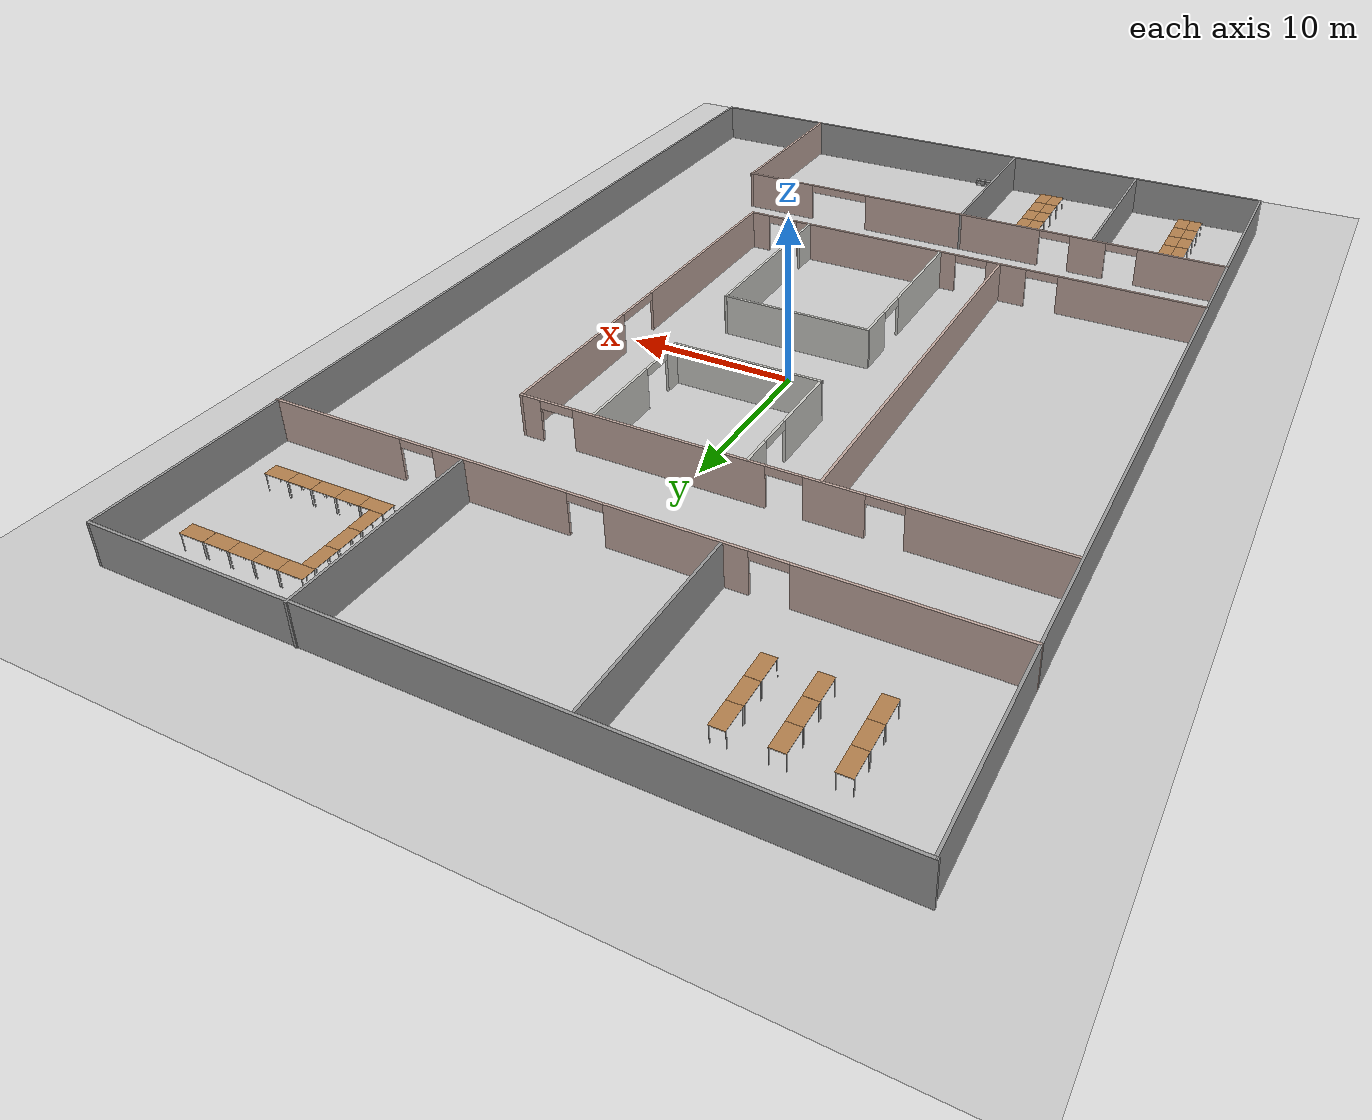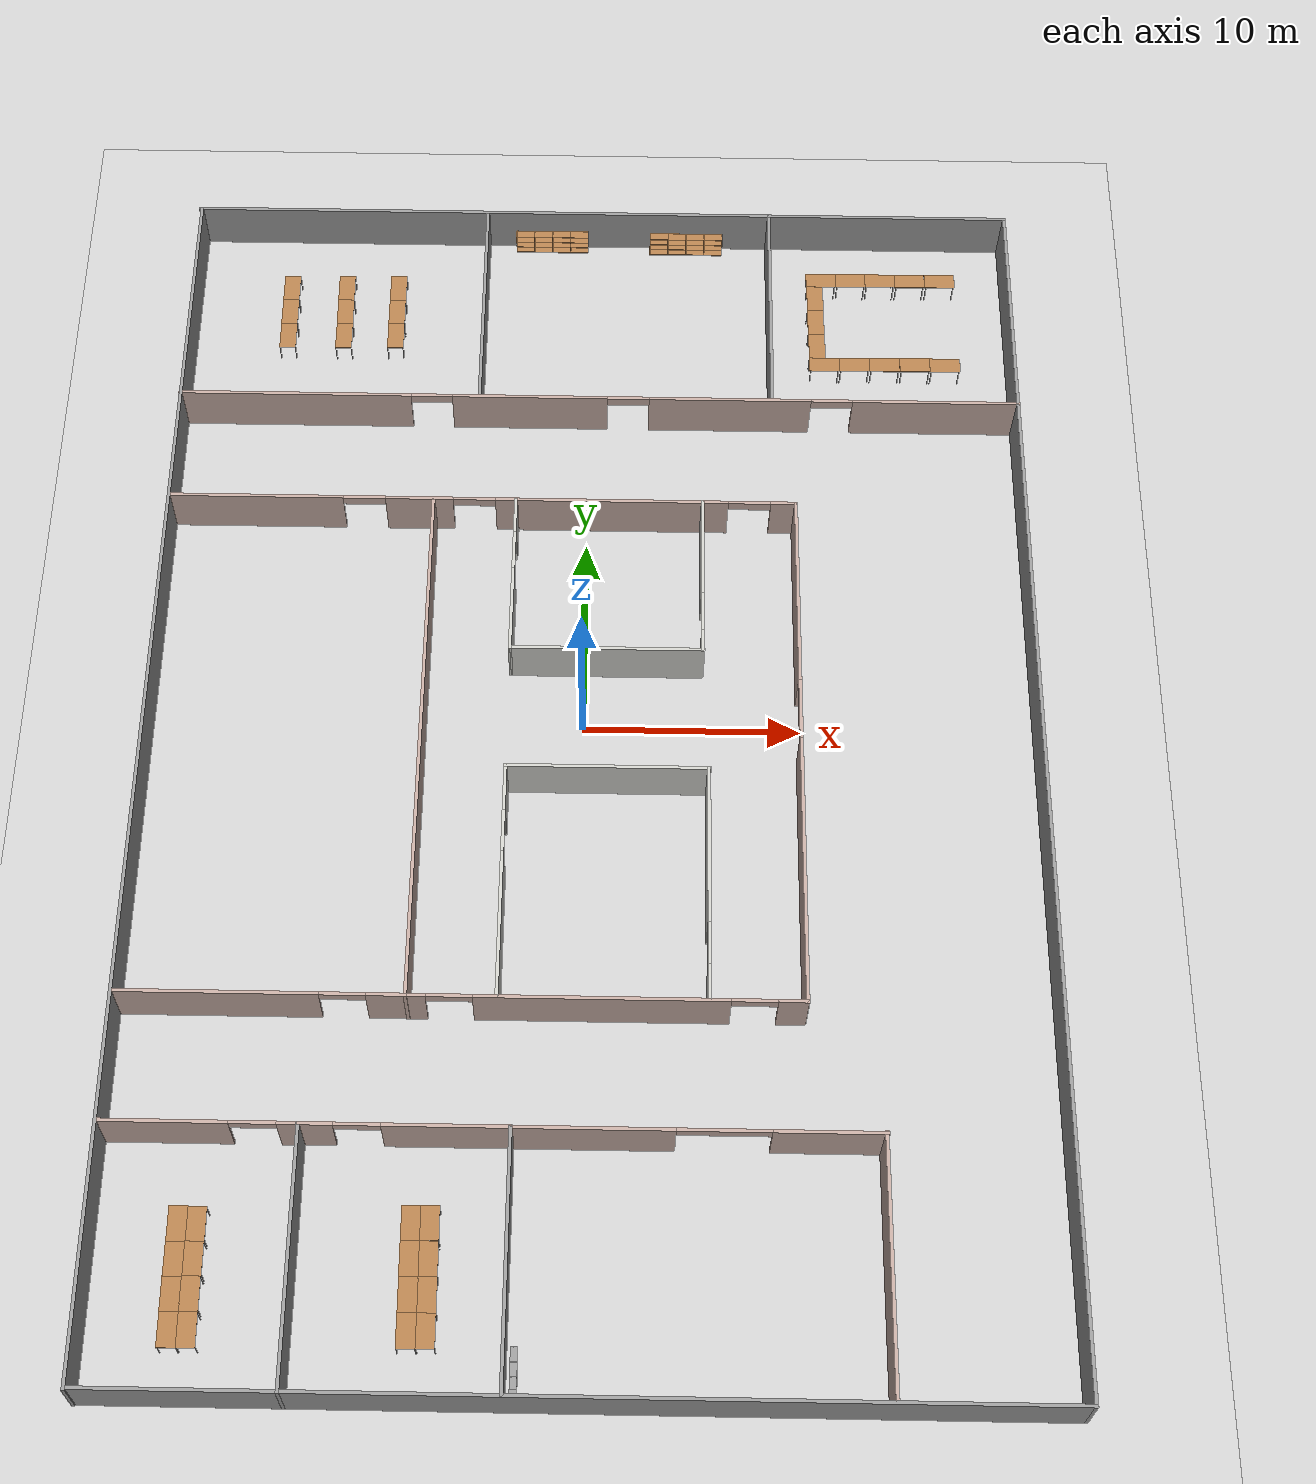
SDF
<sdf version="1.7">
 <world name="default">
  <light name="sun" type="directional">
   <pose>0 0 10 0 -0 0</pose>
   <diffuse>0.8 0.8 0.8 1</diffuse>
   <specular>0.2 0.2 0.2 1</specular>
   <attenuation>
    <range>1000</range>
    <constant>0.9</constant>
    <linear>0.01</linear>
    <quadratic>0.001</quadratic>
   </attenuation>
   <direction>-0.5 0.1 -0.9</direction>
   <spot><inner_angle>0</inner_angle><outer_angle>0</outer_angle><falloff>0</falloff></spot>
  </light>
  <gravity>0 0 -9.8</gravity>
  <magnetic_field>6e-06 2.3e-05 -4.2e-05</magnetic_field>
  <atmosphere type="adiabatic"/>
  <include><uri>model://ground_plane</uri></include>
  <physics type="ode">
   <max_step_size>0.001</max_step_size>
   <real_time_factor>1</real_time_factor>
   <real_time_update_rate>1000</real_time_update_rate>
  </physics>
  <scene><ambient>0.4 0.4 0.4 1</ambient><background>0.7 0.7 0.7 1</background><shadows>1</shadows></scene>
  <audio><device>default</device></audio>
  <spherical_coordinates>
   <surface_model>EARTH_WGS84</surface_model>
   <latitude_deg>0</latitude_deg>
   <longitude_deg>0</longitude_deg>
   <elevation>0</elevation>
   <heading_deg>0</heading_deg>
  </spherical_coordinates>
  <model name="tongfang1">
   <pose>0.460781 -1.38805 0 0 -0 0</pose>
   <link name="Wall_11">
    <collision name="Wall_11_Collision">
     <geometry><box><size>25.5 0.15 2.5</size></box></geometry>
     <pose>0 0 1.25 0 -0 0</pose>
    </collision>
    <visual name="Wall_11_Visual">
     <pose>0 0 1.25 0 -0 0</pose>
     <geometry><box><size>25.5 0.15 2.5</size></box></geometry>
     <material>
      <script><uri>file://media/materials/scripts/gazebo.material</uri><name>Gazebo/Grey</name></script>
      <ambient>0.760784 0.662745 0.627451 1</ambient>
     </material>
     <meta><layer>0</layer></meta>
    </visual>
    <pose>-7.71283 -0.319512 0 0 -0 -1.5708</pose>
   </link>
   <link name="Wall_12">
    <pose>0.841773 -12.9694 0 0 -0 0</pose>
    <visual name="Wall_12_Visual_0">
     <pose>-8.16378 0 1.25 0 -0 0</pose>
     <geometry><box><size>0.931636 0.15 2.5</size></box></geometry>
     <material>
      <script><uri>file://media/materials/scripts/gazebo.material</uri><name>Gazebo/Grey</name></script>
      <ambient>0.760784 0.662745 0.627451 1</ambient>
     </material>
     <meta><layer>0</layer></meta>
    </visual>
    <collision name="Wall_12_Collision_0">
     <geometry><box><size>0.931636 0.15 2.5</size></box></geometry>
     <pose>-8.16378 0 1.25 0 -0 0</pose>
    </collision>
    <visual name="Wall_12_Visual_1">
     <pose>-0.184896 0 1.25 0 -0 0</pose>
     <geometry><box><size>11.0261 0.15 2.5</size></box></geometry>
     <material>
      <script><uri>file://media/materials/scripts/gazebo.material</uri><name>Gazebo/Grey</name></script>
      <ambient>0.760784 0.662745 0.627451 1</ambient>
     </material>
     <meta><layer>0</layer></meta>
    </visual>
    <collision name="Wall_12_Collision_1">
     <geometry><box><size>11.0261 0.15 2.5</size></box></geometry>
     <pose>-0.184896 0 1.25 0 -0 0</pose>
    </collision>
    <visual name="Wall_12_Visual_2">
     <pose>7.97889 0 1.25 0 -0 0</pose>
     <geometry><box><size>1.30143 0.15 2.5</size></box></geometry>
     <material>
      <script><uri>file://media/materials/scripts/gazebo.material</uri><name>Gazebo/Grey</name></script>
      <ambient>0.760784 0.662745 0.627451 1</ambient>
     </material>
     <meta><layer>0</layer></meta>
    </visual>
    <collision name="Wall_12_Collision_2">
     <geometry><box><size>1.30143 0.15 2.5</size></box></geometry>
     <pose>7.97889 0 1.25 0 -0 0</pose>
    </collision>
    <visual name="Wall_12_Visual_3">
     <pose>-6.69797 0 2.25 0 -0 0</pose>
     <geometry><box><size>2 0.15 0.5</size></box></geometry>
     <material>
      <script><uri>file://media/materials/scripts/gazebo.material</uri><name>Gazebo/Grey</name></script>
      <ambient>0.760784 0.662745 0.627451 1</ambient>
     </material>
     <meta><layer>0</layer></meta>
    </visual>
    <collision name="Wall_12_Collision_3">
     <geometry><box><size>2 0.15 0.5</size></box></geometry>
     <pose>-6.69797 0 2.25 0 -0 0</pose>
    </collision>
    <visual name="Wall_12_Visual_4">
     <pose>6.32817 0 2.25 0 -0 0</pose>
     <geometry><box><size>2 0.15 0.5</size></box></geometry>
     <material>
      <script><uri>file://media/materials/scripts/gazebo.material</uri><name>Gazebo/Grey</name></script>
      <ambient>0.760784 0.662745 0.627451 1</ambient>
     </material>
     <meta><layer>0</layer></meta>
    </visual>
    <collision name="Wall_12_Collision_4">
     <geometry><box><size>2 0.15 0.5</size></box></geometry>
     <pose>6.32817 0 2.25 0 -0 0</pose>
    </collision>
   </link>
   <link name="Wall_16">
    <pose>-3.82458 -7.35827 0 0 -0 -1.5708</pose>
    <visual name="Wall_16_Visual_0">
     <pose>-4.45921 0 1.25 0 -0 0</pose>
     <geometry><box><size>2.33157 0.15 2.5</size></box></geometry>
     <material>
      <script><uri>file://media/materials/scripts/gazebo.material</uri><name>Gazebo/CeilingTiled</name></script>
      <ambient>1 1 1 1</ambient>
     </material>
     <meta><layer>0</layer></meta>
    </visual>
    <collision name="Wall_16_Collision_0">
     <geometry><box><size>2.33157 0.15 2.5</size></box></geometry>
     <pose>-4.45921 0 1.25 0 -0 0</pose>
    </collision>
    <visual name="Wall_16_Visual_1">
     <pose>2.16579 0 1.25 0 -0 0</pose>
     <geometry><box><size>6.91843 0.15 2.5</size></box></geometry>
     <material>
      <script><uri>file://media/materials/scripts/gazebo.material</uri><name>Gazebo/CeilingTiled</name></script>
      <ambient>1 1 1 1</ambient>
     </material>
     <meta><layer>0</layer></meta>
    </visual>
    <collision name="Wall_16_Collision_1">
     <geometry><box><size>6.91843 0.15 2.5</size></box></geometry>
     <pose>2.16579 0 1.25 0 -0 0</pose>
    </collision>
    <visual name="Wall_16_Visual_2">
     <pose>-2.29343 0 2.25 0 -0 0</pose>
     <geometry><box><size>2 0.15 0.5</size></box></geometry>
     <material>
      <script><uri>file://media/materials/scripts/gazebo.material</uri><name>Gazebo/CeilingTiled</name></script>
      <ambient>1 1 1 1</ambient>
     </material>
     <meta><layer>0</layer></meta>
    </visual>
    <collision name="Wall_16_Collision_2">
     <geometry><box><size>2 0.15 0.5</size></box></geometry>
     <pose>-2.29343 0 2.25 0 -0 0</pose>
    </collision>
   </link>
   <link name="Wall_19">
    <pose>5.2537 -7.34878 0 0 -0 -1.5708</pose>
    <visual name="Wall_19_Visual_0">
     <pose>-1.83702 0 1.25 0 -0 0</pose>
     <geometry><box><size>7.57595 0.15 2.5</size></box></geometry>
     <material>
      <script><uri>file://media/materials/scripts/gazebo.material</uri><name>Gazebo/CeilingTiled</name></script>
      <ambient>1 1 1 1</ambient>
     </material>
     <meta><layer>0</layer></meta>
    </visual>
    <collision name="Wall_19_Collision_0">
     <geometry><box><size>7.57595 0.15 2.5</size></box></geometry>
     <pose>-1.83702 0 1.25 0 -0 0</pose>
    </collision>
    <visual name="Wall_19_Visual_1">
     <pose>4.78798 0 1.25 0 -0 0</pose>
     <geometry><box><size>1.67405 0.15 2.5</size></box></geometry>
     <material>
      <script><uri>file://media/materials/scripts/gazebo.material</uri><name>Gazebo/CeilingTiled</name></script>
      <ambient>1 1 1 1</ambient>
     </material>
     <meta><layer>0</layer></meta>
    </visual>
    <collision name="Wall_19_Collision_1">
     <geometry><box><size>1.67405 0.15 2.5</size></box></geometry>
     <pose>4.78798 0 1.25 0 -0 0</pose>
    </collision>
    <visual name="Wall_19_Visual_2">
     <pose>2.95095 0 2.25 0 -0 0</pose>
     <geometry><box><size>2 0.15 0.5</size></box></geometry>
     <material>
      <script><uri>file://media/materials/scripts/gazebo.material</uri><name>Gazebo/CeilingTiled</name></script>
      <ambient>1 1 1 1</ambient>
     </material>
     <meta><layer>0</layer></meta>
    </visual>
    <collision name="Wall_19_Collision_2">
     <geometry><box><size>2 0.15 0.5</size></box></geometry>
     <pose>2.95095 0 2.25 0 -0 0</pose>
    </collision>
   </link>
   <link name="Wall_21">
    <pose>-3.82128 8.36959 0 0 -0 -1.57421</pose>
    <visual name="Wall_21_Visual_0">
     <pose>-3.18561 0 1.25 0 -0 0</pose>
     <geometry><box><size>1.86593 0.15 2.5</size></box></geometry>
     <material>
      <script><uri>file://media/materials/scripts/gazebo.material</uri><name>Gazebo/CeilingTiled</name></script>
      <ambient>1 1 1 1</ambient>
     </material>
     <meta><layer>0</layer></meta>
    </visual>
    <collision name="Wall_21_Collision_0">
     <geometry><box><size>1.86593 0.15 2.5</size></box></geometry>
     <pose>-3.18561 0 1.25 0 -0 0</pose>
    </collision>
    <visual name="Wall_21_Visual_1">
     <pose>1.93297 0 1.25 0 -0 0</pose>
     <geometry><box><size>4.37123 0.15 2.5</size></box></geometry>
     <material>
      <script><uri>file://media/materials/scripts/gazebo.material</uri><name>Gazebo/CeilingTiled</name></script>
      <ambient>1 1 1 1</ambient>
     </material>
     <meta><layer>0</layer></meta>
    </visual>
    <collision name="Wall_21_Collision_1">
     <geometry><box><size>4.37123 0.15 2.5</size></box></geometry>
     <pose>1.93297 0 1.25 0 -0 0</pose>
    </collision>
    <visual name="Wall_21_Visual_2">
     <pose>-1.25265 0 2.25 0 -0 0</pose>
     <geometry><box><size>2 0.15 0.5</size></box></geometry>
     <material>
      <script><uri>file://media/materials/scripts/gazebo.material</uri><name>Gazebo/CeilingTiled</name></script>
      <ambient>1 1 1 1</ambient>
     </material>
     <meta><layer>0</layer></meta>
    </visual>
    <collision name="Wall_21_Collision_2">
     <geometry><box><size>2 0.15 0.5</size></box></geometry>
     <pose>-1.25265 0 2.25 0 -0 0</pose>
    </collision>
   </link>
   <link name="Wall_23">
    <pose>5.01283 8.37814 0 0 -0 1.5708</pose>
    <visual name="Wall_23_Visual_0">
     <pose>-3.55494 0 1.25 0 -0 0</pose>
     <geometry><box><size>1.14011 0.15 2.5</size></box></geometry>
     <material>
      <script><uri>file://media/materials/scripts/gazebo.material</uri><name>Gazebo/CeilingTiled</name></script>
      <ambient>1 1 1 1</ambient>
     </material>
     <meta><layer>0</layer></meta>
    </visual>
    <collision name="Wall_23_Collision_0">
     <geometry><box><size>1.14011 0.15 2.5</size></box></geometry>
     <pose>-3.55494 0 1.25 0 -0 0</pose>
    </collision>
    <visual name="Wall_23_Visual_1">
     <pose>1.57006 0 1.25 0 -0 0</pose>
     <geometry><box><size>5.10989 0.15 2.5</size></box></geometry>
     <material>
      <script><uri>file://media/materials/scripts/gazebo.material</uri><name>Gazebo/CeilingTiled</name></script>
      <ambient>1 1 1 1</ambient>
     </material>
     <meta><layer>0</layer></meta>
    </visual>
    <collision name="Wall_23_Collision_1">
     <geometry><box><size>5.10989 0.15 2.5</size></box></geometry>
     <pose>1.57006 0 1.25 0 -0 0</pose>
    </collision>
    <visual name="Wall_23_Visual_2">
     <pose>-1.98489 0 2.25 0 -0 0</pose>
     <geometry><box><size>2 0.15 0.5</size></box></geometry>
     <material>
      <script><uri>file://media/materials/scripts/gazebo.material</uri><name>Gazebo/CeilingTiled</name></script>
      <ambient>1 1 1 1</ambient>
     </material>
     <meta><layer>0</layer></meta>
    </visual>
    <collision name="Wall_23_Collision_2">
     <geometry><box><size>2 0.15 0.5</size></box></geometry>
     <pose>-1.98489 0 2.25 0 -0 0</pose>
    </collision>
   </link>
   <link name="Wall_25">
    <pose>-13.9496 -12.9694 0 0 -0 3.14159</pose>
    <visual name="Wall_25_Visual_0">
     <pose>-5.42807 0 1.25 0 -0 0</pose>
     <geometry><box><size>1.76748 0.15 2.5</size></box></geometry>
     <material>
      <script><uri>file://media/materials/scripts/gazebo.material</uri><name>Gazebo/Grey</name></script>
      <ambient>0.760784 0.662745 0.627451 1</ambient>
     </material>
     <meta><layer>0</layer></meta>
    </visual>
    <collision name="Wall_25_Collision_0">
     <geometry><box><size>1.76748 0.15 2.5</size></box></geometry>
     <pose>-5.42807 0 1.25 0 -0 0</pose>
    </collision>
    <visual name="Wall_25_Visual_1">
     <pose>1.88374 0 1.25 0 -0 0</pose>
     <geometry><box><size>8.85615 0.15 2.5</size></box></geometry>
     <material>
      <script><uri>file://media/materials/scripts/gazebo.material</uri><name>Gazebo/Grey</name></script>
      <ambient>0.760784 0.662745 0.627451 1</ambient>
     </material>
     <meta><layer>0</layer></meta>
    </visual>
    <collision name="Wall_25_Collision_1">
     <geometry><box><size>8.85615 0.15 2.5</size></box></geometry>
     <pose>1.88374 0 1.25 0 -0 0</pose>
    </collision>
    <visual name="Wall_25_Visual_2">
     <pose>-3.54433 0 2.25 0 -0 0</pose>
     <geometry><box><size>2 0.15 0.5</size></box></geometry>
     <material>
      <script><uri>file://media/materials/scripts/gazebo.material</uri><name>Gazebo/Grey</name></script>
      <ambient>0.760784 0.662745 0.627451 1</ambient>
     </material>
     <meta><layer>0</layer></meta>
    </visual>
    <collision name="Wall_25_Collision_2">
     <geometry><box><size>2 0.15 0.5</size></box></geometry>
     <pose>-3.54433 0 2.25 0 -0 0</pose>
    </collision>
   </link>
   <link name="Wall_27">
    <pose>-3.83512 -18.7917 0 0 -0 0</pose>
    <visual name="Wall_27_Visual_0">
     <pose>-13.7052 0 1.25 0 -0 0</pose>
     <geometry><box><size>5.58965 0.15 2.5</size></box></geometry>
     <material>
      <script><uri>file://media/materials/scripts/gazebo.material</uri><name>Gazebo/Grey</name></script>
      <ambient>0.760784 0.662745 0.627451 1</ambient>
     </material>
     <meta><layer>0</layer></meta>
    </visual>
    <collision name="Wall_27_Collision_0">
     <geometry><box><size>5.58965 0.15 2.5</size></box></geometry>
     <pose>-13.7052 0 1.25 0 -0 0</pose>
    </collision>
    <visual name="Wall_27_Visual_1">
     <pose>-7.74518 0 1.25 0 -0 0</pose>
     <geometry><box><size>2.33035 0.15 2.5</size></box></geometry>
     <material>
      <script><uri>file://media/materials/scripts/gazebo.material</uri><name>Gazebo/Grey</name></script>
      <ambient>0.760784 0.662745 0.627451 1</ambient>
     </material>
     <meta><layer>0</layer></meta>
    </visual>
    <collision name="Wall_27_Collision_1">
     <geometry><box><size>2.33035 0.15 2.5</size></box></geometry>
     <pose>-7.74518 0 1.25 0 -0 0</pose>
    </collision>
    <visual name="Wall_27_Visual_2">
     <pose>1.54079 0 1.25 0 -0 0</pose>
     <geometry><box><size>12.2416 0.15 2.5</size></box></geometry>
     <material>
      <script><uri>file://media/materials/scripts/gazebo.material</uri><name>Gazebo/Grey</name></script>
      <ambient>0.760784 0.662745 0.627451 1</ambient>
     </material>
     <meta><layer>0</layer></meta>
    </visual>
    <collision name="Wall_27_Collision_2">
     <geometry><box><size>12.2416 0.15 2.5</size></box></geometry>
     <pose>1.54079 0 1.25 0 -0 0</pose>
    </collision>
    <visual name="Wall_27_Visual_3">
     <pose>14.0808 0 1.25 0 -0 0</pose>
     <geometry><box><size>4.83841 0.15 2.5</size></box></geometry>
     <material>
      <script><uri>file://media/materials/scripts/gazebo.material</uri><name>Gazebo/Grey</name></script>
      <ambient>0.760784 0.662745 0.627451 1</ambient>
     </material>
     <meta><layer>0</layer></meta>
    </visual>
    <collision name="Wall_27_Collision_3">
     <geometry><box><size>4.83841 0.15 2.5</size></box></geometry>
     <pose>14.0808 0 1.25 0 -0 0</pose>
    </collision>
    <visual name="Wall_27_Visual_4">
     <pose>-9.91035 0 2.25 0 -0 0</pose>
     <geometry><box><size>2 0.15 0.5</size></box></geometry>
     <material>
      <script><uri>file://media/materials/scripts/gazebo.material</uri><name>Gazebo/Grey</name></script>
      <ambient>0.760784 0.662745 0.627451 1</ambient>
     </material>
     <meta><layer>0</layer></meta>
    </visual>
    <collision name="Wall_27_Collision_4">
     <geometry><box><size>2 0.15 0.5</size></box></geometry>
     <pose>-9.91035 0 2.25 0 -0 0</pose>
    </collision>
    <visual name="Wall_27_Visual_5">
     <pose>-5.58001 0 2.25 0 -0 0</pose>
     <geometry><box><size>2 0.15 0.5</size></box></geometry>
     <material>
      <script><uri>file://media/materials/scripts/gazebo.material</uri><name>Gazebo/Grey</name></script>
      <ambient>0.760784 0.662745 0.627451 1</ambient>
     </material>
     <meta><layer>0</layer></meta>
    </visual>
    <collision name="Wall_27_Collision_5">
     <geometry><box><size>2 0.15 0.5</size></box></geometry>
     <pose>-5.58001 0 2.25 0 -0 0</pose>
    </collision>
    <visual name="Wall_27_Visual_6">
     <pose>9.66159 0 2.25 0 -0 0</pose>
     <geometry><box><size>4 0.15 0.5</size></box></geometry>
     <material>
      <script><uri>file://media/materials/scripts/gazebo.material</uri><name>Gazebo/Grey</name></script>
      <ambient>0.760784 0.662745 0.627451 1</ambient>
     </material>
     <meta><layer>0</layer></meta>
    </visual>
    <collision name="Wall_27_Collision_6">
     <geometry><box><size>4 0.15 0.5</size></box></geometry>
     <pose>9.66159 0 2.25 0 -0 0</pose>
    </collision>
   </link>
   <link name="Wall_28">
    <collision name="Wall_28_Collision">
     <geometry><box><size>11.2742 0.15 2.5</size></box></geometry>
     <pose>0 0 1.25 0 -0 0</pose>
    </collision>
    <visual name="Wall_28_Visual">
     <pose>0 0 1.25 0 -0 0</pose>
     <geometry><box><size>11.2742 0.15 2.5</size></box></geometry>
     <material>
      <script><uri>file://media/materials/scripts/gazebo.material</uri><name>Gazebo/Grey</name></script>
      <ambient>0.760784 0.662745 0.627451 1</ambient>
     </material>
     <meta><layer>0</layer></meta>
    </visual>
    <pose>12.5508 -24.3149 0 0 -0 -1.57084</pose>
   </link>
   <link name="Wall_30">
    <collision name="Wall_30_Collision">
     <geometry><box><size>11.25 0.15 2.5</size></box></geometry>
     <pose>0 0 1.25 0 -0 0</pose>
    </collision>
    <visual name="Wall_30_Visual">
     <pose>0 0 1.25 0 -0 0</pose>
     <geometry><box><size>11.25 0.15 2.5</size></box></geometry>
     <material>
      <script><uri>file://media/materials/scripts/gazebo.material</uri><name>Gazebo/Grey</name></script>
      <ambient>1 1 1 1</ambient>
     </material>
     <meta><layer>0</layer></meta>
    </visual>
    <pose>-11.8436 -24.3561 0 0 -0 -1.5708</pose>
   </link>
   <link name="Wall_33">
    <collision name="Wall_33_Collision">
     <geometry><box><size>11.25 0.15 2.5</size></box></geometry>
     <pose>0 0 1.25 0 -0 0</pose>
    </collision>
    <visual name="Wall_33_Visual">
     <pose>0 0 1.25 0 -0 0</pose>
     <geometry><box><size>11.25 0.15 2.5</size></box></geometry>
     <material>
      <script><uri>file://media/materials/scripts/gazebo.material</uri><name>Gazebo/Grey</name></script>
      <ambient>1 1 1 1</ambient>
     </material>
     <meta><layer>0</layer></meta>
    </visual>
    <pose>-3.02976 -24.3326 0 0 -0 -1.5708</pose>
   </link>
   <link name="Wall_41">
    <pose>0.019443 18.4356 0 0 -0 0</pose>
    <visual name="Wall_41_Visual_0">
     <pose>-14.7444 0 1.25 0 -0 0</pose>
     <geometry><box><size>11.2613 0.15 2.5</size></box></geometry>
     <material>
      <script><uri>file://media/materials/scripts/gazebo.material</uri><name>Gazebo/Grey</name></script>
      <ambient>0.760784 0.662745 0.627451 1</ambient>
     </material>
     <meta><layer>0</layer></meta>
    </visual>
    <collision name="Wall_41_Collision_0">
     <geometry><box><size>11.2613 0.15 2.5</size></box></geometry>
     <pose>-14.7444 0 1.25 0 -0 0</pose>
    </collision>
    <visual name="Wall_41_Visual_1">
     <pose>-3.34877 0 1.25 0 -0 0</pose>
     <geometry><box><size>7.52993 0.15 2.5</size></box></geometry>
     <material>
      <script><uri>file://media/materials/scripts/gazebo.material</uri><name>Gazebo/Grey</name></script>
      <ambient>0.760784 0.662745 0.627451 1</ambient>
     </material>
     <meta><layer>0</layer></meta>
    </visual>
    <collision name="Wall_41_Collision_1">
     <geometry><box><size>7.52993 0.15 2.5</size></box></geometry>
     <pose>-3.34877 0 1.25 0 -0 0</pose>
    </collision>
    <visual name="Wall_41_Visual_2">
     <pose>6.33761 0 1.25 0 -0 0</pose>
     <geometry><box><size>7.84283 0.15 2.5</size></box></geometry>
     <material>
      <script><uri>file://media/materials/scripts/gazebo.material</uri><name>Gazebo/Grey</name></script>
      <ambient>0.760784 0.662745 0.627451 1</ambient>
     </material>
     <meta><layer>0</layer></meta>
    </visual>
    <collision name="Wall_41_Collision_2">
     <geometry><box><size>7.84283 0.15 2.5</size></box></geometry>
     <pose>6.33761 0 1.25 0 -0 0</pose>
    </collision>
    <visual name="Wall_41_Visual_3">
     <pose>16.317 0 1.25 0 -0 0</pose>
     <geometry><box><size>8.11597 0.15 2.5</size></box></geometry>
     <material>
      <script><uri>file://media/materials/scripts/gazebo.material</uri><name>Gazebo/Grey</name></script>
      <ambient>0.760784 0.662745 0.627451 1</ambient>
     </material>
     <meta><layer>0</layer></meta>
    </visual>
    <collision name="Wall_41_Collision_3">
     <geometry><box><size>8.11597 0.15 2.5</size></box></geometry>
     <pose>16.317 0 1.25 0 -0 0</pose>
    </collision>
    <visual name="Wall_41_Visual_4">
     <pose>-8.11373 0 2.25 0 -0 0</pose>
     <geometry><box><size>2 0.15 0.5</size></box></geometry>
     <material>
      <script><uri>file://media/materials/scripts/gazebo.material</uri><name>Gazebo/Grey</name></script>
      <ambient>0.760784 0.662745 0.627451 1</ambient>
     </material>
     <meta><layer>0</layer></meta>
    </visual>
    <collision name="Wall_41_Collision_4">
     <geometry><box><size>2 0.15 0.5</size></box></geometry>
     <pose>-8.11373 0 2.25 0 -0 0</pose>
    </collision>
    <visual name="Wall_41_Visual_5">
     <pose>1.4162 0 2.25 0 -0 0</pose>
     <geometry><box><size>2 0.15 0.5</size></box></geometry>
     <material>
      <script><uri>file://media/materials/scripts/gazebo.material</uri><name>Gazebo/Grey</name></script>
      <ambient>0.760784 0.662745 0.627451 1</ambient>
     </material>
     <meta><layer>0</layer></meta>
    </visual>
    <collision name="Wall_41_Collision_5">
     <geometry><box><size>2 0.15 0.5</size></box></geometry>
     <pose>1.4162 0 2.25 0 -0 0</pose>
    </collision>
    <visual name="Wall_41_Visual_6">
     <pose>11.259 0 2.25 0 -0 0</pose>
     <geometry><box><size>2 0.15 0.5</size></box></geometry>
     <material>
      <script><uri>file://media/materials/scripts/gazebo.material</uri><name>Gazebo/Grey</name></script>
      <ambient>0.760784 0.662745 0.627451 1</ambient>
     </material>
     <meta><layer>0</layer></meta>
    </visual>
    <collision name="Wall_41_Collision_6">
     <geometry><box><size>2 0.15 0.5</size></box></geometry>
     <pose>11.259 0 2.25 0 -0 0</pose>
    </collision>
   </link>
   <link name="Wall_43">
    <collision name="Wall_43_Collision">
     <geometry><box><size>11.5 0.15 2.5</size></box></geometry>
     <pose>0 0 1.25 0 -0 0</pose>
    </collision>
    <visual name="Wall_43_Visual">
     <pose>0 0 1.25 0 -0 0</pose>
     <geometry><box><size>11.5 0.15 2.5</size></box></geometry>
     <material>
      <script><uri>file://media/materials/scripts/gazebo.material</uri><name>Gazebo/Grey</name></script>
      <ambient>1 1 1 1</ambient>
     </material>
     <meta><layer>0</layer></meta>
    </visual>
    <pose>-5.78027 24.1374 0 0 -0 -1.5708</pose>
   </link>
   <link name="Wall_45">
    <collision name="Wall_45_Collision">
     <geometry><box><size>11.5 0.15 2.5</size></box></geometry>
     <pose>0 0 1.25 0 -0 0</pose>
    </collision>
    <visual name="Wall_45_Visual">
     <pose>0 0 1.25 0 -0 0</pose>
     <geometry><box><size>11.5 0.15 2.5</size></box></geometry>
     <material>
      <script><uri>file://media/materials/scripts/gazebo.material</uri><name>Gazebo/Grey</name></script>
      <ambient>1 1 1 1</ambient>
     </material>
     <meta><layer>0</layer></meta>
    </visual>
    <pose>8.39938 24.2809 0 0 -0 -1.5708</pose>
   </link>
   <link name="Wall_51">
    <pose>9.41727 -0.263178 0 0 -0 1.5708</pose>
    <visual name="Wall_51_Visual_0">
     <pose>-6.34019 0 1.25 0 -0 0</pose>
     <geometry><box><size>12.882 0.15 2.5</size></box></geometry>
     <material>
      <script><uri>file://media/materials/scripts/gazebo.material</uri><name>Gazebo/Grey</name></script>
      <ambient>0.760784 0.662745 0.627451 1</ambient>
     </material>
     <meta><layer>0</layer></meta>
    </visual>
    <collision name="Wall_51_Collision_0">
     <geometry><box><size>12.882 0.15 2.5</size></box></geometry>
     <pose>-6.34019 0 1.25 0 -0 0</pose>
    </collision>
    <visual name="Wall_51_Visual_1">
     <pose>7.941 0 1.25 0 -0 0</pose>
     <geometry><box><size>9.68039 0.15 2.5</size></box></geometry>
     <material>
      <script><uri>file://media/materials/scripts/gazebo.material</uri><name>Gazebo/Grey</name></script>
      <ambient>0.760784 0.662745 0.627451 1</ambient>
     </material>
     <meta><layer>0</layer></meta>
    </visual>
    <collision name="Wall_51_Collision_1">
     <geometry><box><size>9.68039 0.15 2.5</size></box></geometry>
     <pose>7.941 0 1.25 0 -0 0</pose>
    </collision>
    <visual name="Wall_51_Visual_2">
     <pose>1.60081 0 2.25 0 -0 0</pose>
     <geometry><box><size>3 0.15 0.5</size></box></geometry>
     <material>
      <script><uri>file://media/materials/scripts/gazebo.material</uri><name>Gazebo/Grey</name></script>
      <ambient>0.760784 0.662745 0.627451 1</ambient>
     </material>
     <meta><layer>0</layer></meta>
    </visual>
    <collision name="Wall_51_Collision_2">
     <geometry><box><size>3 0.15 0.5</size></box></geometry>
     <pose>1.60081 0 2.25 0 -0 0</pose>
    </collision>
   </link>
   <link name="Wall_52">
    <pose>-5.37609 12.443 0 0 -0 3.14159</pose>
    <visual name="Wall_52_Visual_0">
     <pose>-14.2244 0 1.25 0 -0 0</pose>
     <geometry><box><size>1.24614 0.15 2.5</size></box></geometry>
     <material>
      <script><uri>file://media/materials/scripts/gazebo.material</uri><name>Gazebo/Grey</name></script>
      <ambient>0.760784 0.662745 0.627451 1</ambient>
     </material>
     <meta><layer>0</layer></meta>
    </visual>
    <collision name="Wall_52_Collision_0">
     <geometry><box><size>1.24614 0.15 2.5</size></box></geometry>
     <pose>-14.2244 0 1.25 0 -0 0</pose>
    </collision>
    <visual name="Wall_52_Visual_1">
     <pose>-6.09392 0 1.25 0 -0 0</pose>
     <geometry><box><size>11.0148 0.15 2.5</size></box></geometry>
     <material>
      <script><uri>file://media/materials/scripts/gazebo.material</uri><name>Gazebo/Grey</name></script>
      <ambient>0.760784 0.662745 0.627451 1</ambient>
     </material>
     <meta><layer>0</layer></meta>
    </visual>
    <collision name="Wall_52_Collision_1">
     <geometry><box><size>11.0148 0.15 2.5</size></box></geometry>
     <pose>-6.09392 0 1.25 0 -0 0</pose>
    </collision>
    <visual name="Wall_52_Visual_2">
     <pose>3.01793 0 1.25 0 -0 0</pose>
     <geometry><box><size>3.2089 0.15 2.5</size></box></geometry>
     <material>
      <script><uri>file://media/materials/scripts/gazebo.material</uri><name>Gazebo/Grey</name></script>
      <ambient>0.760784 0.662745 0.627451 1</ambient>
     </material>
     <meta><layer>0</layer></meta>
    </visual>
    <collision name="Wall_52_Collision_2">
     <geometry><box><size>3.2089 0.15 2.5</size></box></geometry>
     <pose>3.01793 0 1.25 0 -0 0</pose>
    </collision>
    <visual name="Wall_52_Visual_3">
     <pose>10.7349 0 1.25 0 -0 0</pose>
     <geometry><box><size>8.22509 0.15 2.5</size></box></geometry>
     <material>
      <script><uri>file://media/materials/scripts/gazebo.material</uri><name>Gazebo/Grey</name></script>
      <ambient>0.760784 0.662745 0.627451 1</ambient>
     </material>
     <meta><layer>0</layer></meta>
    </visual>
    <collision name="Wall_52_Collision_3">
     <geometry><box><size>8.22509 0.15 2.5</size></box></geometry>
     <pose>10.7349 0 1.25 0 -0 0</pose>
    </collision>
    <visual name="Wall_52_Visual_4">
     <pose>-12.6013 0 2.25 0 -0 0</pose>
     <geometry><box><size>2 0.15 0.5</size></box></geometry>
     <material>
      <script><uri>file://media/materials/scripts/gazebo.material</uri><name>Gazebo/Grey</name></script>
      <ambient>0.760784 0.662745 0.627451 1</ambient>
     </material>
     <meta><layer>0</layer></meta>
    </visual>
    <collision name="Wall_52_Collision_4">
     <geometry><box><size>2 0.15 0.5</size></box></geometry>
     <pose>-12.6013 0 2.25 0 -0 0</pose>
    </collision>
    <visual name="Wall_52_Visual_5">
     <pose>0.413486 0 2.25 0 -0 0</pose>
     <geometry><box><size>2 0.15 0.5</size></box></geometry>
     <material>
      <script><uri>file://media/materials/scripts/gazebo.material</uri><name>Gazebo/Grey</name></script>
      <ambient>0.760784 0.662745 0.627451 1</ambient>
     </material>
     <meta><layer>0</layer></meta>
    </visual>
    <collision name="Wall_52_Collision_5">
     <geometry><box><size>2 0.15 0.5</size></box></geometry>
     <pose>0.413486 0 2.25 0 -0 0</pose>
    </collision>
    <visual name="Wall_52_Visual_6">
     <pose>5.62238 0 2.25 0 -0 0</pose>
     <geometry><box><size>2 0.15 0.5</size></box></geometry>
     <material>
      <script><uri>file://media/materials/scripts/gazebo.material</uri><name>Gazebo/Grey</name></script>
      <ambient>0.760784 0.662745 0.627451 1</ambient>
     </material>
     <meta><layer>0</layer></meta>
    </visual>
    <collision name="Wall_52_Collision_6">
     <geometry><box><size>2 0.15 0.5</size></box></geometry>
     <pose>5.62238 0 2.25 0 -0 0</pose>
    </collision>
   </link>
   <link name="Wall_60">
    <collision name="Wall_60_Collision">
     <geometry><box><size>60 0.15 2.5</size></box></geometry>
     <pose>0 0 1.25 0 -0 0</pose>
    </collision>
    <visual name="Wall_60_Visual">
     <pose>0 0 1.25 0 -0 0</pose>
     <geometry><box><size>60 0.15 2.5</size></box></geometry>
     <material>
      <script><uri>file://media/materials/scripts/gazebo.material</uri><name>Gazebo/Grey</name></script>
      <ambient>0.870588 0.866667 0.854902 1</ambient>
     </material>
     <meta><layer>0</layer></meta>
    </visual>
    <pose>-20.2688 -0.030923 0 0 -0 -1.5708</pose>
   </link>
   <link name="Wall_7">
    <collision name="Wall_7_Collision">
     <geometry><box><size>40.75 0.15 2.5</size></box></geometry>
     <pose>0 0 1.25 0 -0 0</pose>
    </collision>
    <visual name="Wall_7_Visual">
     <pose>0 0 1.25 0 -0 0</pose>
     <geometry><box><size>40.75 0.15 2.5</size></box></geometry>
     <material>
      <script><uri>file://media/materials/scripts/gazebo.material</uri><name>Gazebo/Grey</name></script>
      <ambient>0.870588 0.866667 0.854902 1</ambient>
     </material>
     <meta><layer>0</layer></meta>
    </visual>
    <pose>0.034467 -29.904 0 0 -0 0</pose>
   </link>
   <link name="Wall_8">
    <collision name="Wall_8_Collision">
     <geometry><box><size>59.9484 0.15 2.5</size></box></geometry>
     <pose>0 0 1.25 0 -0 0</pose>
    </collision>
    <visual name="Wall_8_Visual">
     <pose>0 0 1.25 0 -0 0</pose>
     <geometry><box><size>59.9484 0.15 2.5</size></box></geometry>
     <material>
      <script><uri>file://media/materials/scripts/gazebo.material</uri><name>Gazebo/Grey</name></script>
      <ambient>0.870588 0.866667 0.854902 1</ambient>
     </material>
     <meta><layer>0</layer></meta>
    </visual>
    <pose>20.3 -0.004979 0 0 -0 1.57195</pose>
   </link>
   <link name="Wall_88">
    <collision name="Wall_88_Collision">
     <geometry><box><size>9 0.15 2.5</size></box></geometry>
     <pose>0 0 1.25 0 -0 0</pose>
    </collision>
    <visual name="Wall_88_Visual">
     <pose>0 0 1.25 0 -0 0</pose>
     <geometry><box><size>9 0.15 2.5</size></box></geometry>
     <material>
      <script><uri>file://media/materials/scripts/gazebo.material</uri><name>Gazebo/CeilingTiled</name></script>
      <ambient>1 1 1 1</ambient>
     </material>
     <meta><layer>0</layer></meta>
    </visual>
    <pose>0.589911 4.32604 0 0 -0 0</pose>
   </link>
   <link name="Wall_9">
    <collision name="Wall_9_Collision">
     <geometry><box><size>40.75 0.15 2.5</size></box></geometry>
     <pose>0 0 1.25 0 -0 0</pose>
    </collision>
    <visual name="Wall_9_Visual">
     <pose>0 0 1.25 0 -0 0</pose>
     <geometry><box><size>40.75 0.15 2.5</size></box></geometry>
     <material>
      <script><uri>file://media/materials/scripts/gazebo.material</uri><name>Gazebo/Grey</name></script>
      <ambient>0.870588 0.866667 0.854902 1</ambient>
     </material>
     <meta><layer>0</layer></meta>
    </visual>
    <pose>-0.034555 29.8941 0 0 -0 3.14159</pose>
   </link>
   <link name="Wall_90">
    <collision name="Wall_90_Collision">
     <geometry><box><size>9.25 0.15 2.5</size></box></geometry>
     <pose>0 0 1.25 0 -0 0</pose>
    </collision>
    <visual name="Wall_90_Visual">
     <pose>0 0 1.25 0 -0 0</pose>
     <geometry><box><size>9.25 0.15 2.5</size></box></geometry>
     <material>
      <script><uri>file://media/materials/scripts/gazebo.material</uri><name>Gazebo/CeilingTiled</name></script>
      <ambient>1 1 1 1</ambient>
     </material>
     <meta><layer>0</layer></meta>
    </visual>
    <pose>0.725421 -1.80827 0 0 -0 0</pose>
   </link>
   <static>1</static>
  </model>
  <model name="table">
   <static>1</static>
   <link name="link">
    <collision name="surface">
     <pose>0 0 1 0 -0 0</pose>
     <geometry><box><size>1.5 0.8 0.03</size></box></geometry>
     <surface><friction><ode><mu>0.6</mu><mu2>0.6</mu2></ode></friction></surface>
    </collision>
    <visual name="visual1">
     <pose>0 0 1 0 -0 0</pose>
     <geometry><box><size>1.5 0.8 0.03</size></box></geometry>
     <material>
      <script><uri>file://media/materials/scripts/gazebo.material</uri><name>Gazebo/Wood</name></script>
     </material>
    </visual>
    <collision name="front_left_leg">
     <pose>0.68 0.38 0.5 0 -0 0</pose>
     <geometry><cylinder><radius>0.02</radius><length>1</length></cylinder></geometry>
    </collision>
    <visual name="front_left_leg">
     <pose>0.68 0.38 0.5 0 -0 0</pose>
     <geometry><cylinder><radius>0.02</radius><length>1</length></cylinder></geometry>
     <material>
      <script><uri>file://media/materials/scripts/gazebo.material</uri><name>Gazebo/Grey</name></script>
     </material>
    </visual>
    <collision name="front_right_leg">
     <pose>0.68 -0.38 0.5 0 -0 0</pose>
     <geometry><cylinder><radius>0.02</radius><length>1</length></cylinder></geometry>
    </collision>
    <visual name="front_right_leg">
     <pose>0.68 -0.38 0.5 0 -0 0</pose>
     <geometry><cylinder><radius>0.02</radius><length>1</length></cylinder></geometry>
     <material>
      <script><uri>file://media/materials/scripts/gazebo.material</uri><name>Gazebo/Grey</name></script>
     </material>
    </visual>
    <collision name="back_right_leg">
     <pose>-0.68 -0.38 0.5 0 -0 0</pose>
     <geometry><cylinder><radius>0.02</radius><length>1</length></cylinder></geometry>
    </collision>
    <visual name="back_right_leg">
     <pose>-0.68 -0.38 0.5 0 -0 0</pose>
     <geometry><cylinder><radius>0.02</radius><length>1</length></cylinder></geometry>
     <material>
      <script><uri>file://media/materials/scripts/gazebo.material</uri><name>Gazebo/Grey</name></script>
     </material>
    </visual>
    <collision name="back_left_leg">
     <pose>-0.68 0.38 0.5 0 -0 0</pose>
     <geometry><cylinder><radius>0.02</radius><length>1</length></cylinder></geometry>
    </collision>
    <visual name="back_left_leg">
     <pose>-0.68 0.38 0.5 0 -0 0</pose>
     <geometry><cylinder><radius>0.02</radius><length>1</length></cylinder></geometry>
     <material>
      <script><uri>file://media/materials/scripts/gazebo.material</uri><name>Gazebo/Grey</name></script>
     </material>
    </visual>
   </link>
   <pose>-15.4305 -24.0821 0 0 -0 1.58041</pose>
  </model>
  <model name="table_clone">
   <static>1</static>
   <link name="link">
    <collision name="surface">
     <pose>0 0 1 0 -0 0</pose>
     <geometry><box><size>1.5 0.8 0.03</size></box></geometry>
     <surface><friction><ode><mu>0.6</mu><mu2>0.6</mu2></ode></friction></surface>
    </collision>
    <visual name="visual1">
     <pose>0 0 1 0 -0 0</pose>
     <geometry><box><size>1.5 0.8 0.03</size></box></geometry>
     <material>
      <script><uri>file://media/materials/scripts/gazebo.material</uri><name>Gazebo/Wood</name></script>
     </material>
    </visual>
    <collision name="front_left_leg">
     <pose>0.68 0.38 0.5 0 -0 0</pose>
     <geometry><cylinder><radius>0.02</radius><length>1</length></cylinder></geometry>
    </collision>
    <visual name="front_left_leg">
     <pose>0.68 0.38 0.5 0 -0 0</pose>
     <geometry><cylinder><radius>0.02</radius><length>1</length></cylinder></geometry>
     <material>
      <script><uri>file://media/materials/scripts/gazebo.material</uri><name>Gazebo/Grey</name></script>
     </material>
    </visual>
    <collision name="front_right_leg">
     <pose>0.68 -0.38 0.5 0 -0 0</pose>
     <geometry><cylinder><radius>0.02</radius><length>1</length></cylinder></geometry>
    </collision>
    <visual name="front_right_leg">
     <pose>0.68 -0.38 0.5 0 -0 0</pose>
     <geometry><cylinder><radius>0.02</radius><length>1</length></cylinder></geometry>
     <material>
      <script><uri>file://media/materials/scripts/gazebo.material</uri><name>Gazebo/Grey</name></script>
     </material>
    </visual>
    <collision name="back_right_leg">
     <pose>-0.68 -0.38 0.5 0 -0 0</pose>
     <geometry><cylinder><radius>0.02</radius><length>1</length></cylinder></geometry>
    </collision>
    <visual name="back_right_leg">
     <pose>-0.68 -0.38 0.5 0 -0 0</pose>
     <geometry><cylinder><radius>0.02</radius><length>1</length></cylinder></geometry>
     <material>
      <script><uri>file://media/materials/scripts/gazebo.material</uri><name>Gazebo/Grey</name></script>
     </material>
    </visual>
    <collision name="back_left_leg">
     <pose>-0.68 0.38 0.5 0 -0 0</pose>
     <geometry><cylinder><radius>0.02</radius><length>1</length></cylinder></geometry>
    </collision>
    <visual name="back_left_leg">
     <pose>-0.68 0.38 0.5 0 -0 0</pose>
     <geometry><cylinder><radius>0.02</radius><length>1</length></cylinder></geometry>
     <material>
      <script><uri>file://media/materials/scripts/gazebo.material</uri><name>Gazebo/Grey</name></script>
     </material>
    </visual>
   </link>
   <pose>-15.4315 -25.5243 0 0 -0 1.57868</pose>
  </model>
  <model name="table_clone_clone">
   <static>1</static>
   <link name="link">
    <collision name="surface">
     <pose>0 0 1 0 -0 0</pose>
     <geometry><box><size>1.5 0.8 0.03</size></box></geometry>
     <surface><friction><ode><mu>0.6</mu><mu2>0.6</mu2></ode></friction></surface>
    </collision>
    <visual name="visual1">
     <pose>0 0 1 0 -0 0</pose>
     <geometry><box><size>1.5 0.8 0.03</size></box></geometry>
     <material>
      <script><uri>file://media/materials/scripts/gazebo.material</uri><name>Gazebo/Wood</name></script>
     </material>
    </visual>
    <collision name="front_left_leg">
     <pose>0.68 0.38 0.5 0 -0 0</pose>
     <geometry><cylinder><radius>0.02</radius><length>1</length></cylinder></geometry>
    </collision>
    <visual name="front_left_leg">
     <pose>0.68 0.38 0.5 0 -0 0</pose>
     <geometry><cylinder><radius>0.02</radius><length>1</length></cylinder></geometry>
     <material>
      <script><uri>file://media/materials/scripts/gazebo.material</uri><name>Gazebo/Grey</name></script>
     </material>
    </visual>
    <collision name="front_right_leg">
     <pose>0.68 -0.38 0.5 0 -0 0</pose>
     <geometry><cylinder><radius>0.02</radius><length>1</length></cylinder></geometry>
    </collision>
    <visual name="front_right_leg">
     <pose>0.68 -0.38 0.5 0 -0 0</pose>
     <geometry><cylinder><radius>0.02</radius><length>1</length></cylinder></geometry>
     <material>
      <script><uri>file://media/materials/scripts/gazebo.material</uri><name>Gazebo/Grey</name></script>
     </material>
    </visual>
    <collision name="back_right_leg">
     <pose>-0.68 -0.38 0.5 0 -0 0</pose>
     <geometry><cylinder><radius>0.02</radius><length>1</length></cylinder></geometry>
    </collision>
    <visual name="back_right_leg">
     <pose>-0.68 -0.38 0.5 0 -0 0</pose>
     <geometry><cylinder><radius>0.02</radius><length>1</length></cylinder></geometry>
     <material>
      <script><uri>file://media/materials/scripts/gazebo.material</uri><name>Gazebo/Grey</name></script>
     </material>
    </visual>
    <collision name="back_left_leg">
     <pose>-0.68 0.38 0.5 0 -0 0</pose>
     <geometry><cylinder><radius>0.02</radius><length>1</length></cylinder></geometry>
    </collision>
    <visual name="back_left_leg">
     <pose>-0.68 0.38 0.5 0 -0 0</pose>
     <geometry><cylinder><radius>0.02</radius><length>1</length></cylinder></geometry>
     <material>
      <script><uri>file://media/materials/scripts/gazebo.material</uri><name>Gazebo/Grey</name></script>
     </material>
    </visual>
   </link>
   <pose>-15.4282 -27.0059 0 0 -0 1.57868</pose>
  </model>
  <model name="table_clone_clone_clone">
   <static>1</static>
   <link name="link">
    <collision name="surface">
     <pose>0 0 1 0 -0 0</pose>
     <geometry><box><size>1.5 0.8 0.03</size></box></geometry>
     <surface><friction><ode><mu>0.6</mu><mu2>0.6</mu2></ode></friction></surface>
    </collision>
    <visual name="visual1">
     <pose>0 0 1 0 -0 0</pose>
     <geometry><box><size>1.5 0.8 0.03</size></box></geometry>
     <material>
      <script><uri>file://media/materials/scripts/gazebo.material</uri><name>Gazebo/Wood</name></script>
     </material>
    </visual>
    <collision name="front_left_leg">
     <pose>0.68 0.38 0.5 0 -0 0</pose>
     <geometry><cylinder><radius>0.02</radius><length>1</length></cylinder></geometry>
    </collision>
    <visual name="front_left_leg">
     <pose>0.68 0.38 0.5 0 -0 0</pose>
     <geometry><cylinder><radius>0.02</radius><length>1</length></cylinder></geometry>
     <material>
      <script><uri>file://media/materials/scripts/gazebo.material</uri><name>Gazebo/Grey</name></script>
     </material>
    </visual>
    <collision name="front_right_leg">
     <pose>0.68 -0.38 0.5 0 -0 0</pose>
     <geometry><cylinder><radius>0.02</radius><length>1</length></cylinder></geometry>
    </collision>
    <visual name="front_right_leg">
     <pose>0.68 -0.38 0.5 0 -0 0</pose>
     <geometry><cylinder><radius>0.02</radius><length>1</length></cylinder></geometry>
     <material>
      <script><uri>file://media/materials/scripts/gazebo.material</uri><name>Gazebo/Grey</name></script>
     </material>
    </visual>
    <collision name="back_right_leg">
     <pose>-0.68 -0.38 0.5 0 -0 0</pose>
     <geometry><cylinder><radius>0.02</radius><length>1</length></cylinder></geometry>
    </collision>
    <visual name="back_right_leg">
     <pose>-0.68 -0.38 0.5 0 -0 0</pose>
     <geometry><cylinder><radius>0.02</radius><length>1</length></cylinder></geometry>
     <material>
      <script><uri>file://media/materials/scripts/gazebo.material</uri><name>Gazebo/Grey</name></script>
     </material>
    </visual>
    <collision name="back_left_leg">
     <pose>-0.68 0.38 0.5 0 -0 0</pose>
     <geometry><cylinder><radius>0.02</radius><length>1</length></cylinder></geometry>
    </collision>
    <visual name="back_left_leg">
     <pose>-0.68 0.38 0.5 0 -0 0</pose>
     <geometry><cylinder><radius>0.02</radius><length>1</length></cylinder></geometry>
     <material>
      <script><uri>file://media/materials/scripts/gazebo.material</uri><name>Gazebo/Grey</name></script>
     </material>
    </visual>
   </link>
   <pose>-15.4117 -28.4971 -0 0 -0 1.57868</pose>
  </model>
  <model name="table_clone_0">
   <static>1</static>
   <link name="link">
    <collision name="surface">
     <pose>0 0 1 0 -0 0</pose>
     <geometry><box><size>1.5 0.8 0.03</size></box></geometry>
     <surface><friction><ode><mu>0.6</mu><mu2>0.6</mu2></ode></friction></surface>
    </collision>
    <visual name="visual1">
     <pose>0 0 1 0 -0 0</pose>
     <geometry><box><size>1.5 0.8 0.03</size></box></geometry>
     <material>
      <script><uri>file://media/materials/scripts/gazebo.material</uri><name>Gazebo/Wood</name></script>
     </material>
    </visual>
    <collision name="front_left_leg">
     <pose>0.68 0.38 0.5 0 -0 0</pose>
     <geometry><cylinder><radius>0.02</radius><length>1</length></cylinder></geometry>
    </collision>
    <visual name="front_left_leg">
     <pose>0.68 0.38 0.5 0 -0 0</pose>
     <geometry><cylinder><radius>0.02</radius><length>1</length></cylinder></geometry>
     <material>
      <script><uri>file://media/materials/scripts/gazebo.material</uri><name>Gazebo/Grey</name></script>
     </material>
    </visual>
    <collision name="front_right_leg">
     <pose>0.68 -0.38 0.5 0 -0 0</pose>
     <geometry><cylinder><radius>0.02</radius><length>1</length></cylinder></geometry>
    </collision>
    <visual name="front_right_leg">
     <pose>0.68 -0.38 0.5 0 -0 0</pose>
     <geometry><cylinder><radius>0.02</radius><length>1</length></cylinder></geometry>
     <material>
      <script><uri>file://media/materials/scripts/gazebo.material</uri><name>Gazebo/Grey</name></script>
     </material>
    </visual>
    <collision name="back_right_leg">
     <pose>-0.68 -0.38 0.5 0 -0 0</pose>
     <geometry><cylinder><radius>0.02</radius><length>1</length></cylinder></geometry>
    </collision>
    <visual name="back_right_leg">
     <pose>-0.68 -0.38 0.5 0 -0 0</pose>
     <geometry><cylinder><radius>0.02</radius><length>1</length></cylinder></geometry>
     <material>
      <script><uri>file://media/materials/scripts/gazebo.material</uri><name>Gazebo/Grey</name></script>
     </material>
    </visual>
    <collision name="back_left_leg">
     <pose>-0.68 0.38 0.5 0 -0 0</pose>
     <geometry><cylinder><radius>0.02</radius><length>1</length></cylinder></geometry>
    </collision>
    <visual name="back_left_leg">
     <pose>-0.68 0.38 0.5 0 -0 0</pose>
     <geometry><cylinder><radius>0.02</radius><length>1</length></cylinder></geometry>
     <material>
      <script><uri>file://media/materials/scripts/gazebo.material</uri><name>Gazebo/Grey</name></script>
     </material>
    </visual>
   </link>
   <pose>-16.2278 -24.0779 0 0 -0 1.57868</pose>
  </model>
  <model name="table_clone_0_clone">
   <static>1</static>
   <link name="link">
    <collision name="surface">
     <pose>0 0 1 0 -0 0</pose>
     <geometry><box><size>1.5 0.8 0.03</size></box></geometry>
     <surface><friction><ode><mu>0.6</mu><mu2>0.6</mu2></ode></friction></surface>
    </collision>
    <visual name="visual1">
     <pose>0 0 1 0 -0 0</pose>
     <geometry><box><size>1.5 0.8 0.03</size></box></geometry>
     <material>
      <script><uri>file://media/materials/scripts/gazebo.material</uri><name>Gazebo/Wood</name></script>
     </material>
    </visual>
    <collision name="front_left_leg">
     <pose>0.68 0.38 0.5 0 -0 0</pose>
     <geometry><cylinder><radius>0.02</radius><length>1</length></cylinder></geometry>
    </collision>
    <visual name="front_left_leg">
     <pose>0.68 0.38 0.5 0 -0 0</pose>
     <geometry><cylinder><radius>0.02</radius><length>1</length></cylinder></geometry>
     <material>
      <script><uri>file://media/materials/scripts/gazebo.material</uri><name>Gazebo/Grey</name></script>
     </material>
    </visual>
    <collision name="front_right_leg">
     <pose>0.68 -0.38 0.5 0 -0 0</pose>
     <geometry><cylinder><radius>0.02</radius><length>1</length></cylinder></geometry>
    </collision>
    <visual name="front_right_leg">
     <pose>0.68 -0.38 0.5 0 -0 0</pose>
     <geometry><cylinder><radius>0.02</radius><length>1</length></cylinder></geometry>
     <material>
      <script><uri>file://media/materials/scripts/gazebo.material</uri><name>Gazebo/Grey</name></script>
     </material>
    </visual>
    <collision name="back_right_leg">
     <pose>-0.68 -0.38 0.5 0 -0 0</pose>
     <geometry><cylinder><radius>0.02</radius><length>1</length></cylinder></geometry>
    </collision>
    <visual name="back_right_leg">
     <pose>-0.68 -0.38 0.5 0 -0 0</pose>
     <geometry><cylinder><radius>0.02</radius><length>1</length></cylinder></geometry>
     <material>
      <script><uri>file://media/materials/scripts/gazebo.material</uri><name>Gazebo/Grey</name></script>
     </material>
    </visual>
    <collision name="back_left_leg">
     <pose>-0.68 0.38 0.5 0 -0 0</pose>
     <geometry><cylinder><radius>0.02</radius><length>1</length></cylinder></geometry>
    </collision>
    <visual name="back_left_leg">
     <pose>-0.68 0.38 0.5 0 -0 0</pose>
     <geometry><cylinder><radius>0.02</radius><length>1</length></cylinder></geometry>
     <material>
      <script><uri>file://media/materials/scripts/gazebo.material</uri><name>Gazebo/Grey</name></script>
     </material>
    </visual>
   </link>
   <pose>-16.2242 -25.5579 0 0 -0 1.57868</pose>
  </model>
  <model name="table_clone_0_clone_clone">
   <static>1</static>
   <link name="link">
    <collision name="surface">
     <pose>0 0 1 0 -0 0</pose>
     <geometry><box><size>1.5 0.8 0.03</size></box></geometry>
     <surface><friction><ode><mu>0.6</mu><mu2>0.6</mu2></ode></friction></surface>
    </collision>
    <visual name="visual1">
     <pose>0 0 1 0 -0 0</pose>
     <geometry><box><size>1.5 0.8 0.03</size></box></geometry>
     <material>
      <script><uri>file://media/materials/scripts/gazebo.material</uri><name>Gazebo/Wood</name></script>
     </material>
    </visual>
    <collision name="front_left_leg">
     <pose>0.68 0.38 0.5 0 -0 0</pose>
     <geometry><cylinder><radius>0.02</radius><length>1</length></cylinder></geometry>
    </collision>
    <visual name="front_left_leg">
     <pose>0.68 0.38 0.5 0 -0 0</pose>
     <geometry><cylinder><radius>0.02</radius><length>1</length></cylinder></geometry>
     <material>
      <script><uri>file://media/materials/scripts/gazebo.material</uri><name>Gazebo/Grey</name></script>
     </material>
    </visual>
    <collision name="front_right_leg">
     <pose>0.68 -0.38 0.5 0 -0 0</pose>
     <geometry><cylinder><radius>0.02</radius><length>1</length></cylinder></geometry>
    </collision>
    <visual name="front_right_leg">
     <pose>0.68 -0.38 0.5 0 -0 0</pose>
     <geometry><cylinder><radius>0.02</radius><length>1</length></cylinder></geometry>
     <material>
      <script><uri>file://media/materials/scripts/gazebo.material</uri><name>Gazebo/Grey</name></script>
     </material>
    </visual>
    <collision name="back_right_leg">
     <pose>-0.68 -0.38 0.5 0 -0 0</pose>
     <geometry><cylinder><radius>0.02</radius><length>1</length></cylinder></geometry>
    </collision>
    <visual name="back_right_leg">
     <pose>-0.68 -0.38 0.5 0 -0 0</pose>
     <geometry><cylinder><radius>0.02</radius><length>1</length></cylinder></geometry>
     <material>
      <script><uri>file://media/materials/scripts/gazebo.material</uri><name>Gazebo/Grey</name></script>
     </material>
    </visual>
    <collision name="back_left_leg">
     <pose>-0.68 0.38 0.5 0 -0 0</pose>
     <geometry><cylinder><radius>0.02</radius><length>1</length></cylinder></geometry>
    </collision>
    <visual name="back_left_leg">
     <pose>-0.68 0.38 0.5 0 -0 0</pose>
     <geometry><cylinder><radius>0.02</radius><length>1</length></cylinder></geometry>
     <material>
      <script><uri>file://media/materials/scripts/gazebo.material</uri><name>Gazebo/Grey</name></script>
     </material>
    </visual>
   </link>
   <pose>-16.2185 -27.0138 0 0 -0 1.57868</pose>
  </model>
  <model name="table_clone_0_clone_clone_clone">
   <static>1</static>
   <link name="link">
    <collision name="surface">
     <pose>0 0 1 0 -0 0</pose>
     <geometry><box><size>1.5 0.8 0.03</size></box></geometry>
     <surface><friction><ode><mu>0.6</mu><mu2>0.6</mu2></ode></friction></surface>
    </collision>
    <visual name="visual1">
     <pose>0 0 1 0 -0 0</pose>
     <geometry><box><size>1.5 0.8 0.03</size></box></geometry>
     <material>
      <script><uri>file://media/materials/scripts/gazebo.material</uri><name>Gazebo/Wood</name></script>
     </material>
    </visual>
    <collision name="front_left_leg">
     <pose>0.68 0.38 0.5 0 -0 0</pose>
     <geometry><cylinder><radius>0.02</radius><length>1</length></cylinder></geometry>
    </collision>
    <visual name="front_left_leg">
     <pose>0.68 0.38 0.5 0 -0 0</pose>
     <geometry><cylinder><radius>0.02</radius><length>1</length></cylinder></geometry>
     <material>
      <script><uri>file://media/materials/scripts/gazebo.material</uri><name>Gazebo/Grey</name></script>
     </material>
    </visual>
    <collision name="front_right_leg">
     <pose>0.68 -0.38 0.5 0 -0 0</pose>
     <geometry><cylinder><radius>0.02</radius><length>1</length></cylinder></geometry>
    </collision>
    <visual name="front_right_leg">
     <pose>0.68 -0.38 0.5 0 -0 0</pose>
     <geometry><cylinder><radius>0.02</radius><length>1</length></cylinder></geometry>
     <material>
      <script><uri>file://media/materials/scripts/gazebo.material</uri><name>Gazebo/Grey</name></script>
     </material>
    </visual>
    <collision name="back_right_leg">
     <pose>-0.68 -0.38 0.5 0 -0 0</pose>
     <geometry><cylinder><radius>0.02</radius><length>1</length></cylinder></geometry>
    </collision>
    <visual name="back_right_leg">
     <pose>-0.68 -0.38 0.5 0 -0 0</pose>
     <geometry><cylinder><radius>0.02</radius><length>1</length></cylinder></geometry>
     <material>
      <script><uri>file://media/materials/scripts/gazebo.material</uri><name>Gazebo/Grey</name></script>
     </material>
    </visual>
    <collision name="back_left_leg">
     <pose>-0.68 0.38 0.5 0 -0 0</pose>
     <geometry><cylinder><radius>0.02</radius><length>1</length></cylinder></geometry>
    </collision>
    <visual name="back_left_leg">
     <pose>-0.68 0.38 0.5 0 -0 0</pose>
     <geometry><cylinder><radius>0.02</radius><length>1</length></cylinder></geometry>
     <material>
      <script><uri>file://media/materials/scripts/gazebo.material</uri><name>Gazebo/Grey</name></script>
     </material>
    </visual>
   </link>
   <pose>-16.2008 -28.5018 0 0 -0 1.57868</pose>
  </model>
  <model name="table_clone_0_clone_clone_clone_clone">
   <static>1</static>
   <link name="link">
    <collision name="surface">
     <pose>0 0 1 0 -0 0</pose>
     <geometry><box><size>1.5 0.8 0.03</size></box></geometry>
     <surface><friction><ode><mu>0.6</mu><mu2>0.6</mu2></ode></friction></surface>
    </collision>
    <visual name="visual1">
     <pose>0 0 1 0 -0 0</pose>
     <geometry><box><size>1.5 0.8 0.03</size></box></geometry>
     <material>
      <script><uri>file://media/materials/scripts/gazebo.material</uri><name>Gazebo/Wood</name></script>
     </material>
    </visual>
    <collision name="front_left_leg">
     <pose>0.68 0.38 0.5 0 -0 0</pose>
     <geometry><cylinder><radius>0.02</radius><length>1</length></cylinder></geometry>
    </collision>
    <visual name="front_left_leg">
     <pose>0.68 0.38 0.5 0 -0 0</pose>
     <geometry><cylinder><radius>0.02</radius><length>1</length></cylinder></geometry>
     <material>
      <script><uri>file://media/materials/scripts/gazebo.material</uri><name>Gazebo/Grey</name></script>
     </material>
    </visual>
    <collision name="front_right_leg">
     <pose>0.68 -0.38 0.5 0 -0 0</pose>
     <geometry><cylinder><radius>0.02</radius><length>1</length></cylinder></geometry>
    </collision>
    <visual name="front_right_leg">
     <pose>0.68 -0.38 0.5 0 -0 0</pose>
     <geometry><cylinder><radius>0.02</radius><length>1</length></cylinder></geometry>
     <material>
      <script><uri>file://media/materials/scripts/gazebo.material</uri><name>Gazebo/Grey</name></script>
     </material>
    </visual>
    <collision name="back_right_leg">
     <pose>-0.68 -0.38 0.5 0 -0 0</pose>
     <geometry><cylinder><radius>0.02</radius><length>1</length></cylinder></geometry>
    </collision>
    <visual name="back_right_leg">
     <pose>-0.68 -0.38 0.5 0 -0 0</pose>
     <geometry><cylinder><radius>0.02</radius><length>1</length></cylinder></geometry>
     <material>
      <script><uri>file://media/materials/scripts/gazebo.material</uri><name>Gazebo/Grey</name></script>
     </material>
    </visual>
    <collision name="back_left_leg">
     <pose>-0.68 0.38 0.5 0 -0 0</pose>
     <geometry><cylinder><radius>0.02</radius><length>1</length></cylinder></geometry>
    </collision>
    <visual name="back_left_leg">
     <pose>-0.68 0.38 0.5 0 -0 0</pose>
     <geometry><cylinder><radius>0.02</radius><length>1</length></cylinder></geometry>
     <material>
      <script><uri>file://media/materials/scripts/gazebo.material</uri><name>Gazebo/Grey</name></script>
     </material>
    </visual>
   </link>
   <pose>-6.56174 -28.3837 0 0 -0 1.57868</pose>
  </model>
  <model name="table_clone_0_clone_clone_clone_clone_0">
   <static>1</static>
   <link name="link">
    <collision name="surface">
     <pose>0 0 1 0 -0 0</pose>
     <geometry><box><size>1.5 0.8 0.03</size></box></geometry>
     <surface><friction><ode><mu>0.6</mu><mu2>0.6</mu2></ode></friction></surface>
    </collision>
    <visual name="visual1">
     <pose>0 0 1 0 -0 0</pose>
     <geometry><box><size>1.5 0.8 0.03</size></box></geometry>
     <material>
      <script><uri>file://media/materials/scripts/gazebo.material</uri><name>Gazebo/Wood</name></script>
     </material>
    </visual>
    <collision name="front_left_leg">
     <pose>0.68 0.38 0.5 0 -0 0</pose>
     <geometry><cylinder><radius>0.02</radius><length>1</length></cylinder></geometry>
    </collision>
    <visual name="front_left_leg">
     <pose>0.68 0.38 0.5 0 -0 0</pose>
     <geometry><cylinder><radius>0.02</radius><length>1</length></cylinder></geometry>
     <material>
      <script><uri>file://media/materials/scripts/gazebo.material</uri><name>Gazebo/Grey</name></script>
     </material>
    </visual>
    <collision name="front_right_leg">
     <pose>0.68 -0.38 0.5 0 -0 0</pose>
     <geometry><cylinder><radius>0.02</radius><length>1</length></cylinder></geometry>
    </collision>
    <visual name="front_right_leg">
     <pose>0.68 -0.38 0.5 0 -0 0</pose>
     <geometry><cylinder><radius>0.02</radius><length>1</length></cylinder></geometry>
     <material>
      <script><uri>file://media/materials/scripts/gazebo.material</uri><name>Gazebo/Grey</name></script>
     </material>
    </visual>
    <collision name="back_right_leg">
     <pose>-0.68 -0.38 0.5 0 -0 0</pose>
     <geometry><cylinder><radius>0.02</radius><length>1</length></cylinder></geometry>
    </collision>
    <visual name="back_right_leg">
     <pose>-0.68 -0.38 0.5 0 -0 0</pose>
     <geometry><cylinder><radius>0.02</radius><length>1</length></cylinder></geometry>
     <material>
      <script><uri>file://media/materials/scripts/gazebo.material</uri><name>Gazebo/Grey</name></script>
     </material>
    </visual>
    <collision name="back_left_leg">
     <pose>-0.68 0.38 0.5 0 -0 0</pose>
     <geometry><cylinder><radius>0.02</radius><length>1</length></cylinder></geometry>
    </collision>
    <visual name="back_left_leg">
     <pose>-0.68 0.38 0.5 0 -0 0</pose>
     <geometry><cylinder><radius>0.02</radius><length>1</length></cylinder></geometry>
     <material>
      <script><uri>file://media/materials/scripts/gazebo.material</uri><name>Gazebo/Grey</name></script>
     </material>
    </visual>
   </link>
   <pose>-6.57048 -26.8852 0 0 -0 1.57868</pose>
  </model>
  <model name="table_clone_0_clone_clone_clone_clone_1">
   <static>1</static>
   <link name="link">
    <collision name="surface">
     <pose>0 0 1 0 -0 0</pose>
     <geometry><box><size>1.5 0.8 0.03</size></box></geometry>
     <surface><friction><ode><mu>0.6</mu><mu2>0.6</mu2></ode></friction></surface>
    </collision>
    <visual name="visual1">
     <pose>0 0 1 0 -0 0</pose>
     <geometry><box><size>1.5 0.8 0.03</size></box></geometry>
     <material>
      <script><uri>file://media/materials/scripts/gazebo.material</uri><name>Gazebo/Wood</name></script>
     </material>
    </visual>
    <collision name="front_left_leg">
     <pose>0.68 0.38 0.5 0 -0 0</pose>
     <geometry><cylinder><radius>0.02</radius><length>1</length></cylinder></geometry>
    </collision>
    <visual name="front_left_leg">
     <pose>0.68 0.38 0.5 0 -0 0</pose>
     <geometry><cylinder><radius>0.02</radius><length>1</length></cylinder></geometry>
     <material>
      <script><uri>file://media/materials/scripts/gazebo.material</uri><name>Gazebo/Grey</name></script>
     </material>
    </visual>
    <collision name="front_right_leg">
     <pose>0.68 -0.38 0.5 0 -0 0</pose>
     <geometry><cylinder><radius>0.02</radius><length>1</length></cylinder></geometry>
    </collision>
    <visual name="front_right_leg">
     <pose>0.68 -0.38 0.5 0 -0 0</pose>
     <geometry><cylinder><radius>0.02</radius><length>1</length></cylinder></geometry>
     <material>
      <script><uri>file://media/materials/scripts/gazebo.material</uri><name>Gazebo/Grey</name></script>
     </material>
    </visual>
    <collision name="back_right_leg">
     <pose>-0.68 -0.38 0.5 0 -0 0</pose>
     <geometry><cylinder><radius>0.02</radius><length>1</length></cylinder></geometry>
    </collision>
    <visual name="back_right_leg">
     <pose>-0.68 -0.38 0.5 0 -0 0</pose>
     <geometry><cylinder><radius>0.02</radius><length>1</length></cylinder></geometry>
     <material>
      <script><uri>file://media/materials/scripts/gazebo.material</uri><name>Gazebo/Grey</name></script>
     </material>
    </visual>
    <collision name="back_left_leg">
     <pose>-0.68 0.38 0.5 0 -0 0</pose>
     <geometry><cylinder><radius>0.02</radius><length>1</length></cylinder></geometry>
    </collision>
    <visual name="back_left_leg">
     <pose>-0.68 0.38 0.5 0 -0 0</pose>
     <geometry><cylinder><radius>0.02</radius><length>1</length></cylinder></geometry>
     <material>
      <script><uri>file://media/materials/scripts/gazebo.material</uri><name>Gazebo/Grey</name></script>
     </material>
    </visual>
   </link>
   <pose>-6.59115 -25.3899 0 0 -0 1.57868</pose>
  </model>
  <model name="table_clone_0_clone_clone_clone_clone_2">
   <static>1</static>
   <link name="link">
    <collision name="surface">
     <pose>0 0 1 0 -0 0</pose>
     <geometry><box><size>1.5 0.8 0.03</size></box></geometry>
     <surface><friction><ode><mu>0.6</mu><mu2>0.6</mu2></ode></friction></surface>
    </collision>
    <visual name="visual1">
     <pose>0 0 1 0 -0 0</pose>
     <geometry><box><size>1.5 0.8 0.03</size></box></geometry>
     <material>
      <script><uri>file://media/materials/scripts/gazebo.material</uri><name>Gazebo/Wood</name></script>
     </material>
    </visual>
    <collision name="front_left_leg">
     <pose>0.68 0.38 0.5 0 -0 0</pose>
     <geometry><cylinder><radius>0.02</radius><length>1</length></cylinder></geometry>
    </collision>
    <visual name="front_left_leg">
     <pose>0.68 0.38 0.5 0 -0 0</pose>
     <geometry><cylinder><radius>0.02</radius><length>1</length></cylinder></geometry>
     <material>
      <script><uri>file://media/materials/scripts/gazebo.material</uri><name>Gazebo/Grey</name></script>
     </material>
    </visual>
    <collision name="front_right_leg">
     <pose>0.68 -0.38 0.5 0 -0 0</pose>
     <geometry><cylinder><radius>0.02</radius><length>1</length></cylinder></geometry>
    </collision>
    <visual name="front_right_leg">
     <pose>0.68 -0.38 0.5 0 -0 0</pose>
     <geometry><cylinder><radius>0.02</radius><length>1</length></cylinder></geometry>
     <material>
      <script><uri>file://media/materials/scripts/gazebo.material</uri><name>Gazebo/Grey</name></script>
     </material>
    </visual>
    <collision name="back_right_leg">
     <pose>-0.68 -0.38 0.5 0 -0 0</pose>
     <geometry><cylinder><radius>0.02</radius><length>1</length></cylinder></geometry>
    </collision>
    <visual name="back_right_leg">
     <pose>-0.68 -0.38 0.5 0 -0 0</pose>
     <geometry><cylinder><radius>0.02</radius><length>1</length></cylinder></geometry>
     <material>
      <script><uri>file://media/materials/scripts/gazebo.material</uri><name>Gazebo/Grey</name></script>
     </material>
    </visual>
    <collision name="back_left_leg">
     <pose>-0.68 0.38 0.5 0 -0 0</pose>
     <geometry><cylinder><radius>0.02</radius><length>1</length></cylinder></geometry>
    </collision>
    <visual name="back_left_leg">
     <pose>-0.68 0.38 0.5 0 -0 0</pose>
     <geometry><cylinder><radius>0.02</radius><length>1</length></cylinder></geometry>
     <material>
      <script><uri>file://media/materials/scripts/gazebo.material</uri><name>Gazebo/Grey</name></script>
     </material>
    </visual>
   </link>
   <pose>-6.60101 -23.8835 0 0 -0 1.57868</pose>
  </model>
  <model name="table_clone_0_clone_clone_clone_clone_3">
   <static>1</static>
   <link name="link">
    <collision name="surface">
     <pose>0 0 1 0 -0 0</pose>
     <geometry><box><size>1.5 0.8 0.03</size></box></geometry>
     <surface><friction><ode><mu>0.6</mu><mu2>0.6</mu2></ode></friction></surface>
    </collision>
    <visual name="visual1">
     <pose>0 0 1 0 -0 0</pose>
     <geometry><box><size>1.5 0.8 0.03</size></box></geometry>
     <material>
      <script><uri>file://media/materials/scripts/gazebo.material</uri><name>Gazebo/Wood</name></script>
     </material>
    </visual>
    <collision name="front_left_leg">
     <pose>0.68 0.38 0.5 0 -0 0</pose>
     <geometry><cylinder><radius>0.02</radius><length>1</length></cylinder></geometry>
    </collision>
    <visual name="front_left_leg">
     <pose>0.68 0.38 0.5 0 -0 0</pose>
     <geometry><cylinder><radius>0.02</radius><length>1</length></cylinder></geometry>
     <material>
      <script><uri>file://media/materials/scripts/gazebo.material</uri><name>Gazebo/Grey</name></script>
     </material>
    </visual>
    <collision name="front_right_leg">
     <pose>0.68 -0.38 0.5 0 -0 0</pose>
     <geometry><cylinder><radius>0.02</radius><length>1</length></cylinder></geometry>
    </collision>
    <visual name="front_right_leg">
     <pose>0.68 -0.38 0.5 0 -0 0</pose>
     <geometry><cylinder><radius>0.02</radius><length>1</length></cylinder></geometry>
     <material>
      <script><uri>file://media/materials/scripts/gazebo.material</uri><name>Gazebo/Grey</name></script>
     </material>
    </visual>
    <collision name="back_right_leg">
     <pose>-0.68 -0.38 0.5 0 -0 0</pose>
     <geometry><cylinder><radius>0.02</radius><length>1</length></cylinder></geometry>
    </collision>
    <visual name="back_right_leg">
     <pose>-0.68 -0.38 0.5 0 -0 0</pose>
     <geometry><cylinder><radius>0.02</radius><length>1</length></cylinder></geometry>
     <material>
      <script><uri>file://media/materials/scripts/gazebo.material</uri><name>Gazebo/Grey</name></script>
     </material>
    </visual>
    <collision name="back_left_leg">
     <pose>-0.68 0.38 0.5 0 -0 0</pose>
     <geometry><cylinder><radius>0.02</radius><length>1</length></cylinder></geometry>
    </collision>
    <visual name="back_left_leg">
     <pose>-0.68 0.38 0.5 0 -0 0</pose>
     <geometry><cylinder><radius>0.02</radius><length>1</length></cylinder></geometry>
     <material>
      <script><uri>file://media/materials/scripts/gazebo.material</uri><name>Gazebo/Grey</name></script>
     </material>
    </visual>
   </link>
   <pose>-5.76923 -28.3653 0 0 -0 1.57868</pose>
  </model>
  <model name="table_clone_0_clone_clone_clone_clone_4">
   <static>1</static>
   <link name="link">
    <collision name="surface">
     <pose>0 0 1 0 -0 0</pose>
     <geometry><box><size>1.5 0.8 0.03</size></box></geometry>
     <surface><friction><ode><mu>0.6</mu><mu2>0.6</mu2></ode></friction></surface>
    </collision>
    <visual name="visual1">
     <pose>0 0 1 0 -0 0</pose>
     <geometry><box><size>1.5 0.8 0.03</size></box></geometry>
     <material>
      <script><uri>file://media/materials/scripts/gazebo.material</uri><name>Gazebo/Wood</name></script>
     </material>
    </visual>
    <collision name="front_left_leg">
     <pose>0.68 0.38 0.5 0 -0 0</pose>
     <geometry><cylinder><radius>0.02</radius><length>1</length></cylinder></geometry>
    </collision>
    <visual name="front_left_leg">
     <pose>0.68 0.38 0.5 0 -0 0</pose>
     <geometry><cylinder><radius>0.02</radius><length>1</length></cylinder></geometry>
     <material>
      <script><uri>file://media/materials/scripts/gazebo.material</uri><name>Gazebo/Grey</name></script>
     </material>
    </visual>
    <collision name="front_right_leg">
     <pose>0.68 -0.38 0.5 0 -0 0</pose>
     <geometry><cylinder><radius>0.02</radius><length>1</length></cylinder></geometry>
    </collision>
    <visual name="front_right_leg">
     <pose>0.68 -0.38 0.5 0 -0 0</pose>
     <geometry><cylinder><radius>0.02</radius><length>1</length></cylinder></geometry>
     <material>
      <script><uri>file://media/materials/scripts/gazebo.material</uri><name>Gazebo/Grey</name></script>
     </material>
    </visual>
    <collision name="back_right_leg">
     <pose>-0.68 -0.38 0.5 0 -0 0</pose>
     <geometry><cylinder><radius>0.02</radius><length>1</length></cylinder></geometry>
    </collision>
    <visual name="back_right_leg">
     <pose>-0.68 -0.38 0.5 0 -0 0</pose>
     <geometry><cylinder><radius>0.02</radius><length>1</length></cylinder></geometry>
     <material>
      <script><uri>file://media/materials/scripts/gazebo.material</uri><name>Gazebo/Grey</name></script>
     </material>
    </visual>
    <collision name="back_left_leg">
     <pose>-0.68 0.38 0.5 0 -0 0</pose>
     <geometry><cylinder><radius>0.02</radius><length>1</length></cylinder></geometry>
    </collision>
    <visual name="back_left_leg">
     <pose>-0.68 0.38 0.5 0 -0 0</pose>
     <geometry><cylinder><radius>0.02</radius><length>1</length></cylinder></geometry>
     <material>
      <script><uri>file://media/materials/scripts/gazebo.material</uri><name>Gazebo/Grey</name></script>
     </material>
    </visual>
   </link>
   <pose>-5.78415 -26.8856 0 0 -0 1.57868</pose>
  </model>
  <model name="table_clone_0_clone_clone_clone_clone_5">
   <static>1</static>
   <link name="link">
    <collision name="surface">
     <pose>0 0 1 0 -0 0</pose>
     <geometry><box><size>1.5 0.8 0.03</size></box></geometry>
     <surface><friction><ode><mu>0.6</mu><mu2>0.6</mu2></ode></friction></surface>
    </collision>
    <visual name="visual1">
     <pose>0 0 1 0 -0 0</pose>
     <geometry><box><size>1.5 0.8 0.03</size></box></geometry>
     <material>
      <script><uri>file://media/materials/scripts/gazebo.material</uri><name>Gazebo/Wood</name></script>
     </material>
    </visual>
    <collision name="front_left_leg">
     <pose>0.68 0.38 0.5 0 -0 0</pose>
     <geometry><cylinder><radius>0.02</radius><length>1</length></cylinder></geometry>
    </collision>
    <visual name="front_left_leg">
     <pose>0.68 0.38 0.5 0 -0 0</pose>
     <geometry><cylinder><radius>0.02</radius><length>1</length></cylinder></geometry>
     <material>
      <script><uri>file://media/materials/scripts/gazebo.material</uri><name>Gazebo/Grey</name></script>
     </material>
    </visual>
    <collision name="front_right_leg">
     <pose>0.68 -0.38 0.5 0 -0 0</pose>
     <geometry><cylinder><radius>0.02</radius><length>1</length></cylinder></geometry>
    </collision>
    <visual name="front_right_leg">
     <pose>0.68 -0.38 0.5 0 -0 0</pose>
     <geometry><cylinder><radius>0.02</radius><length>1</length></cylinder></geometry>
     <material>
      <script><uri>file://media/materials/scripts/gazebo.material</uri><name>Gazebo/Grey</name></script>
     </material>
    </visual>
    <collision name="back_right_leg">
     <pose>-0.68 -0.38 0.5 0 -0 0</pose>
     <geometry><cylinder><radius>0.02</radius><length>1</length></cylinder></geometry>
    </collision>
    <visual name="back_right_leg">
     <pose>-0.68 -0.38 0.5 0 -0 0</pose>
     <geometry><cylinder><radius>0.02</radius><length>1</length></cylinder></geometry>
     <material>
      <script><uri>file://media/materials/scripts/gazebo.material</uri><name>Gazebo/Grey</name></script>
     </material>
    </visual>
    <collision name="back_left_leg">
     <pose>-0.68 0.38 0.5 0 -0 0</pose>
     <geometry><cylinder><radius>0.02</radius><length>1</length></cylinder></geometry>
    </collision>
    <visual name="back_left_leg">
     <pose>-0.68 0.38 0.5 0 -0 0</pose>
     <geometry><cylinder><radius>0.02</radius><length>1</length></cylinder></geometry>
     <material>
      <script><uri>file://media/materials/scripts/gazebo.material</uri><name>Gazebo/Grey</name></script>
     </material>
    </visual>
   </link>
   <pose>-5.7966 -25.385 0 0 -0 1.57868</pose>
  </model>
  <model name="table_clone_0_clone_clone_clone_clone_6">
   <static>1</static>
   <link name="link">
    <collision name="surface">
     <pose>0 0 1 0 -0 0</pose>
     <geometry><box><size>1.5 0.8 0.03</size></box></geometry>
     <surface><friction><ode><mu>0.6</mu><mu2>0.6</mu2></ode></friction></surface>
    </collision>
    <visual name="visual1">
     <pose>0 0 1 0 -0 0</pose>
     <geometry><box><size>1.5 0.8 0.03</size></box></geometry>
     <material>
      <script><uri>file://media/materials/scripts/gazebo.material</uri><name>Gazebo/Wood</name></script>
     </material>
    </visual>
    <collision name="front_left_leg">
     <pose>0.68 0.38 0.5 0 -0 0</pose>
     <geometry><cylinder><radius>0.02</radius><length>1</length></cylinder></geometry>
    </collision>
    <visual name="front_left_leg">
     <pose>0.68 0.38 0.5 0 -0 0</pose>
     <geometry><cylinder><radius>0.02</radius><length>1</length></cylinder></geometry>
     <material>
      <script><uri>file://media/materials/scripts/gazebo.material</uri><name>Gazebo/Grey</name></script>
     </material>
    </visual>
    <collision name="front_right_leg">
     <pose>0.68 -0.38 0.5 0 -0 0</pose>
     <geometry><cylinder><radius>0.02</radius><length>1</length></cylinder></geometry>
    </collision>
    <visual name="front_right_leg">
     <pose>0.68 -0.38 0.5 0 -0 0</pose>
     <geometry><cylinder><radius>0.02</radius><length>1</length></cylinder></geometry>
     <material>
      <script><uri>file://media/materials/scripts/gazebo.material</uri><name>Gazebo/Grey</name></script>
     </material>
    </visual>
    <collision name="back_right_leg">
     <pose>-0.68 -0.38 0.5 0 -0 0</pose>
     <geometry><cylinder><radius>0.02</radius><length>1</length></cylinder></geometry>
    </collision>
    <visual name="back_right_leg">
     <pose>-0.68 -0.38 0.5 0 -0 0</pose>
     <geometry><cylinder><radius>0.02</radius><length>1</length></cylinder></geometry>
     <material>
      <script><uri>file://media/materials/scripts/gazebo.material</uri><name>Gazebo/Grey</name></script>
     </material>
    </visual>
    <collision name="back_left_leg">
     <pose>-0.68 0.38 0.5 0 -0 0</pose>
     <geometry><cylinder><radius>0.02</radius><length>1</length></cylinder></geometry>
    </collision>
    <visual name="back_left_leg">
     <pose>-0.68 0.38 0.5 0 -0 0</pose>
     <geometry><cylinder><radius>0.02</radius><length>1</length></cylinder></geometry>
     <material>
      <script><uri>file://media/materials/scripts/gazebo.material</uri><name>Gazebo/Grey</name></script>
     </material>
    </visual>
   </link>
   <pose>-5.80923 -23.8752 0 0 -0 1.57868</pose>
  </model>
  <model name="table_clone_0_clone_0">
   <static>1</static>
   <link name="link">
    <collision name="surface">
     <pose>0 0 1 0 -0 0</pose>
     <geometry><box><size>1.5 0.8 0.03</size></box></geometry>
     <surface><friction><ode><mu>0.6</mu><mu2>0.6</mu2></ode></friction></surface>
    </collision>
    <visual name="visual1">
     <pose>0 0 1 0 -0 0</pose>
     <geometry><box><size>1.5 0.8 0.03</size></box></geometry>
     <material>
      <script><uri>file://media/materials/scripts/gazebo.material</uri><name>Gazebo/Wood</name></script>
     </material>
    </visual>
    <collision name="front_left_leg">
     <pose>0.68 0.38 0.5 0 -0 0</pose>
     <geometry><cylinder><radius>0.02</radius><length>1</length></cylinder></geometry>
    </collision>
    <visual name="front_left_leg">
     <pose>0.68 0.38 0.5 0 -0 0</pose>
     <geometry><cylinder><radius>0.02</radius><length>1</length></cylinder></geometry>
     <material>
      <script><uri>file://media/materials/scripts/gazebo.material</uri><name>Gazebo/Grey</name></script>
     </material>
    </visual>
    <collision name="front_right_leg">
     <pose>0.68 -0.38 0.5 0 -0 0</pose>
     <geometry><cylinder><radius>0.02</radius><length>1</length></cylinder></geometry>
    </collision>
    <visual name="front_right_leg">
     <pose>0.68 -0.38 0.5 0 -0 0</pose>
     <geometry><cylinder><radius>0.02</radius><length>1</length></cylinder></geometry>
     <material>
      <script><uri>file://media/materials/scripts/gazebo.material</uri><name>Gazebo/Grey</name></script>
     </material>
    </visual>
    <collision name="back_right_leg">
     <pose>-0.68 -0.38 0.5 0 -0 0</pose>
     <geometry><cylinder><radius>0.02</radius><length>1</length></cylinder></geometry>
    </collision>
    <visual name="back_right_leg">
     <pose>-0.68 -0.38 0.5 0 -0 0</pose>
     <geometry><cylinder><radius>0.02</radius><length>1</length></cylinder></geometry>
     <material>
      <script><uri>file://media/materials/scripts/gazebo.material</uri><name>Gazebo/Grey</name></script>
     </material>
    </visual>
    <collision name="back_left_leg">
     <pose>-0.68 0.38 0.5 0 -0 0</pose>
     <geometry><cylinder><radius>0.02</radius><length>1</length></cylinder></geometry>
    </collision>
    <visual name="back_left_leg">
     <pose>-0.68 0.38 0.5 0 -0 0</pose>
     <geometry><cylinder><radius>0.02</radius><length>1</length></cylinder></geometry>
     <material>
      <script><uri>file://media/materials/scripts/gazebo.material</uri><name>Gazebo/Grey</name></script>
     </material>
    </visual>
   </link>
   <pose>-15.0782 21.6879 0 0 -0 1.57868</pose>
  </model>
  <model name="table_clone_0_clone_0_clone">
   <static>1</static>
   <link name="link">
    <collision name="surface">
     <pose>0 0 1 0 -0 0</pose>
     <geometry><box><size>1.5 0.8 0.03</size></box></geometry>
     <surface><friction><ode><mu>0.6</mu><mu2>0.6</mu2></ode></friction></surface>
    </collision>
    <visual name="visual1">
     <pose>0 0 1 0 -0 0</pose>
     <geometry><box><size>1.5 0.8 0.03</size></box></geometry>
     <material>
      <script><uri>file://media/materials/scripts/gazebo.material</uri><name>Gazebo/Wood</name></script>
     </material>
    </visual>
    <collision name="front_left_leg">
     <pose>0.68 0.38 0.5 0 -0 0</pose>
     <geometry><cylinder><radius>0.02</radius><length>1</length></cylinder></geometry>
    </collision>
    <visual name="front_left_leg">
     <pose>0.68 0.38 0.5 0 -0 0</pose>
     <geometry><cylinder><radius>0.02</radius><length>1</length></cylinder></geometry>
     <material>
      <script><uri>file://media/materials/scripts/gazebo.material</uri><name>Gazebo/Grey</name></script>
     </material>
    </visual>
    <collision name="front_right_leg">
     <pose>0.68 -0.38 0.5 0 -0 0</pose>
     <geometry><cylinder><radius>0.02</radius><length>1</length></cylinder></geometry>
    </collision>
    <visual name="front_right_leg">
     <pose>0.68 -0.38 0.5 0 -0 0</pose>
     <geometry><cylinder><radius>0.02</radius><length>1</length></cylinder></geometry>
     <material>
      <script><uri>file://media/materials/scripts/gazebo.material</uri><name>Gazebo/Grey</name></script>
     </material>
    </visual>
    <collision name="back_right_leg">
     <pose>-0.68 -0.38 0.5 0 -0 0</pose>
     <geometry><cylinder><radius>0.02</radius><length>1</length></cylinder></geometry>
    </collision>
    <visual name="back_right_leg">
     <pose>-0.68 -0.38 0.5 0 -0 0</pose>
     <geometry><cylinder><radius>0.02</radius><length>1</length></cylinder></geometry>
     <material>
      <script><uri>file://media/materials/scripts/gazebo.material</uri><name>Gazebo/Grey</name></script>
     </material>
    </visual>
    <collision name="back_left_leg">
     <pose>-0.68 0.38 0.5 0 -0 0</pose>
     <geometry><cylinder><radius>0.02</radius><length>1</length></cylinder></geometry>
    </collision>
    <visual name="back_left_leg">
     <pose>-0.68 0.38 0.5 0 -0 0</pose>
     <geometry><cylinder><radius>0.02</radius><length>1</length></cylinder></geometry>
     <material>
      <script><uri>file://media/materials/scripts/gazebo.material</uri><name>Gazebo/Grey</name></script>
     </material>
    </visual>
   </link>
   <pose>-15.0927 23.1899 0 0 -0 1.57868</pose>
  </model>
  <model name="table_clone_0_clone_0_clone_0">
   <static>1</static>
   <link name="link">
    <collision name="surface">
     <pose>0 0 1 0 -0 0</pose>
     <geometry><box><size>1.5 0.8 0.03</size></box></geometry>
     <surface><friction><ode><mu>0.6</mu><mu2>0.6</mu2></ode></friction></surface>
    </collision>
    <visual name="visual1">
     <pose>0 0 1 0 -0 0</pose>
     <geometry><box><size>1.5 0.8 0.03</size></box></geometry>
     <material>
      <script><uri>file://media/materials/scripts/gazebo.material</uri><name>Gazebo/Wood</name></script>
     </material>
    </visual>
    <collision name="front_left_leg">
     <pose>0.68 0.38 0.5 0 -0 0</pose>
     <geometry><cylinder><radius>0.02</radius><length>1</length></cylinder></geometry>
    </collision>
    <visual name="front_left_leg">
     <pose>0.68 0.38 0.5 0 -0 0</pose>
     <geometry><cylinder><radius>0.02</radius><length>1</length></cylinder></geometry>
     <material>
      <script><uri>file://media/materials/scripts/gazebo.material</uri><name>Gazebo/Grey</name></script>
     </material>
    </visual>
    <collision name="front_right_leg">
     <pose>0.68 -0.38 0.5 0 -0 0</pose>
     <geometry><cylinder><radius>0.02</radius><length>1</length></cylinder></geometry>
    </collision>
    <visual name="front_right_leg">
     <pose>0.68 -0.38 0.5 0 -0 0</pose>
     <geometry><cylinder><radius>0.02</radius><length>1</length></cylinder></geometry>
     <material>
      <script><uri>file://media/materials/scripts/gazebo.material</uri><name>Gazebo/Grey</name></script>
     </material>
    </visual>
    <collision name="back_right_leg">
     <pose>-0.68 -0.38 0.5 0 -0 0</pose>
     <geometry><cylinder><radius>0.02</radius><length>1</length></cylinder></geometry>
    </collision>
    <visual name="back_right_leg">
     <pose>-0.68 -0.38 0.5 0 -0 0</pose>
     <geometry><cylinder><radius>0.02</radius><length>1</length></cylinder></geometry>
     <material>
      <script><uri>file://media/materials/scripts/gazebo.material</uri><name>Gazebo/Grey</name></script>
     </material>
    </visual>
    <collision name="back_left_leg">
     <pose>-0.68 0.38 0.5 0 -0 0</pose>
     <geometry><cylinder><radius>0.02</radius><length>1</length></cylinder></geometry>
    </collision>
    <visual name="back_left_leg">
     <pose>-0.68 0.38 0.5 0 -0 0</pose>
     <geometry><cylinder><radius>0.02</radius><length>1</length></cylinder></geometry>
     <material>
      <script><uri>file://media/materials/scripts/gazebo.material</uri><name>Gazebo/Grey</name></script>
     </material>
    </visual>
   </link>
   <pose>-15.1052 24.6869 0 0 -0 1.57868</pose>
  </model>
  <model name="table_clone_0_clone_0_clone_1">
   <static>1</static>
   <link name="link">
    <collision name="surface">
     <pose>0 0 1 0 -0 0</pose>
     <geometry><box><size>1.5 0.8 0.03</size></box></geometry>
     <surface><friction><ode><mu>0.6</mu><mu2>0.6</mu2></ode></friction></surface>
    </collision>
    <visual name="visual1">
     <pose>0 0 1 0 -0 0</pose>
     <geometry><box><size>1.5 0.8 0.03</size></box></geometry>
     <material>
      <script><uri>file://media/materials/scripts/gazebo.material</uri><name>Gazebo/Wood</name></script>
     </material>
    </visual>
    <collision name="front_left_leg">
     <pose>0.68 0.38 0.5 0 -0 0</pose>
     <geometry><cylinder><radius>0.02</radius><length>1</length></cylinder></geometry>
    </collision>
    <visual name="front_left_leg">
     <pose>0.68 0.38 0.5 0 -0 0</pose>
     <geometry><cylinder><radius>0.02</radius><length>1</length></cylinder></geometry>
     <material>
      <script><uri>file://media/materials/scripts/gazebo.material</uri><name>Gazebo/Grey</name></script>
     </material>
    </visual>
    <collision name="front_right_leg">
     <pose>0.68 -0.38 0.5 0 -0 0</pose>
     <geometry><cylinder><radius>0.02</radius><length>1</length></cylinder></geometry>
    </collision>
    <visual name="front_right_leg">
     <pose>0.68 -0.38 0.5 0 -0 0</pose>
     <geometry><cylinder><radius>0.02</radius><length>1</length></cylinder></geometry>
     <material>
      <script><uri>file://media/materials/scripts/gazebo.material</uri><name>Gazebo/Grey</name></script>
     </material>
    </visual>
    <collision name="back_right_leg">
     <pose>-0.68 -0.38 0.5 0 -0 0</pose>
     <geometry><cylinder><radius>0.02</radius><length>1</length></cylinder></geometry>
    </collision>
    <visual name="back_right_leg">
     <pose>-0.68 -0.38 0.5 0 -0 0</pose>
     <geometry><cylinder><radius>0.02</radius><length>1</length></cylinder></geometry>
     <material>
      <script><uri>file://media/materials/scripts/gazebo.material</uri><name>Gazebo/Grey</name></script>
     </material>
    </visual>
    <collision name="back_left_leg">
     <pose>-0.68 0.38 0.5 0 -0 0</pose>
     <geometry><cylinder><radius>0.02</radius><length>1</length></cylinder></geometry>
    </collision>
    <visual name="back_left_leg">
     <pose>-0.68 0.38 0.5 0 -0 0</pose>
     <geometry><cylinder><radius>0.02</radius><length>1</length></cylinder></geometry>
     <material>
      <script><uri>file://media/materials/scripts/gazebo.material</uri><name>Gazebo/Grey</name></script>
     </material>
    </visual>
   </link>
   <pose>-12.3028 21.7171 0 0 -0 1.57868</pose>
  </model>
  <model name="table_clone_0_clone_0_clone_2">
   <static>1</static>
   <link name="link">
    <collision name="surface">
     <pose>0 0 1 0 -0 0</pose>
     <geometry><box><size>1.5 0.8 0.03</size></box></geometry>
     <surface><friction><ode><mu>0.6</mu><mu2>0.6</mu2></ode></friction></surface>
    </collision>
    <visual name="visual1">
     <pose>0 0 1 0 -0 0</pose>
     <geometry><box><size>1.5 0.8 0.03</size></box></geometry>
     <material>
      <script><uri>file://media/materials/scripts/gazebo.material</uri><name>Gazebo/Wood</name></script>
     </material>
    </visual>
    <collision name="front_left_leg">
     <pose>0.68 0.38 0.5 0 -0 0</pose>
     <geometry><cylinder><radius>0.02</radius><length>1</length></cylinder></geometry>
    </collision>
    <visual name="front_left_leg">
     <pose>0.68 0.38 0.5 0 -0 0</pose>
     <geometry><cylinder><radius>0.02</radius><length>1</length></cylinder></geometry>
     <material>
      <script><uri>file://media/materials/scripts/gazebo.material</uri><name>Gazebo/Grey</name></script>
     </material>
    </visual>
    <collision name="front_right_leg">
     <pose>0.68 -0.38 0.5 0 -0 0</pose>
     <geometry><cylinder><radius>0.02</radius><length>1</length></cylinder></geometry>
    </collision>
    <visual name="front_right_leg">
     <pose>0.68 -0.38 0.5 0 -0 0</pose>
     <geometry><cylinder><radius>0.02</radius><length>1</length></cylinder></geometry>
     <material>
      <script><uri>file://media/materials/scripts/gazebo.material</uri><name>Gazebo/Grey</name></script>
     </material>
    </visual>
    <collision name="back_right_leg">
     <pose>-0.68 -0.38 0.5 0 -0 0</pose>
     <geometry><cylinder><radius>0.02</radius><length>1</length></cylinder></geometry>
    </collision>
    <visual name="back_right_leg">
     <pose>-0.68 -0.38 0.5 0 -0 0</pose>
     <geometry><cylinder><radius>0.02</radius><length>1</length></cylinder></geometry>
     <material>
      <script><uri>file://media/materials/scripts/gazebo.material</uri><name>Gazebo/Grey</name></script>
     </material>
    </visual>
    <collision name="back_left_leg">
     <pose>-0.68 0.38 0.5 0 -0 0</pose>
     <geometry><cylinder><radius>0.02</radius><length>1</length></cylinder></geometry>
    </collision>
    <visual name="back_left_leg">
     <pose>-0.68 0.38 0.5 0 -0 0</pose>
     <geometry><cylinder><radius>0.02</radius><length>1</length></cylinder></geometry>
     <material>
      <script><uri>file://media/materials/scripts/gazebo.material</uri><name>Gazebo/Grey</name></script>
     </material>
    </visual>
   </link>
   <pose>-12.3227 23.2209 0 0 -0 1.57868</pose>
  </model>
  <model name="table_clone_0_clone_0_clone_3">
   <static>1</static>
   <link name="link">
    <collision name="surface">
     <pose>0 0 1 0 -0 0</pose>
     <geometry><box><size>1.5 0.8 0.03</size></box></geometry>
     <surface><friction><ode><mu>0.6</mu><mu2>0.6</mu2></ode></friction></surface>
    </collision>
    <visual name="visual1">
     <pose>0 0 1 0 -0 0</pose>
     <geometry><box><size>1.5 0.8 0.03</size></box></geometry>
     <material>
      <script><uri>file://media/materials/scripts/gazebo.material</uri><name>Gazebo/Wood</name></script>
     </material>
    </visual>
    <collision name="front_left_leg">
     <pose>0.68 0.38 0.5 0 -0 0</pose>
     <geometry><cylinder><radius>0.02</radius><length>1</length></cylinder></geometry>
    </collision>
    <visual name="front_left_leg">
     <pose>0.68 0.38 0.5 0 -0 0</pose>
     <geometry><cylinder><radius>0.02</radius><length>1</length></cylinder></geometry>
     <material>
      <script><uri>file://media/materials/scripts/gazebo.material</uri><name>Gazebo/Grey</name></script>
     </material>
    </visual>
    <collision name="front_right_leg">
     <pose>0.68 -0.38 0.5 0 -0 0</pose>
     <geometry><cylinder><radius>0.02</radius><length>1</length></cylinder></geometry>
    </collision>
    <visual name="front_right_leg">
     <pose>0.68 -0.38 0.5 0 -0 0</pose>
     <geometry><cylinder><radius>0.02</radius><length>1</length></cylinder></geometry>
     <material>
      <script><uri>file://media/materials/scripts/gazebo.material</uri><name>Gazebo/Grey</name></script>
     </material>
    </visual>
    <collision name="back_right_leg">
     <pose>-0.68 -0.38 0.5 0 -0 0</pose>
     <geometry><cylinder><radius>0.02</radius><length>1</length></cylinder></geometry>
    </collision>
    <visual name="back_right_leg">
     <pose>-0.68 -0.38 0.5 0 -0 0</pose>
     <geometry><cylinder><radius>0.02</radius><length>1</length></cylinder></geometry>
     <material>
      <script><uri>file://media/materials/scripts/gazebo.material</uri><name>Gazebo/Grey</name></script>
     </material>
    </visual>
    <collision name="back_left_leg">
     <pose>-0.68 0.38 0.5 0 -0 0</pose>
     <geometry><cylinder><radius>0.02</radius><length>1</length></cylinder></geometry>
    </collision>
    <visual name="back_left_leg">
     <pose>-0.68 0.38 0.5 0 -0 0</pose>
     <geometry><cylinder><radius>0.02</radius><length>1</length></cylinder></geometry>
     <material>
      <script><uri>file://media/materials/scripts/gazebo.material</uri><name>Gazebo/Grey</name></script>
     </material>
    </visual>
   </link>
   <pose>-12.3425 24.7177 0 0 -0 1.57868</pose>
  </model>
  <model name="table_clone_0_clone_0_clone_4">
   <static>1</static>
   <link name="link">
    <collision name="surface">
     <pose>0 0 1 0 -0 0</pose>
     <geometry><box><size>1.5 0.8 0.03</size></box></geometry>
     <surface><friction><ode><mu>0.6</mu><mu2>0.6</mu2></ode></friction></surface>
    </collision>
    <visual name="visual1">
     <pose>0 0 1 0 -0 0</pose>
     <geometry><box><size>1.5 0.8 0.03</size></box></geometry>
     <material>
      <script><uri>file://media/materials/scripts/gazebo.material</uri><name>Gazebo/Wood</name></script>
     </material>
    </visual>
    <collision name="front_left_leg">
     <pose>0.68 0.38 0.5 0 -0 0</pose>
     <geometry><cylinder><radius>0.02</radius><length>1</length></cylinder></geometry>
    </collision>
    <visual name="front_left_leg">
     <pose>0.68 0.38 0.5 0 -0 0</pose>
     <geometry><cylinder><radius>0.02</radius><length>1</length></cylinder></geometry>
     <material>
      <script><uri>file://media/materials/scripts/gazebo.material</uri><name>Gazebo/Grey</name></script>
     </material>
    </visual>
    <collision name="front_right_leg">
     <pose>0.68 -0.38 0.5 0 -0 0</pose>
     <geometry><cylinder><radius>0.02</radius><length>1</length></cylinder></geometry>
    </collision>
    <visual name="front_right_leg">
     <pose>0.68 -0.38 0.5 0 -0 0</pose>
     <geometry><cylinder><radius>0.02</radius><length>1</length></cylinder></geometry>
     <material>
      <script><uri>file://media/materials/scripts/gazebo.material</uri><name>Gazebo/Grey</name></script>
     </material>
    </visual>
    <collision name="back_right_leg">
     <pose>-0.68 -0.38 0.5 0 -0 0</pose>
     <geometry><cylinder><radius>0.02</radius><length>1</length></cylinder></geometry>
    </collision>
    <visual name="back_right_leg">
     <pose>-0.68 -0.38 0.5 0 -0 0</pose>
     <geometry><cylinder><radius>0.02</radius><length>1</length></cylinder></geometry>
     <material>
      <script><uri>file://media/materials/scripts/gazebo.material</uri><name>Gazebo/Grey</name></script>
     </material>
    </visual>
    <collision name="back_left_leg">
     <pose>-0.68 0.38 0.5 0 -0 0</pose>
     <geometry><cylinder><radius>0.02</radius><length>1</length></cylinder></geometry>
    </collision>
    <visual name="back_left_leg">
     <pose>-0.68 0.38 0.5 0 -0 0</pose>
     <geometry><cylinder><radius>0.02</radius><length>1</length></cylinder></geometry>
     <material>
      <script><uri>file://media/materials/scripts/gazebo.material</uri><name>Gazebo/Grey</name></script>
     </material>
    </visual>
   </link>
   <pose>-9.72214 21.765 0 0 -0 1.57868</pose>
  </model>
  <model name="table_clone_0_clone_0_clone_5">
   <static>1</static>
   <link name="link">
    <collision name="surface">
     <pose>0 0 1 0 -0 0</pose>
     <geometry><box><size>1.5 0.8 0.03</size></box></geometry>
     <surface><friction><ode><mu>0.6</mu><mu2>0.6</mu2></ode></friction></surface>
    </collision>
    <visual name="visual1">
     <pose>0 0 1 0 -0 0</pose>
     <geometry><box><size>1.5 0.8 0.03</size></box></geometry>
     <material>
      <script><uri>file://media/materials/scripts/gazebo.material</uri><name>Gazebo/Wood</name></script>
     </material>
    </visual>
    <collision name="front_left_leg">
     <pose>0.68 0.38 0.5 0 -0 0</pose>
     <geometry><cylinder><radius>0.02</radius><length>1</length></cylinder></geometry>
    </collision>
    <visual name="front_left_leg">
     <pose>0.68 0.38 0.5 0 -0 0</pose>
     <geometry><cylinder><radius>0.02</radius><length>1</length></cylinder></geometry>
     <material>
      <script><uri>file://media/materials/scripts/gazebo.material</uri><name>Gazebo/Grey</name></script>
     </material>
    </visual>
    <collision name="front_right_leg">
     <pose>0.68 -0.38 0.5 0 -0 0</pose>
     <geometry><cylinder><radius>0.02</radius><length>1</length></cylinder></geometry>
    </collision>
    <visual name="front_right_leg">
     <pose>0.68 -0.38 0.5 0 -0 0</pose>
     <geometry><cylinder><radius>0.02</radius><length>1</length></cylinder></geometry>
     <material>
      <script><uri>file://media/materials/scripts/gazebo.material</uri><name>Gazebo/Grey</name></script>
     </material>
    </visual>
    <collision name="back_right_leg">
     <pose>-0.68 -0.38 0.5 0 -0 0</pose>
     <geometry><cylinder><radius>0.02</radius><length>1</length></cylinder></geometry>
    </collision>
    <visual name="back_right_leg">
     <pose>-0.68 -0.38 0.5 0 -0 0</pose>
     <geometry><cylinder><radius>0.02</radius><length>1</length></cylinder></geometry>
     <material>
      <script><uri>file://media/materials/scripts/gazebo.material</uri><name>Gazebo/Grey</name></script>
     </material>
    </visual>
    <collision name="back_left_leg">
     <pose>-0.68 0.38 0.5 0 -0 0</pose>
     <geometry><cylinder><radius>0.02</radius><length>1</length></cylinder></geometry>
    </collision>
    <visual name="back_left_leg">
     <pose>-0.68 0.38 0.5 0 -0 0</pose>
     <geometry><cylinder><radius>0.02</radius><length>1</length></cylinder></geometry>
     <material>
      <script><uri>file://media/materials/scripts/gazebo.material</uri><name>Gazebo/Grey</name></script>
     </material>
    </visual>
   </link>
   <pose>-9.7373 23.2688 0 0 -0 1.57868</pose>
  </model>
  <model name="table_clone_0_clone_0_clone_6">
   <static>1</static>
   <link name="link">
    <collision name="surface">
     <pose>0 0 1 0 -0 0</pose>
     <geometry><box><size>1.5 0.8 0.03</size></box></geometry>
     <surface><friction><ode><mu>0.6</mu><mu2>0.6</mu2></ode></friction></surface>
    </collision>
    <visual name="visual1">
     <pose>0 0 1 0 -0 0</pose>
     <geometry><box><size>1.5 0.8 0.03</size></box></geometry>
     <material>
      <script><uri>file://media/materials/scripts/gazebo.material</uri><name>Gazebo/Wood</name></script>
     </material>
    </visual>
    <collision name="front_left_leg">
     <pose>0.68 0.38 0.5 0 -0 0</pose>
     <geometry><cylinder><radius>0.02</radius><length>1</length></cylinder></geometry>
    </collision>
    <visual name="front_left_leg">
     <pose>0.68 0.38 0.5 0 -0 0</pose>
     <geometry><cylinder><radius>0.02</radius><length>1</length></cylinder></geometry>
     <material>
      <script><uri>file://media/materials/scripts/gazebo.material</uri><name>Gazebo/Grey</name></script>
     </material>
    </visual>
    <collision name="front_right_leg">
     <pose>0.68 -0.38 0.5 0 -0 0</pose>
     <geometry><cylinder><radius>0.02</radius><length>1</length></cylinder></geometry>
    </collision>
    <visual name="front_right_leg">
     <pose>0.68 -0.38 0.5 0 -0 0</pose>
     <geometry><cylinder><radius>0.02</radius><length>1</length></cylinder></geometry>
     <material>
      <script><uri>file://media/materials/scripts/gazebo.material</uri><name>Gazebo/Grey</name></script>
     </material>
    </visual>
    <collision name="back_right_leg">
     <pose>-0.68 -0.38 0.5 0 -0 0</pose>
     <geometry><cylinder><radius>0.02</radius><length>1</length></cylinder></geometry>
    </collision>
    <visual name="back_right_leg">
     <pose>-0.68 -0.38 0.5 0 -0 0</pose>
     <geometry><cylinder><radius>0.02</radius><length>1</length></cylinder></geometry>
     <material>
      <script><uri>file://media/materials/scripts/gazebo.material</uri><name>Gazebo/Grey</name></script>
     </material>
    </visual>
    <collision name="back_left_leg">
     <pose>-0.68 0.38 0.5 0 -0 0</pose>
     <geometry><cylinder><radius>0.02</radius><length>1</length></cylinder></geometry>
    </collision>
    <visual name="back_left_leg">
     <pose>-0.68 0.38 0.5 0 -0 0</pose>
     <geometry><cylinder><radius>0.02</radius><length>1</length></cylinder></geometry>
     <material>
      <script><uri>file://media/materials/scripts/gazebo.material</uri><name>Gazebo/Grey</name></script>
     </material>
    </visual>
   </link>
   <pose>-9.74354 24.7481 0 0 -0 1.57868</pose>
  </model>
  <model name="table_clone_0_clone_0_clone_7">
   <static>1</static>
   <link name="link">
    <collision name="surface">
     <pose>0 0 1 0 -0 0</pose>
     <geometry><box><size>1.5 0.8 0.03</size></box></geometry>
     <surface><friction><ode><mu>0.6</mu><mu2>0.6</mu2></ode></friction></surface>
    </collision>
    <visual name="visual1">
     <pose>0 0 1 0 -0 0</pose>
     <geometry><box><size>1.5 0.8 0.03</size></box></geometry>
     <material>
      <script><uri>file://media/materials/scripts/gazebo.material</uri><name>Gazebo/Wood</name></script>
     </material>
    </visual>
    <collision name="front_left_leg">
     <pose>0.68 0.38 0.5 0 -0 0</pose>
     <geometry><cylinder><radius>0.02</radius><length>1</length></cylinder></geometry>
    </collision>
    <visual name="front_left_leg">
     <pose>0.68 0.38 0.5 0 -0 0</pose>
     <geometry><cylinder><radius>0.02</radius><length>1</length></cylinder></geometry>
     <material>
      <script><uri>file://media/materials/scripts/gazebo.material</uri><name>Gazebo/Grey</name></script>
     </material>
    </visual>
    <collision name="front_right_leg">
     <pose>0.68 -0.38 0.5 0 -0 0</pose>
     <geometry><cylinder><radius>0.02</radius><length>1</length></cylinder></geometry>
    </collision>
    <visual name="front_right_leg">
     <pose>0.68 -0.38 0.5 0 -0 0</pose>
     <geometry><cylinder><radius>0.02</radius><length>1</length></cylinder></geometry>
     <material>
      <script><uri>file://media/materials/scripts/gazebo.material</uri><name>Gazebo/Grey</name></script>
     </material>
    </visual>
    <collision name="back_right_leg">
     <pose>-0.68 -0.38 0.5 0 -0 0</pose>
     <geometry><cylinder><radius>0.02</radius><length>1</length></cylinder></geometry>
    </collision>
    <visual name="back_right_leg">
     <pose>-0.68 -0.38 0.5 0 -0 0</pose>
     <geometry><cylinder><radius>0.02</radius><length>1</length></cylinder></geometry>
     <material>
      <script><uri>file://media/materials/scripts/gazebo.material</uri><name>Gazebo/Grey</name></script>
     </material>
    </visual>
    <collision name="back_left_leg">
     <pose>-0.68 0.38 0.5 0 -0 0</pose>
     <geometry><cylinder><radius>0.02</radius><length>1</length></cylinder></geometry>
    </collision>
    <visual name="back_left_leg">
     <pose>-0.68 0.38 0.5 0 -0 0</pose>
     <geometry><cylinder><radius>0.02</radius><length>1</length></cylinder></geometry>
     <material>
      <script><uri>file://media/materials/scripts/gazebo.material</uri><name>Gazebo/Grey</name></script>
     </material>
    </visual>
   </link>
   <pose>11.2393 21.4927 0 0 -0 1.57868</pose>
  </model>
  <model name="table_clone_0_clone_0_clone_8">
   <static>1</static>
   <link name="link">
    <collision name="surface">
     <pose>0 0 1 0 -0 0</pose>
     <geometry><box><size>1.5 0.8 0.03</size></box></geometry>
     <surface><friction><ode><mu>0.6</mu><mu2>0.6</mu2></ode></friction></surface>
    </collision>
    <visual name="visual1">
     <pose>0 0 1 0 -0 0</pose>
     <geometry><box><size>1.5 0.8 0.03</size></box></geometry>
     <material>
      <script><uri>file://media/materials/scripts/gazebo.material</uri><name>Gazebo/Wood</name></script>
     </material>
    </visual>
    <collision name="front_left_leg">
     <pose>0.68 0.38 0.5 0 -0 0</pose>
     <geometry><cylinder><radius>0.02</radius><length>1</length></cylinder></geometry>
    </collision>
    <visual name="front_left_leg">
     <pose>0.68 0.38 0.5 0 -0 0</pose>
     <geometry><cylinder><radius>0.02</radius><length>1</length></cylinder></geometry>
     <material>
      <script><uri>file://media/materials/scripts/gazebo.material</uri><name>Gazebo/Grey</name></script>
     </material>
    </visual>
    <collision name="front_right_leg">
     <pose>0.68 -0.38 0.5 0 -0 0</pose>
     <geometry><cylinder><radius>0.02</radius><length>1</length></cylinder></geometry>
    </collision>
    <visual name="front_right_leg">
     <pose>0.68 -0.38 0.5 0 -0 0</pose>
     <geometry><cylinder><radius>0.02</radius><length>1</length></cylinder></geometry>
     <material>
      <script><uri>file://media/materials/scripts/gazebo.material</uri><name>Gazebo/Grey</name></script>
     </material>
    </visual>
    <collision name="back_right_leg">
     <pose>-0.68 -0.38 0.5 0 -0 0</pose>
     <geometry><cylinder><radius>0.02</radius><length>1</length></cylinder></geometry>
    </collision>
    <visual name="back_right_leg">
     <pose>-0.68 -0.38 0.5 0 -0 0</pose>
     <geometry><cylinder><radius>0.02</radius><length>1</length></cylinder></geometry>
     <material>
      <script><uri>file://media/materials/scripts/gazebo.material</uri><name>Gazebo/Grey</name></script>
     </material>
    </visual>
    <collision name="back_left_leg">
     <pose>-0.68 0.38 0.5 0 -0 0</pose>
     <geometry><cylinder><radius>0.02</radius><length>1</length></cylinder></geometry>
    </collision>
    <visual name="back_left_leg">
     <pose>-0.68 0.38 0.5 0 -0 0</pose>
     <geometry><cylinder><radius>0.02</radius><length>1</length></cylinder></geometry>
     <material>
      <script><uri>file://media/materials/scripts/gazebo.material</uri><name>Gazebo/Grey</name></script>
     </material>
    </visual>
   </link>
   <pose>11.2178 22.9805 0 0 -0 1.57868</pose>
  </model>
  <model name="table_clone_0_clone_0_clone_9">
   <static>1</static>
   <link name="link">
    <collision name="surface">
     <pose>0 0 1 0 -0 0</pose>
     <geometry><box><size>1.5 0.8 0.03</size></box></geometry>
     <surface><friction><ode><mu>0.6</mu><mu2>0.6</mu2></ode></friction></surface>
    </collision>
    <visual name="visual1">
     <pose>0 0 1 0 -0 0</pose>
     <geometry><box><size>1.5 0.8 0.03</size></box></geometry>
     <material>
      <script><uri>file://media/materials/scripts/gazebo.material</uri><name>Gazebo/Wood</name></script>
     </material>
    </visual>
    <collision name="front_left_leg">
     <pose>0.68 0.38 0.5 0 -0 0</pose>
     <geometry><cylinder><radius>0.02</radius><length>1</length></cylinder></geometry>
    </collision>
    <visual name="front_left_leg">
     <pose>0.68 0.38 0.5 0 -0 0</pose>
     <geometry><cylinder><radius>0.02</radius><length>1</length></cylinder></geometry>
     <material>
      <script><uri>file://media/materials/scripts/gazebo.material</uri><name>Gazebo/Grey</name></script>
     </material>
    </visual>
    <collision name="front_right_leg">
     <pose>0.68 -0.38 0.5 0 -0 0</pose>
     <geometry><cylinder><radius>0.02</radius><length>1</length></cylinder></geometry>
    </collision>
    <visual name="front_right_leg">
     <pose>0.68 -0.38 0.5 0 -0 0</pose>
     <geometry><cylinder><radius>0.02</radius><length>1</length></cylinder></geometry>
     <material>
      <script><uri>file://media/materials/scripts/gazebo.material</uri><name>Gazebo/Grey</name></script>
     </material>
    </visual>
    <collision name="back_right_leg">
     <pose>-0.68 -0.38 0.5 0 -0 0</pose>
     <geometry><cylinder><radius>0.02</radius><length>1</length></cylinder></geometry>
    </collision>
    <visual name="back_right_leg">
     <pose>-0.68 -0.38 0.5 0 -0 0</pose>
     <geometry><cylinder><radius>0.02</radius><length>1</length></cylinder></geometry>
     <material>
      <script><uri>file://media/materials/scripts/gazebo.material</uri><name>Gazebo/Grey</name></script>
     </material>
    </visual>
    <collision name="back_left_leg">
     <pose>-0.68 0.38 0.5 0 -0 0</pose>
     <geometry><cylinder><radius>0.02</radius><length>1</length></cylinder></geometry>
    </collision>
    <visual name="back_left_leg">
     <pose>-0.68 0.38 0.5 0 -0 0</pose>
     <geometry><cylinder><radius>0.02</radius><length>1</length></cylinder></geometry>
     <material>
      <script><uri>file://media/materials/scripts/gazebo.material</uri><name>Gazebo/Grey</name></script>
     </material>
    </visual>
   </link>
   <pose>11.2091 24.4647 0 0 -0 1.57868</pose>
  </model>
  <model name="table_clone_0_clone_0_clone_10">
   <static>1</static>
   <link name="link">
    <collision name="surface">
     <pose>0 0 1 0 -0 0</pose>
     <geometry><box><size>1.5 0.8 0.03</size></box></geometry>
     <surface><friction><ode><mu>0.6</mu><mu2>0.6</mu2></ode></friction></surface>
    </collision>
    <visual name="visual1">
     <pose>0 0 1 0 -0 0</pose>
     <geometry><box><size>1.5 0.8 0.03</size></box></geometry>
     <material>
      <script><uri>file://media/materials/scripts/gazebo.material</uri><name>Gazebo/Wood</name></script>
     </material>
    </visual>
    <collision name="front_left_leg">
     <pose>0.68 0.38 0.5 0 -0 0</pose>
     <geometry><cylinder><radius>0.02</radius><length>1</length></cylinder></geometry>
    </collision>
    <visual name="front_left_leg">
     <pose>0.68 0.38 0.5 0 -0 0</pose>
     <geometry><cylinder><radius>0.02</radius><length>1</length></cylinder></geometry>
     <material>
      <script><uri>file://media/materials/scripts/gazebo.material</uri><name>Gazebo/Grey</name></script>
     </material>
    </visual>
    <collision name="front_right_leg">
     <pose>0.68 -0.38 0.5 0 -0 0</pose>
     <geometry><cylinder><radius>0.02</radius><length>1</length></cylinder></geometry>
    </collision>
    <visual name="front_right_leg">
     <pose>0.68 -0.38 0.5 0 -0 0</pose>
     <geometry><cylinder><radius>0.02</radius><length>1</length></cylinder></geometry>
     <material>
      <script><uri>file://media/materials/scripts/gazebo.material</uri><name>Gazebo/Grey</name></script>
     </material>
    </visual>
    <collision name="back_right_leg">
     <pose>-0.68 -0.38 0.5 0 -0 0</pose>
     <geometry><cylinder><radius>0.02</radius><length>1</length></cylinder></geometry>
    </collision>
    <visual name="back_right_leg">
     <pose>-0.68 -0.38 0.5 0 -0 0</pose>
     <geometry><cylinder><radius>0.02</radius><length>1</length></cylinder></geometry>
     <material>
      <script><uri>file://media/materials/scripts/gazebo.material</uri><name>Gazebo/Grey</name></script>
     </material>
    </visual>
    <collision name="back_left_leg">
     <pose>-0.68 0.38 0.5 0 -0 0</pose>
     <geometry><cylinder><radius>0.02</radius><length>1</length></cylinder></geometry>
    </collision>
    <visual name="back_left_leg">
     <pose>-0.68 0.38 0.5 0 -0 0</pose>
     <geometry><cylinder><radius>0.02</radius><length>1</length></cylinder></geometry>
     <material>
      <script><uri>file://media/materials/scripts/gazebo.material</uri><name>Gazebo/Grey</name></script>
     </material>
    </visual>
   </link>
   <pose>17.5434 20.4071 0 0 -0 0.009638</pose>
  </model>
  <model name="table_clone_0_clone_0_clone_10_clone">
   <static>1</static>
   <link name="link">
    <collision name="surface">
     <pose>0 0 1 0 -0 0</pose>
     <geometry><box><size>1.5 0.8 0.03</size></box></geometry>
     <surface><friction><ode><mu>0.6</mu><mu2>0.6</mu2></ode></friction></surface>
    </collision>
    <visual name="visual1">
     <pose>0 0 1 0 -0 0</pose>
     <geometry><box><size>1.5 0.8 0.03</size></box></geometry>
     <material>
      <script><uri>file://media/materials/scripts/gazebo.material</uri><name>Gazebo/Wood</name></script>
     </material>
    </visual>
    <collision name="front_left_leg">
     <pose>0.68 0.38 0.5 0 -0 0</pose>
     <geometry><cylinder><radius>0.02</radius><length>1</length></cylinder></geometry>
    </collision>
    <visual name="front_left_leg">
     <pose>0.68 0.38 0.5 0 -0 0</pose>
     <geometry><cylinder><radius>0.02</radius><length>1</length></cylinder></geometry>
     <material>
      <script><uri>file://media/materials/scripts/gazebo.material</uri><name>Gazebo/Grey</name></script>
     </material>
    </visual>
    <collision name="front_right_leg">
     <pose>0.68 -0.38 0.5 0 -0 0</pose>
     <geometry><cylinder><radius>0.02</radius><length>1</length></cylinder></geometry>
    </collision>
    <visual name="front_right_leg">
     <pose>0.68 -0.38 0.5 0 -0 0</pose>
     <geometry><cylinder><radius>0.02</radius><length>1</length></cylinder></geometry>
     <material>
      <script><uri>file://media/materials/scripts/gazebo.material</uri><name>Gazebo/Grey</name></script>
     </material>
    </visual>
    <collision name="back_right_leg">
     <pose>-0.68 -0.38 0.5 0 -0 0</pose>
     <geometry><cylinder><radius>0.02</radius><length>1</length></cylinder></geometry>
    </collision>
    <visual name="back_right_leg">
     <pose>-0.68 -0.38 0.5 0 -0 0</pose>
     <geometry><cylinder><radius>0.02</radius><length>1</length></cylinder></geometry>
     <material>
      <script><uri>file://media/materials/scripts/gazebo.material</uri><name>Gazebo/Grey</name></script>
     </material>
    </visual>
    <collision name="back_left_leg">
     <pose>-0.68 0.38 0.5 0 -0 0</pose>
     <geometry><cylinder><radius>0.02</radius><length>1</length></cylinder></geometry>
    </collision>
    <visual name="back_left_leg">
     <pose>-0.68 0.38 0.5 0 -0 0</pose>
     <geometry><cylinder><radius>0.02</radius><length>1</length></cylinder></geometry>
     <material>
      <script><uri>file://media/materials/scripts/gazebo.material</uri><name>Gazebo/Grey</name></script>
     </material>
    </visual>
   </link>
   <pose>16.0623 20.3957 0 0 -0 0.009638</pose>
  </model>
  <model name="table_clone_0_clone_0_clone_10_clone_0">
   <static>1</static>
   <link name="link">
    <collision name="surface">
     <pose>0 0 1 0 -0 0</pose>
     <geometry><box><size>1.5 0.8 0.03</size></box></geometry>
     <surface><friction><ode><mu>0.6</mu><mu2>0.6</mu2></ode></friction></surface>
    </collision>
    <visual name="visual1">
     <pose>0 0 1 0 -0 0</pose>
     <geometry><box><size>1.5 0.8 0.03</size></box></geometry>
     <material>
      <script><uri>file://media/materials/scripts/gazebo.material</uri><name>Gazebo/Wood</name></script>
     </material>
    </visual>
    <collision name="front_left_leg">
     <pose>0.68 0.38 0.5 0 -0 0</pose>
     <geometry><cylinder><radius>0.02</radius><length>1</length></cylinder></geometry>
    </collision>
    <visual name="front_left_leg">
     <pose>0.68 0.38 0.5 0 -0 0</pose>
     <geometry><cylinder><radius>0.02</radius><length>1</length></cylinder></geometry>
     <material>
      <script><uri>file://media/materials/scripts/gazebo.material</uri><name>Gazebo/Grey</name></script>
     </material>
    </visual>
    <collision name="front_right_leg">
     <pose>0.68 -0.38 0.5 0 -0 0</pose>
     <geometry><cylinder><radius>0.02</radius><length>1</length></cylinder></geometry>
    </collision>
    <visual name="front_right_leg">
     <pose>0.68 -0.38 0.5 0 -0 0</pose>
     <geometry><cylinder><radius>0.02</radius><length>1</length></cylinder></geometry>
     <material>
      <script><uri>file://media/materials/scripts/gazebo.material</uri><name>Gazebo/Grey</name></script>
     </material>
    </visual>
    <collision name="back_right_leg">
     <pose>-0.68 -0.38 0.5 0 -0 0</pose>
     <geometry><cylinder><radius>0.02</radius><length>1</length></cylinder></geometry>
    </collision>
    <visual name="back_right_leg">
     <pose>-0.68 -0.38 0.5 0 -0 0</pose>
     <geometry><cylinder><radius>0.02</radius><length>1</length></cylinder></geometry>
     <material>
      <script><uri>file://media/materials/scripts/gazebo.material</uri><name>Gazebo/Grey</name></script>
     </material>
    </visual>
    <collision name="back_left_leg">
     <pose>-0.68 0.38 0.5 0 -0 0</pose>
     <geometry><cylinder><radius>0.02</radius><length>1</length></cylinder></geometry>
    </collision>
    <visual name="back_left_leg">
     <pose>-0.68 0.38 0.5 0 -0 0</pose>
     <geometry><cylinder><radius>0.02</radius><length>1</length></cylinder></geometry>
     <material>
      <script><uri>file://media/materials/scripts/gazebo.material</uri><name>Gazebo/Grey</name></script>
     </material>
    </visual>
   </link>
   <pose>14.5559 20.3815 0 0 -0 0.009638</pose>
  </model>
  <model name="table_clone_0_clone_0_clone_10_clone_1">
   <static>1</static>
   <link name="link">
    <collision name="surface">
     <pose>0 0 1 0 -0 0</pose>
     <geometry><box><size>1.5 0.8 0.03</size></box></geometry>
     <surface><friction><ode><mu>0.6</mu><mu2>0.6</mu2></ode></friction></surface>
    </collision>
    <visual name="visual1">
     <pose>0 0 1 0 -0 0</pose>
     <geometry><box><size>1.5 0.8 0.03</size></box></geometry>
     <material>
      <script><uri>file://media/materials/scripts/gazebo.material</uri><name>Gazebo/Wood</name></script>
     </material>
    </visual>
    <collision name="front_left_leg">
     <pose>0.68 0.38 0.5 0 -0 0</pose>
     <geometry><cylinder><radius>0.02</radius><length>1</length></cylinder></geometry>
    </collision>
    <visual name="front_left_leg">
     <pose>0.68 0.38 0.5 0 -0 0</pose>
     <geometry><cylinder><radius>0.02</radius><length>1</length></cylinder></geometry>
     <material>
      <script><uri>file://media/materials/scripts/gazebo.material</uri><name>Gazebo/Grey</name></script>
     </material>
    </visual>
    <collision name="front_right_leg">
     <pose>0.68 -0.38 0.5 0 -0 0</pose>
     <geometry><cylinder><radius>0.02</radius><length>1</length></cylinder></geometry>
    </collision>
    <visual name="front_right_leg">
     <pose>0.68 -0.38 0.5 0 -0 0</pose>
     <geometry><cylinder><radius>0.02</radius><length>1</length></cylinder></geometry>
     <material>
      <script><uri>file://media/materials/scripts/gazebo.material</uri><name>Gazebo/Grey</name></script>
     </material>
    </visual>
    <collision name="back_right_leg">
     <pose>-0.68 -0.38 0.5 0 -0 0</pose>
     <geometry><cylinder><radius>0.02</radius><length>1</length></cylinder></geometry>
    </collision>
    <visual name="back_right_leg">
     <pose>-0.68 -0.38 0.5 0 -0 0</pose>
     <geometry><cylinder><radius>0.02</radius><length>1</length></cylinder></geometry>
     <material>
      <script><uri>file://media/materials/scripts/gazebo.material</uri><name>Gazebo/Grey</name></script>
     </material>
    </visual>
    <collision name="back_left_leg">
     <pose>-0.68 0.38 0.5 0 -0 0</pose>
     <geometry><cylinder><radius>0.02</radius><length>1</length></cylinder></geometry>
    </collision>
    <visual name="back_left_leg">
     <pose>-0.68 0.38 0.5 0 -0 0</pose>
     <geometry><cylinder><radius>0.02</radius><length>1</length></cylinder></geometry>
     <material>
      <script><uri>file://media/materials/scripts/gazebo.material</uri><name>Gazebo/Grey</name></script>
     </material>
    </visual>
   </link>
   <pose>13.058 20.3758 0 0 -0 0.009638</pose>
  </model>
  <model name="table_clone_0_clone_0_clone_10_clone_2">
   <static>1</static>
   <link name="link">
    <collision name="surface">
     <pose>0 0 1 0 -0 0</pose>
     <geometry><box><size>1.5 0.8 0.03</size></box></geometry>
     <surface><friction><ode><mu>0.6</mu><mu2>0.6</mu2></ode></friction></surface>
    </collision>
    <visual name="visual1">
     <pose>0 0 1 0 -0 0</pose>
     <geometry><box><size>1.5 0.8 0.03</size></box></geometry>
     <material>
      <script><uri>file://media/materials/scripts/gazebo.material</uri><name>Gazebo/Wood</name></script>
     </material>
    </visual>
    <collision name="front_left_leg">
     <pose>0.68 0.38 0.5 0 -0 0</pose>
     <geometry><cylinder><radius>0.02</radius><length>1</length></cylinder></geometry>
    </collision>
    <visual name="front_left_leg">
     <pose>0.68 0.38 0.5 0 -0 0</pose>
     <geometry><cylinder><radius>0.02</radius><length>1</length></cylinder></geometry>
     <material>
      <script><uri>file://media/materials/scripts/gazebo.material</uri><name>Gazebo/Grey</name></script>
     </material>
    </visual>
    <collision name="front_right_leg">
     <pose>0.68 -0.38 0.5 0 -0 0</pose>
     <geometry><cylinder><radius>0.02</radius><length>1</length></cylinder></geometry>
    </collision>
    <visual name="front_right_leg">
     <pose>0.68 -0.38 0.5 0 -0 0</pose>
     <geometry><cylinder><radius>0.02</radius><length>1</length></cylinder></geometry>
     <material>
      <script><uri>file://media/materials/scripts/gazebo.material</uri><name>Gazebo/Grey</name></script>
     </material>
    </visual>
    <collision name="back_right_leg">
     <pose>-0.68 -0.38 0.5 0 -0 0</pose>
     <geometry><cylinder><radius>0.02</radius><length>1</length></cylinder></geometry>
    </collision>
    <visual name="back_right_leg">
     <pose>-0.68 -0.38 0.5 0 -0 0</pose>
     <geometry><cylinder><radius>0.02</radius><length>1</length></cylinder></geometry>
     <material>
      <script><uri>file://media/materials/scripts/gazebo.material</uri><name>Gazebo/Grey</name></script>
     </material>
    </visual>
    <collision name="back_left_leg">
     <pose>-0.68 0.38 0.5 0 -0 0</pose>
     <geometry><cylinder><radius>0.02</radius><length>1</length></cylinder></geometry>
    </collision>
    <visual name="back_left_leg">
     <pose>-0.68 0.38 0.5 0 -0 0</pose>
     <geometry><cylinder><radius>0.02</radius><length>1</length></cylinder></geometry>
     <material>
      <script><uri>file://media/materials/scripts/gazebo.material</uri><name>Gazebo/Grey</name></script>
     </material>
    </visual>
   </link>
   <pose>11.5799 20.3618 0 0 -0 0.009638</pose>
  </model>
  <model name="table_clone_0_clone_0_clone_10_clone_3">
   <static>1</static>
   <link name="link">
    <collision name="surface">
     <pose>0 0 1 0 -0 0</pose>
     <geometry><box><size>1.5 0.8 0.03</size></box></geometry>
     <surface><friction><ode><mu>0.6</mu><mu2>0.6</mu2></ode></friction></surface>
    </collision>
    <visual name="visual1">
     <pose>0 0 1 0 -0 0</pose>
     <geometry><box><size>1.5 0.8 0.03</size></box></geometry>
     <material>
      <script><uri>file://media/materials/scripts/gazebo.material</uri><name>Gazebo/Wood</name></script>
     </material>
    </visual>
    <collision name="front_left_leg">
     <pose>0.68 0.38 0.5 0 -0 0</pose>
     <geometry><cylinder><radius>0.02</radius><length>1</length></cylinder></geometry>
    </collision>
    <visual name="front_left_leg">
     <pose>0.68 0.38 0.5 0 -0 0</pose>
     <geometry><cylinder><radius>0.02</radius><length>1</length></cylinder></geometry>
     <material>
      <script><uri>file://media/materials/scripts/gazebo.material</uri><name>Gazebo/Grey</name></script>
     </material>
    </visual>
    <collision name="front_right_leg">
     <pose>0.68 -0.38 0.5 0 -0 0</pose>
     <geometry><cylinder><radius>0.02</radius><length>1</length></cylinder></geometry>
    </collision>
    <visual name="front_right_leg">
     <pose>0.68 -0.38 0.5 0 -0 0</pose>
     <geometry><cylinder><radius>0.02</radius><length>1</length></cylinder></geometry>
     <material>
      <script><uri>file://media/materials/scripts/gazebo.material</uri><name>Gazebo/Grey</name></script>
     </material>
    </visual>
    <collision name="back_right_leg">
     <pose>-0.68 -0.38 0.5 0 -0 0</pose>
     <geometry><cylinder><radius>0.02</radius><length>1</length></cylinder></geometry>
    </collision>
    <visual name="back_right_leg">
     <pose>-0.68 -0.38 0.5 0 -0 0</pose>
     <geometry><cylinder><radius>0.02</radius><length>1</length></cylinder></geometry>
     <material>
      <script><uri>file://media/materials/scripts/gazebo.material</uri><name>Gazebo/Grey</name></script>
     </material>
    </visual>
    <collision name="back_left_leg">
     <pose>-0.68 0.38 0.5 0 -0 0</pose>
     <geometry><cylinder><radius>0.02</radius><length>1</length></cylinder></geometry>
    </collision>
    <visual name="back_left_leg">
     <pose>-0.68 0.38 0.5 0 -0 0</pose>
     <geometry><cylinder><radius>0.02</radius><length>1</length></cylinder></geometry>
     <material>
      <script><uri>file://media/materials/scripts/gazebo.material</uri><name>Gazebo/Grey</name></script>
     </material>
    </visual>
   </link>
   <pose>17.5095 25.6625 0 0 -0 0.009638</pose>
  </model>
  <model name="table_clone_0_clone_0_clone_10_clone_4">
   <static>1</static>
   <link name="link">
    <collision name="surface">
     <pose>0 0 1 0 -0 0</pose>
     <geometry><box><size>1.5 0.8 0.03</size></box></geometry>
     <surface><friction><ode><mu>0.6</mu><mu2>0.6</mu2></ode></friction></surface>
    </collision>
    <visual name="visual1">
     <pose>0 0 1 0 -0 0</pose>
     <geometry><box><size>1.5 0.8 0.03</size></box></geometry>
     <material>
      <script><uri>file://media/materials/scripts/gazebo.material</uri><name>Gazebo/Wood</name></script>
     </material>
    </visual>
    <collision name="front_left_leg">
     <pose>0.68 0.38 0.5 0 -0 0</pose>
     <geometry><cylinder><radius>0.02</radius><length>1</length></cylinder></geometry>
    </collision>
    <visual name="front_left_leg">
     <pose>0.68 0.38 0.5 0 -0 0</pose>
     <geometry><cylinder><radius>0.02</radius><length>1</length></cylinder></geometry>
     <material>
      <script><uri>file://media/materials/scripts/gazebo.material</uri><name>Gazebo/Grey</name></script>
     </material>
    </visual>
    <collision name="front_right_leg">
     <pose>0.68 -0.38 0.5 0 -0 0</pose>
     <geometry><cylinder><radius>0.02</radius><length>1</length></cylinder></geometry>
    </collision>
    <visual name="front_right_leg">
     <pose>0.68 -0.38 0.5 0 -0 0</pose>
     <geometry><cylinder><radius>0.02</radius><length>1</length></cylinder></geometry>
     <material>
      <script><uri>file://media/materials/scripts/gazebo.material</uri><name>Gazebo/Grey</name></script>
     </material>
    </visual>
    <collision name="back_right_leg">
     <pose>-0.68 -0.38 0.5 0 -0 0</pose>
     <geometry><cylinder><radius>0.02</radius><length>1</length></cylinder></geometry>
    </collision>
    <visual name="back_right_leg">
     <pose>-0.68 -0.38 0.5 0 -0 0</pose>
     <geometry><cylinder><radius>0.02</radius><length>1</length></cylinder></geometry>
     <material>
      <script><uri>file://media/materials/scripts/gazebo.material</uri><name>Gazebo/Grey</name></script>
     </material>
    </visual>
    <collision name="back_left_leg">
     <pose>-0.68 0.38 0.5 0 -0 0</pose>
     <geometry><cylinder><radius>0.02</radius><length>1</length></cylinder></geometry>
    </collision>
    <visual name="back_left_leg">
     <pose>-0.68 0.38 0.5 0 -0 0</pose>
     <geometry><cylinder><radius>0.02</radius><length>1</length></cylinder></geometry>
     <material>
      <script><uri>file://media/materials/scripts/gazebo.material</uri><name>Gazebo/Grey</name></script>
     </material>
    </visual>
   </link>
   <pose>15.998 25.6463 0 0 -0 0.009638</pose>
  </model>
  <model name="table_clone_0_clone_0_clone_10_clone_5">
   <static>1</static>
   <link name="link">
    <collision name="surface">
     <pose>0 0 1 0 -0 0</pose>
     <geometry><box><size>1.5 0.8 0.03</size></box></geometry>
     <surface><friction><ode><mu>0.6</mu><mu2>0.6</mu2></ode></friction></surface>
    </collision>
    <visual name="visual1">
     <pose>0 0 1 0 -0 0</pose>
     <geometry><box><size>1.5 0.8 0.03</size></box></geometry>
     <material>
      <script><uri>file://media/materials/scripts/gazebo.material</uri><name>Gazebo/Wood</name></script>
     </material>
    </visual>
    <collision name="front_left_leg">
     <pose>0.68 0.38 0.5 0 -0 0</pose>
     <geometry><cylinder><radius>0.02</radius><length>1</length></cylinder></geometry>
    </collision>
    <visual name="front_left_leg">
     <pose>0.68 0.38 0.5 0 -0 0</pose>
     <geometry><cylinder><radius>0.02</radius><length>1</length></cylinder></geometry>
     <material>
      <script><uri>file://media/materials/scripts/gazebo.material</uri><name>Gazebo/Grey</name></script>
     </material>
    </visual>
    <collision name="front_right_leg">
     <pose>0.68 -0.38 0.5 0 -0 0</pose>
     <geometry><cylinder><radius>0.02</radius><length>1</length></cylinder></geometry>
    </collision>
    <visual name="front_right_leg">
     <pose>0.68 -0.38 0.5 0 -0 0</pose>
     <geometry><cylinder><radius>0.02</radius><length>1</length></cylinder></geometry>
     <material>
      <script><uri>file://media/materials/scripts/gazebo.material</uri><name>Gazebo/Grey</name></script>
     </material>
    </visual>
    <collision name="back_right_leg">
     <pose>-0.68 -0.38 0.5 0 -0 0</pose>
     <geometry><cylinder><radius>0.02</radius><length>1</length></cylinder></geometry>
    </collision>
    <visual name="back_right_leg">
     <pose>-0.68 -0.38 0.5 0 -0 0</pose>
     <geometry><cylinder><radius>0.02</radius><length>1</length></cylinder></geometry>
     <material>
      <script><uri>file://media/materials/scripts/gazebo.material</uri><name>Gazebo/Grey</name></script>
     </material>
    </visual>
    <collision name="back_left_leg">
     <pose>-0.68 0.38 0.5 0 -0 0</pose>
     <geometry><cylinder><radius>0.02</radius><length>1</length></cylinder></geometry>
    </collision>
    <visual name="back_left_leg">
     <pose>-0.68 0.38 0.5 0 -0 0</pose>
     <geometry><cylinder><radius>0.02</radius><length>1</length></cylinder></geometry>
     <material>
      <script><uri>file://media/materials/scripts/gazebo.material</uri><name>Gazebo/Grey</name></script>
     </material>
    </visual>
   </link>
   <pose>14.4996 25.6409 0 0 -0 0.009638</pose>
  </model>
  <model name="table_clone_0_clone_0_clone_10_clone_6">
   <static>1</static>
   <link name="link">
    <collision name="surface">
     <pose>0 0 1 0 -0 0</pose>
     <geometry><box><size>1.5 0.8 0.03</size></box></geometry>
     <surface><friction><ode><mu>0.6</mu><mu2>0.6</mu2></ode></friction></surface>
    </collision>
    <visual name="visual1">
     <pose>0 0 1 0 -0 0</pose>
     <geometry><box><size>1.5 0.8 0.03</size></box></geometry>
     <material>
      <script><uri>file://media/materials/scripts/gazebo.material</uri><name>Gazebo/Wood</name></script>
     </material>
    </visual>
    <collision name="front_left_leg">
     <pose>0.68 0.38 0.5 0 -0 0</pose>
     <geometry><cylinder><radius>0.02</radius><length>1</length></cylinder></geometry>
    </collision>
    <visual name="front_left_leg">
     <pose>0.68 0.38 0.5 0 -0 0</pose>
     <geometry><cylinder><radius>0.02</radius><length>1</length></cylinder></geometry>
     <material>
      <script><uri>file://media/materials/scripts/gazebo.material</uri><name>Gazebo/Grey</name></script>
     </material>
    </visual>
    <collision name="front_right_leg">
     <pose>0.68 -0.38 0.5 0 -0 0</pose>
     <geometry><cylinder><radius>0.02</radius><length>1</length></cylinder></geometry>
    </collision>
    <visual name="front_right_leg">
     <pose>0.68 -0.38 0.5 0 -0 0</pose>
     <geometry><cylinder><radius>0.02</radius><length>1</length></cylinder></geometry>
     <material>
      <script><uri>file://media/materials/scripts/gazebo.material</uri><name>Gazebo/Grey</name></script>
     </material>
    </visual>
    <collision name="back_right_leg">
     <pose>-0.68 -0.38 0.5 0 -0 0</pose>
     <geometry><cylinder><radius>0.02</radius><length>1</length></cylinder></geometry>
    </collision>
    <visual name="back_right_leg">
     <pose>-0.68 -0.38 0.5 0 -0 0</pose>
     <geometry><cylinder><radius>0.02</radius><length>1</length></cylinder></geometry>
     <material>
      <script><uri>file://media/materials/scripts/gazebo.material</uri><name>Gazebo/Grey</name></script>
     </material>
    </visual>
    <collision name="back_left_leg">
     <pose>-0.68 0.38 0.5 0 -0 0</pose>
     <geometry><cylinder><radius>0.02</radius><length>1</length></cylinder></geometry>
    </collision>
    <visual name="back_left_leg">
     <pose>-0.68 0.38 0.5 0 -0 0</pose>
     <geometry><cylinder><radius>0.02</radius><length>1</length></cylinder></geometry>
     <material>
      <script><uri>file://media/materials/scripts/gazebo.material</uri><name>Gazebo/Grey</name></script>
     </material>
    </visual>
   </link>
   <pose>13.0207 25.6312 0 0 -0 0.009638</pose>
  </model>
  <model name="table_clone_0_clone_0_clone_10_clone_7">
   <static>1</static>
   <link name="link">
    <collision name="surface">
     <pose>0 0 1 0 -0 0</pose>
     <geometry><box><size>1.5 0.8 0.03</size></box></geometry>
     <surface><friction><ode><mu>0.6</mu><mu2>0.6</mu2></ode></friction></surface>
    </collision>
    <visual name="visual1">
     <pose>0 0 1 0 -0 0</pose>
     <geometry><box><size>1.5 0.8 0.03</size></box></geometry>
     <material>
      <script><uri>file://media/materials/scripts/gazebo.material</uri><name>Gazebo/Wood</name></script>
     </material>
    </visual>
    <collision name="front_left_leg">
     <pose>0.68 0.38 0.5 0 -0 0</pose>
     <geometry><cylinder><radius>0.02</radius><length>1</length></cylinder></geometry>
    </collision>
    <visual name="front_left_leg">
     <pose>0.68 0.38 0.5 0 -0 0</pose>
     <geometry><cylinder><radius>0.02</radius><length>1</length></cylinder></geometry>
     <material>
      <script><uri>file://media/materials/scripts/gazebo.material</uri><name>Gazebo/Grey</name></script>
     </material>
    </visual>
    <collision name="front_right_leg">
     <pose>0.68 -0.38 0.5 0 -0 0</pose>
     <geometry><cylinder><radius>0.02</radius><length>1</length></cylinder></geometry>
    </collision>
    <visual name="front_right_leg">
     <pose>0.68 -0.38 0.5 0 -0 0</pose>
     <geometry><cylinder><radius>0.02</radius><length>1</length></cylinder></geometry>
     <material>
      <script><uri>file://media/materials/scripts/gazebo.material</uri><name>Gazebo/Grey</name></script>
     </material>
    </visual>
    <collision name="back_right_leg">
     <pose>-0.68 -0.38 0.5 0 -0 0</pose>
     <geometry><cylinder><radius>0.02</radius><length>1</length></cylinder></geometry>
    </collision>
    <visual name="back_right_leg">
     <pose>-0.68 -0.38 0.5 0 -0 0</pose>
     <geometry><cylinder><radius>0.02</radius><length>1</length></cylinder></geometry>
     <material>
      <script><uri>file://media/materials/scripts/gazebo.material</uri><name>Gazebo/Grey</name></script>
     </material>
    </visual>
    <collision name="back_left_leg">
     <pose>-0.68 0.38 0.5 0 -0 0</pose>
     <geometry><cylinder><radius>0.02</radius><length>1</length></cylinder></geometry>
    </collision>
    <visual name="back_left_leg">
     <pose>-0.68 0.38 0.5 0 -0 0</pose>
     <geometry><cylinder><radius>0.02</radius><length>1</length></cylinder></geometry>
     <material>
      <script><uri>file://media/materials/scripts/gazebo.material</uri><name>Gazebo/Grey</name></script>
     </material>
    </visual>
   </link>
   <pose>11.5338 25.6181 0 0 -0 0.009638</pose>
  </model>
  <model name="bookshelf">
   <static>1</static>
   <link name="link">
    <inertial><mass>1</mass></inertial>
    <collision name="back">
     <pose>0 0.005 0.6 0 -0 0</pose>
     <geometry><box><size>0.9 0.01 1.2</size></box></geometry>
    </collision>
    <visual name="visual1">
     <pose>0 0.005 0.6 0 -0 0</pose>
     <geometry><box><size>0.9 0.01 1.2</size></box></geometry>
     <material>
      <script><uri>file://media/materials/scripts/gazebo.material</uri><name>Gazebo/Wood</name></script>
     </material>
    </visual>
    <collision name="left_side">
     <pose>0.45 -0.195 0.6 0 -0 0</pose>
     <geometry><box><size>0.02 0.4 1.2</size></box></geometry>
    </collision>
    <visual name="visual2">
     <pose>0.45 -0.195 0.6 0 -0 0</pose>
     <geometry><box><size>0.02 0.4 1.2</size></box></geometry>
     <material>
      <script><uri>file://media/materials/scripts/gazebo.material</uri><name>Gazebo/Wood</name></script>
     </material>
    </visual>
    <collision name="right_side">
     <pose>-0.45 -0.195 0.6 0 -0 0</pose>
     <geometry><box><size>0.02 0.4 1.2</size></box></geometry>
    </collision>
    <visual name="visual3">
     <pose>-0.45 -0.195 0.6 0 -0 0</pose>
     <geometry><box><size>0.02 0.4 1.2</size></box></geometry>
     <material>
      <script><uri>file://media/materials/scripts/gazebo.material</uri><name>Gazebo/Wood</name></script>
     </material>
    </visual>
    <collision name="bottom">
     <pose>0 -0.195 0.03 0 -0 0</pose>
     <geometry><box><size>0.88 0.4 0.06</size></box></geometry>
    </collision>
    <visual name="visual4">
     <pose>0 -0.195 0.03 0 -0 0</pose>
     <geometry><box><size>0.88 0.4 0.06</size></box></geometry>
     <material>
      <script><uri>file://media/materials/scripts/gazebo.material</uri><name>Gazebo/Wood</name></script>
     </material>
    </visual>
    <collision name="top">
     <pose>0 -0.195 1.19 0 -0 0</pose>
     <geometry><box><size>0.88 0.4 0.02</size></box></geometry>
    </collision>
    <visual name="visual5">
     <pose>0 -0.195 1.19 0 -0 0</pose>
     <geometry><box><size>0.88 0.4 0.02</size></box></geometry>
     <material>
      <script><uri>file://media/materials/scripts/gazebo.material</uri><name>Gazebo/Wood</name></script>
     </material>
    </visual>
    <collision name="low_shelf">
     <pose>0 -0.195 0.43 0 -0 0</pose>
     <geometry><box><size>0.88 0.4 0.02</size></box></geometry>
    </collision>
    <visual name="visual6">
     <pose>0 -0.195 0.43 0 -0 0</pose>
     <geometry><box><size>0.88 0.4 0.02</size></box></geometry>
     <material>
      <script><uri>file://media/materials/scripts/gazebo.material</uri><name>Gazebo/Wood</name></script>
     </material>
    </visual>
    <collision name="high_shelf">
     <pose>0 -0.195 0.8 0 -0 0</pose>
     <geometry><box><size>0.88 0.4 0.02</size></box></geometry>
    </collision>
    <visual name="visual7">
     <pose>0 -0.195 0.8 0 -0 0</pose>
     <geometry><box><size>0.88 0.4 0.02</size></box></geometry>
     <material>
      <script><uri>file://media/materials/scripts/gazebo.material</uri><name>Gazebo/Wood</name></script>
     </material>
    </visual>
   </link>
   <pose>-3.44635 28.4005 0 0 -0 0</pose>
  </model>
  <model name="Wall_Cabinet_24x15W">
   <link name="Wall_41">
    <pose>0 0 0.01 0 -0 0</pose>
    <inertial>
     <mass>1.4983</mass>
     <inertia><ixx>0.011</ixx><iyy>0.0571</iyy><izz>0.0462</izz><ixy>0</ixy><ixz>0</ixz><iyz>0</iyz></inertia>
    </inertial>
    <collision name="Wall_41_Collision"><geometry><box><size>0.608 0.296 0.02</size></box></geometry></collision>
    <visual name="Wall_41_Visual">
     <geometry><box><size>0.608 0.296 0.02</size></box></geometry>
     <material>
      <script><uri>file://media/materials/scripts/gazebo.material</uri><name>Gazebo/Grey</name></script>
      <ambient>1 1 1 1</ambient>
     </material>
    </visual>
    <pose>0.000184 0.181953 0 0 -0 0</pose>
   </link>
   <joint name="41_43" type="fixed">
    <pose>-0.304 0 0 0 -0 0</pose>
    <parent>Wall_43</parent>
    <child>Wall_41</child>
    <axis><xyz>0 0 1</xyz><limit><lower>-1e+16</lower><upper>1e+16</upper></limit></axis>
   </joint>
   <joint name="41_45" type="fixed">
    <pose>0.304 0 0 0 -0 0</pose>
    <parent>Wall_45</parent>
    <child>Wall_41</child>
    <axis><xyz>0 0 1</xyz><limit><lower>-1e+16</lower><upper>1e+16</upper></limit></axis>
   </joint>
   <joint name="41_49" type="fixed">
    <pose>0 -0.148 0 0 -0 0</pose>
    <parent>Wall_49</parent>
    <child>Wall_41</child>
    <axis><xyz>0 0 1</xyz><limit><lower>-1e+16</lower><upper>1e+16</upper></limit></axis>
   </joint>
   <link name="Wall_43">
    <pose>-0.294 0 0.192 0 -0 0</pose>
    <inertial>
     <mass>0.9463</mass>
     <inertia><ixx>0.0069</ixx><iyy>0.0185</iyy><izz>0.0117</izz><ixy>0</ixy><ixz>0</ixz><iyz>0</iyz></inertia>
    </inertial>
    <collision name="Wall_43_Collision"><geometry><box><size>0.02 0.296 0.384</size></box></geometry></collision>
    <visual name="Wall_43_Visual">
     <geometry><box><size>0.02 0.296 0.384</size></box></geometry>
     <material>
      <script><uri>file://media/materials/scripts/gazebo.material</uri><name>Gazebo/Grey</name></script>
      <ambient>1 1 1 1</ambient>
     </material>
    </visual>
   </link>
   <link name="Wall_45">
    <pose>0.294 0 0.192 0 -0 0</pose>
    <inertial>
     <mass>0.9463</mass>
     <inertia><ixx>0.0069</ixx><iyy>0.0185</iyy><izz>0.0117</izz><ixy>0</ixy><ixz>0</ixz><iyz>0</iyz></inertia>
    </inertial>
    <collision name="Wall_45_Collision"><geometry><box><size>0.02 0.296 0.384</size></box></geometry></collision>
    <visual name="Wall_45_Visual">
     <geometry><box><size>0.02 0.296 0.384</size></box></geometry>
     <material>
      <script><uri>file://media/materials/scripts/gazebo.material</uri><name>Gazebo/Grey</name></script>
      <ambient>1 1 1 1</ambient>
     </material>
    </visual>
   </link>
   <link name="Wall_47">
    <pose>0 0 0.374 0 -0 0</pose>
    <inertial>
     <mass>1.4983</mass>
     <inertia><ixx>0.011</ixx><iyy>0.0571</iyy><izz>0.0462</izz><ixy>0</ixy><ixz>0</ixz><iyz>0</iyz></inertia>
    </inertial>
    <collision name="Wall_47_Collision"><geometry><box><size>0.608 0.296 0.02</size></box></geometry></collision>
    <visual name="Wall_47_Visual">
     <geometry><box><size>0.608 0.296 0.02</size></box></geometry>
     <material>
      <script><uri>file://media/materials/scripts/gazebo.material</uri><name>Gazebo/Grey</name></script>
      <ambient>1 1 1 1</ambient>
     </material>
    </visual>
   </link>
   <joint name="47_43" type="fixed">
    <pose>-0.304 0 0 0 -0 0</pose>
    <parent>Wall_43</parent>
    <child>Wall_47</child>
    <axis><xyz>0 0 1</xyz><limit><lower>-1e+16</lower><upper>1e+16</upper></limit></axis>
   </joint>
   <joint name="47_45" type="fixed">
    <pose>0.304 0 0 0 -0 0</pose>
    <parent>Wall_45</parent>
    <child>Wall_47</child>
    <axis><xyz>0 0 1</xyz><limit><lower>-1e+16</lower><upper>1e+16</upper></limit></axis>
   </joint>
   <joint name="47_49" type="fixed">
    <pose>0 -0.148 0 0 -0 0</pose>
    <parent>Wall_49</parent>
    <child>Wall_47</child>
    <axis><xyz>0 0 1</xyz><limit><lower>-1e+16</lower><upper>1e+16</upper></limit></axis>
   </joint>
   <link name="Wall_49">
    <pose>0 -0.138 0.19 0 -0 0</pose>
    <inertial>
     <mass>1.9108</mass>
     <inertia><ixx>0.0231</ixx><iyy>0.0582</iyy><izz>0.0811</izz><ixy>0</ixy><ixz>0</ixz><iyz>0</iyz></inertia>
    </inertial>
    <collision name="Wall_49_Collision"><geometry><box><size>0.604 0.02 0.38</size></box></geometry></collision>
    <visual name="Wall_49_Visual">
     <geometry><box><size>0.604 0.02 0.38</size></box></geometry>
     <material>
      <script><uri>file://media/materials/scripts/gazebo.material</uri><name>Gazebo/Grey</name></script>
      <ambient>1 1 1 1</ambient>
     </material>
    </visual>
   </link>
   <joint name="49_43" type="fixed">
    <pose>-0.302 0 0 0 -0 0</pose>
    <parent>Wall_41</parent>
    <child>Wall_49</child>
    <axis><xyz>0 1 0</xyz><limit><lower>-1e+16</lower><upper>1e+16</upper></limit></axis>
   </joint>
   <joint name="49_45" type="fixed">
    <pose>0.302 0 0 0 -0 0</pose>
    <parent>Wall_45</parent>
    <child>Wall_49</child>
    <axis><xyz>0 1 0</xyz><limit><lower>-1e+16</lower><upper>1e+16</upper></limit></axis>
   </joint>
   <static>1</static>
   <pose>-1.43427 -31.0459 0 0 -0 0.003071</pose>
  </model>
  <model name="Wall_Cabinet_Coin_24x30W">
   <link name="Wall_10">
    <pose>0.286 -0.148 0.384 0 -0 0</pose>
    <inertial>
     <mass>2.1259</mass>
     <inertia><ixx>0.0158</ixx><iyy>0.1202</iyy><izz>0.1046</izz><ixy>0</ixy><ixz>0</ixz><iyz>0</iyz></inertia>
    </inertial>
    <collision name="Wall_10_Collision"><geometry><box><size>0.02 0.296 0.768</size></box></geometry></collision>
    <visual name="Wall_10_Visual">
     <geometry><box><size>0.02 0.296 0.768</size></box></geometry>
     <material>
      <script><uri>file://media/materials/scripts/gazebo.material</uri><name>Gazebo/Grey</name></script>
      <ambient>1 1 1 1</ambient>
     </material>
    </visual>
   </link>
   <joint name="10_16" type="fixed">
    <pose>0 0 -0.374 0 -0 0</pose>
    <parent>Wall_16</parent>
    <child>Wall_10</child>
    <axis><xyz>1 0 0</xyz><limit><lower>-1e+16</lower><upper>1e+16</upper></limit></axis>
   </joint>
   <joint name="10_14" type="fixed">
    <parent>Wall_14</parent>
    <child>Wall_10</child>
    <axis><xyz>1 0 0</xyz><limit><lower>-1e+16</lower><upper>1e+16</upper></limit></axis>
   </joint>
   <joint name="10_12" type="fixed">
    <pose>0 0 0.374 0 -0 0</pose>
    <parent>Wall_12</parent>
    <child>Wall_10</child>
    <axis><xyz>1 0 0</xyz><limit><lower>-1e+16</lower><upper>1e+16</upper></limit></axis>
   </joint>
   <joint name="10_29" type="fixed">
    <pose>0 -0.148 0 0 -0 0</pose>
    <parent>Wall_29</parent>
    <child>Wall_10</child>
    <axis><xyz>1 0 0</xyz><limit><lower>-1e+16</lower><upper>1e+16</upper></limit></axis>
   </joint>
   <link name="Wall_12">
    <pose>0.148 -0.148 0.758 0 -0 0</pose>
    <inertial>
     <mass>0.8802</mass>
     <inertia><ixx>0.0065</ixx><iyy>0.0139</iyy><izz>0.0074</izz><ixy>0</ixy><ixz>0</ixz><iyz>0</iyz></inertia>
    </inertial>
    <collision name="Wall_12_Collision"><geometry><box><size>0.296 0.296 0.02</size></box></geometry></collision>
    <visual name="Wall_12_Visual">
     <geometry><box><size>0.296 0.296 0.02</size></box></geometry>
     <material>
      <script><uri>file://media/materials/scripts/gazebo.material</uri><name>Gazebo/Grey</name></script>
      <ambient>1 1 1 1</ambient>
     </material>
    </visual>
   </link>
   <joint name="12_29" type="fixed">
    <pose>0 -0.148 0 0 -0 0</pose>
    <parent>Wall_29</parent>
    <child>Wall_12</child>
    <axis><xyz>0 0 1</xyz><limit><lower>-1e+16</lower><upper>1e+16</upper></limit></axis>
   </joint>
   <link name="Wall_14">
    <pose>0.148 -0.148 0.384 0 -0 0</pose>
    <inertial>
     <mass>0.8802</mass>
     <inertia><ixx>0.0065</ixx><iyy>0.0139</iyy><izz>0.0074</izz><ixy>0</ixy><ixz>0</ixz><iyz>0</iyz></inertia>
    </inertial>
    <collision name="Wall_14_Collision"><geometry><box><size>0.296 0.296 0.02</size></box></geometry></collision>
    <visual name="Wall_14_Visual">
     <geometry><box><size>0.296 0.296 0.02</size></box></geometry>
     <material>
      <script><uri>file://media/materials/scripts/gazebo.material</uri><name>Gazebo/Grey</name></script>
      <ambient>1 1 1 1</ambient>
     </material>
    </visual>
   </link>
   <joint name="14_29" type="fixed">
    <pose>0 -0.148 0 0 -0 0</pose>
    <parent>Wall_29</parent>
    <child>Wall_14</child>
    <axis><xyz>0 1 0</xyz><limit><lower>-1e+16</lower><upper>1e+16</upper></limit></axis>
   </joint>
   <link name="Wall_16">
    <pose>0.148 -0.148 0.01 0 -0 0</pose>
    <inertial>
     <mass>0.8802</mass>
     <inertia><ixx>0.0065</ixx><iyy>0.0139</iyy><izz>0.0074</izz><ixy>0</ixy><ixz>0</ixz><iyz>0</iyz></inertia>
    </inertial>
    <collision name="Wall_16_Collision"><geometry><box><size>0.296 0.296 0.02</size></box></geometry></collision>
    <visual name="Wall_16_Visual">
     <geometry><box><size>0.296 0.296 0.02</size></box></geometry>
     <material>
      <script><uri>file://media/materials/scripts/gazebo.material</uri><name>Gazebo/Grey</name></script>
      <ambient>1 1 1 1</ambient>
     </material>
    </visual>
   </link>
   <joint name="16_29" type="fixed">
    <pose>0 -0.148 0 0 -0 0</pose>
    <parent>Wall_29</parent>
    <child>Wall_16</child>
    <axis><xyz>0 1 0</xyz><limit><lower>-1e+16</lower><upper>1e+16</upper></limit></axis>
   </joint>
   <link name="Wall_18">
    <pose>-0.148 0 0.01 0 -0 0</pose>
    <inertial>
     <mass>1.6525</mass>
     <inertia><ixx>0.0491</ixx><iyy>0.0613</iyy><izz>0.0123</izz><ixy>0</ixy><ixz>0</ixz><iyz>0</iyz></inertia>
    </inertial>
    <collision name="Wall_18_Collision"><geometry><box><size>0.296 0.592 0.02</size></box></geometry></collision>
    <visual name="Wall_18_Visual">
     <geometry><box><size>0.296 0.592 0.02</size></box></geometry>
     <material>
      <script><uri>file://media/materials/scripts/gazebo.material</uri><name>Gazebo/Grey</name></script>
      <ambient>1 1 1 1</ambient>
     </material>
    </visual>
   </link>
   <joint name="18_16" type="fixed">
    <pose>0.148 -0.148 0 0 -0 0</pose>
    <parent>Wall_16</parent>
    <child>Wall_18</child>
    <axis><xyz>1 0 0</xyz><limit><lower>-1e+16</lower><upper>1e+16</upper></limit></axis>
   </joint>
   <joint name="18_29" type="fixed">
    <pose>0 -0.296 0 0 -0 0</pose>
    <parent>Wall_29</parent>
    <child>Wall_18</child>
    <axis><xyz>0 1 0</xyz><limit><lower>-1e+16</lower><upper>1e+16</upper></limit></axis>
   </joint>
   <joint name="18_27" type="fixed">
    <pose>-0.148 0 0 0 -0 0</pose>
    <parent>Wall_27</parent>
    <child>Wall_18</child>
    <axis><xyz>1 0 0</xyz><limit><lower>-1e+16</lower><upper>1e+16</upper></limit></axis>
   </joint>
   <joint name="18_30" type="fixed">
    <pose>0 0.296 0 0 -0 0</pose>
    <parent>Wall_30</parent>
    <child>Wall_18</child>
    <axis><xyz>0 1 0</xyz><limit><lower>-1e+16</lower><upper>1e+16</upper></limit></axis>
   </joint>
   <link name="Wall_20">
    <pose>-0.148 0 0.384 0 -0 0</pose>
    <inertial>
     <mass>1.6525</mass>
     <inertia><ixx>0.0491</ixx><iyy>0.0613</iyy><izz>0.0123</izz><ixy>0</ixy><ixz>0</ixz><iyz>0</iyz></inertia>
    </inertial>
    <collision name="Wall_20_Collision"><geometry><box><size>0.296 0.592 0.02</size></box></geometry></collision>
    <visual name="Wall_20_Visual">
     <geometry><box><size>0.296 0.592 0.02</size></box></geometry>
     <material>
      <script><uri>file://media/materials/scripts/gazebo.material</uri><name>Gazebo/Grey</name></script>
      <ambient>1 1 1 1</ambient>
     </material>
    </visual>
   </link>
   <joint name="20_14" type="fixed">
    <pose>0.148 -0.148 0 0 -0 0</pose>
    <parent>Wall_14</parent>
    <child>Wall_20</child>
    <axis><xyz>1 0 0</xyz><limit><lower>-1e+16</lower><upper>1e+16</upper></limit></axis>
   </joint>
   <joint name="20_29" type="fixed">
    <pose>0 -0.296 0 0 -0 0</pose>
    <parent>Wall_29</parent>
    <child>Wall_20</child>
    <axis><xyz>0 1 0</xyz><limit><lower>-1e+16</lower><upper>1e+16</upper></limit></axis>
   </joint>
   <joint name="20_27" type="fixed">
    <pose>-0.148 0 0 0 -0 0</pose>
    <parent>Wall_27</parent>
    <child>Wall_20</child>
    <axis><xyz>1 0 0</xyz><limit><lower>-1e+16</lower><upper>1e+16</upper></limit></axis>
   </joint>
   <joint name="20_30" type="fixed">
    <pose>0 0.296 0 0 -0 0</pose>
    <parent>Wall_30</parent>
    <child>Wall_20</child>
    <axis><xyz>0 1 0</xyz><limit><lower>-1e+16</lower><upper>1e+16</upper></limit></axis>
   </joint>
   <link name="Wall_22">
    <pose>-0.148 0 0.758 0 -0 0</pose>
    <inertial>
     <mass>1.6525</mass>
     <inertia><ixx>0.0491</ixx><iyy>0.0613</iyy><izz>0.0123</izz><ixy>0</ixy><ixz>0</ixz><iyz>0</iyz></inertia>
    </inertial>
    <collision name="Wall_22_Collision"><geometry><box><size>0.296 0.592 0.02</size></box></geometry></collision>
    <visual name="Wall_22_Visual">
     <geometry><box><size>0.296 0.592 0.02</size></box></geometry>
     <material>
      <script><uri>file://media/materials/scripts/gazebo.material</uri><name>Gazebo/Grey</name></script>
      <ambient>1 1 1 1</ambient>
     </material>
    </visual>
   </link>
   <joint name="22_12" type="fixed">
    <pose>0.148 -0.148 0 0 -0 0</pose>
    <parent>Wall_12</parent>
    <child>Wall_22</child>
    <axis><xyz>1 0 0</xyz><limit><lower>-1e+16</lower><upper>1e+16</upper></limit></axis>
   </joint>
   <joint name="22_29" type="fixed">
    <pose>0 -0.296 0 0 -0 0</pose>
    <parent>Wall_29</parent>
    <child>Wall_22</child>
    <axis><xyz>0 1 0</xyz><limit><lower>-1e+16</lower><upper>1e+16</upper></limit></axis>
   </joint>
   <joint name="22_27" type="fixed">
    <pose>-0.148 0 0 0 -0 0</pose>
    <parent>Wall_27</parent>
    <child>Wall_22</child>
    <axis><xyz>1 0 0</xyz><limit><lower>-1e+16</lower><upper>1e+16</upper></limit></axis>
   </joint>
   <joint name="22_30" type="fixed">
    <pose>0 0.296 0 0 -0 0</pose>
    <parent>Wall_30</parent>
    <child>Wall_22</child>
    <axis><xyz>0 1 0</xyz><limit><lower>-1e+16</lower><upper>1e+16</upper></limit></axis>
   </joint>
   <link name="Wall_27">
    <pose>-0.286 0 0.384 0 -0 0</pose>
    <inertial>
     <mass>4.2589</mass>
     <inertia><ixx>0.1266</ixx><iyy>0.3358</iyy><izz>0.2095</izz><ixy>0</ixy><ixz>0</ixz><iyz>0</iyz></inertia>
    </inertial>
    <collision name="Wall_27_Collision"><geometry><box><size>0.02 0.592 0.768</size></box></geometry></collision>
    <visual name="Wall_27_Visual">
     <geometry><box><size>0.02 0.592 0.768</size></box></geometry>
     <material>
      <script><uri>file://media/materials/scripts/gazebo.material</uri><name>Gazebo/Grey</name></script>
      <ambient>1 1 1 1</ambient>
     </material>
    </visual>
   </link>
   <joint name="27_30" type="fixed">
    <pose>0 0.296 0 0 -0 0</pose>
    <parent>Wall_30</parent>
    <child>Wall_27</child>
    <axis><xyz>0 1 0</xyz><limit><lower>-1e+16</lower><upper>1e+16</upper></limit></axis>
   </joint>
   <link name="Wall_29">
    <pose>0 -0.286 0.384 0 -0 0</pose>
    <inertial>
     <mass>4.3176</mass>
     <inertia><ixx>0.134</ixx><iyy>0.2091</iyy><izz>0.3428</izz><ixy>0</ixy><ixz>0</ixz><iyz>0</iyz></inertia>
    </inertial>
    <collision name="Wall_29_Collision"><geometry><box><size>0.592 0.02 0.768</size></box></geometry></collision>
    <visual name="Wall_29_Visual">
     <geometry><box><size>0.592 0.02 0.768</size></box></geometry>
     <material>
      <script><uri>file://media/materials/scripts/gazebo.material</uri><name>Gazebo/Grey</name></script>
      <ambient>1 1 1 1</ambient>
     </material>
    </visual>
   </link>
   <link name="Wall_30">
    <pose>-0.148 0.286 0.384 0 -0 0</pose>
    <inertial>
     <mass>2.1093</mass>
     <inertia><ixx>0.1021</ixx><iyy>0.0157</iyy><izz>0.1177</izz><ixy>0</ixy><ixz>0</ixz><iyz>0</iyz></inertia>
    </inertial>
    <collision name="Wall_30_Collision"><geometry><box><size>0.296 0.02 0.768</size></box></geometry></collision>
    <visual name="Wall_30_Visual">
     <geometry><box><size>0.296 0.02 0.768</size></box></geometry>
     <material>
      <script><uri>file://media/materials/scripts/gazebo.material</uri><name>Gazebo/Grey</name></script>
      <ambient>1 1 1 1</ambient>
     </material>
    </visual>
   </link>
   <static>1</static>
   <pose>-2.03675 -30.8993 0 0 -0 0</pose>
  </model>
  <model name="Wall_Cabinet_24x15W_clone">
   <link name="Wall_41">
    <pose>0 0 0.01 0 -0 0</pose>
    <inertial>
     <mass>1.4983</mass>
     <inertia><ixx>0.011</ixx><iyy>0.0571</iyy><izz>0.0462</izz><ixy>0</ixy><ixz>0</ixz><iyz>0</iyz></inertia>
    </inertial>
    <collision name="Wall_41_Collision"><geometry><box><size>0.608 0.296 0.02</size></box></geometry></collision>
    <visual name="Wall_41_Visual">
     <geometry><box><size>0.608 0.296 0.02</size></box></geometry>
     <material>
      <script><uri>file://media/materials/scripts/gazebo.material</uri><name>Gazebo/Grey</name></script>
      <ambient>1 1 1 1</ambient>
     </material>
    </visual>
    <pose>0.000184 0.181953 0 0 -0 0</pose>
   </link>
   <joint name="41_43" type="fixed">
    <pose>-0.304 0 0 0 -0 0</pose>
    <parent>Wall_43</parent>
    <child>Wall_41</child>
    <axis><xyz>0 0 1</xyz><limit><lower>-1e+16</lower><upper>1e+16</upper></limit></axis>
   </joint>
   <joint name="41_45" type="fixed">
    <pose>0.304 0 0 0 -0 0</pose>
    <parent>Wall_45</parent>
    <child>Wall_41</child>
    <axis><xyz>0 0 1</xyz><limit><lower>-1e+16</lower><upper>1e+16</upper></limit></axis>
   </joint>
   <joint name="41_49" type="fixed">
    <pose>0 -0.148 0 0 -0 0</pose>
    <parent>Wall_49</parent>
    <child>Wall_41</child>
    <axis><xyz>0 0 1</xyz><limit><lower>-1e+16</lower><upper>1e+16</upper></limit></axis>
   </joint>
   <link name="Wall_43">
    <pose>-0.294 0 0.192 0 -0 0</pose>
    <inertial>
     <mass>0.9463</mass>
     <inertia><ixx>0.0069</ixx><iyy>0.0185</iyy><izz>0.0117</izz><ixy>0</ixy><ixz>0</ixz><iyz>0</iyz></inertia>
    </inertial>
    <collision name="Wall_43_Collision"><geometry><box><size>0.02 0.296 0.384</size></box></geometry></collision>
    <visual name="Wall_43_Visual">
     <geometry><box><size>0.02 0.296 0.384</size></box></geometry>
     <material>
      <script><uri>file://media/materials/scripts/gazebo.material</uri><name>Gazebo/Grey</name></script>
      <ambient>1 1 1 1</ambient>
     </material>
    </visual>
   </link>
   <link name="Wall_45">
    <pose>0.294 0 0.192 0 -0 0</pose>
    <inertial>
     <mass>0.9463</mass>
     <inertia><ixx>0.0069</ixx><iyy>0.0185</iyy><izz>0.0117</izz><ixy>0</ixy><ixz>0</ixz><iyz>0</iyz></inertia>
    </inertial>
    <collision name="Wall_45_Collision"><geometry><box><size>0.02 0.296 0.384</size></box></geometry></collision>
    <visual name="Wall_45_Visual">
     <geometry><box><size>0.02 0.296 0.384</size></box></geometry>
     <material>
      <script><uri>file://media/materials/scripts/gazebo.material</uri><name>Gazebo/Grey</name></script>
      <ambient>1 1 1 1</ambient>
     </material>
    </visual>
   </link>
   <link name="Wall_47">
    <pose>0 0 0.374 0 -0 0</pose>
    <inertial>
     <mass>1.4983</mass>
     <inertia><ixx>0.011</ixx><iyy>0.0571</iyy><izz>0.0462</izz><ixy>0</ixy><ixz>0</ixz><iyz>0</iyz></inertia>
    </inertial>
    <collision name="Wall_47_Collision"><geometry><box><size>0.608 0.296 0.02</size></box></geometry></collision>
    <visual name="Wall_47_Visual">
     <geometry><box><size>0.608 0.296 0.02</size></box></geometry>
     <material>
      <script><uri>file://media/materials/scripts/gazebo.material</uri><name>Gazebo/Grey</name></script>
      <ambient>1 1 1 1</ambient>
     </material>
    </visual>
   </link>
   <joint name="47_43" type="fixed">
    <pose>-0.304 0 0 0 -0 0</pose>
    <parent>Wall_43</parent>
    <child>Wall_47</child>
    <axis><xyz>0 0 1</xyz><limit><lower>-1e+16</lower><upper>1e+16</upper></limit></axis>
   </joint>
   <joint name="47_45" type="fixed">
    <pose>0.304 0 0 0 -0 0</pose>
    <parent>Wall_45</parent>
    <child>Wall_47</child>
    <axis><xyz>0 0 1</xyz><limit><lower>-1e+16</lower><upper>1e+16</upper></limit></axis>
   </joint>
   <joint name="47_49" type="fixed">
    <pose>0 -0.148 0 0 -0 0</pose>
    <parent>Wall_49</parent>
    <child>Wall_47</child>
    <axis><xyz>0 0 1</xyz><limit><lower>-1e+16</lower><upper>1e+16</upper></limit></axis>
   </joint>
   <link name="Wall_49">
    <pose>0 -0.138 0.19 0 -0 0</pose>
    <inertial>
     <mass>1.9108</mass>
     <inertia><ixx>0.0231</ixx><iyy>0.0582</iyy><izz>0.0811</izz><ixy>0</ixy><ixz>0</ixz><iyz>0</iyz></inertia>
    </inertial>
    <collision name="Wall_49_Collision"><geometry><box><size>0.604 0.02 0.38</size></box></geometry></collision>
    <visual name="Wall_49_Visual">
     <geometry><box><size>0.604 0.02 0.38</size></box></geometry>
     <material>
      <script><uri>file://media/materials/scripts/gazebo.material</uri><name>Gazebo/Grey</name></script>
      <ambient>1 1 1 1</ambient>
     </material>
    </visual>
   </link>
   <joint name="49_43" type="fixed">
    <pose>-0.302 0 0 0 -0 0</pose>
    <parent>Wall_41</parent>
    <child>Wall_49</child>
    <axis><xyz>0 1 0</xyz><limit><lower>-1e+16</lower><upper>1e+16</upper></limit></axis>
   </joint>
   <joint name="49_45" type="fixed">
    <pose>0.302 0 0 0 -0 0</pose>
    <parent>Wall_45</parent>
    <child>Wall_49</child>
    <axis><xyz>0 1 0</xyz><limit><lower>-1e+16</lower><upper>1e+16</upper></limit></axis>
   </joint>
   <static>1</static>
   <pose>-0.830104 -31.0433 0 0 -0 0.003071</pose>
  </model>
  <model name="Wall_Cabinet_24x15W_clone_0">
   <link name="Wall_41">
    <pose>0 0 0.01 0 -0 0</pose>
    <inertial>
     <mass>1.4983</mass>
     <inertia><ixx>0.011</ixx><iyy>0.0571</iyy><izz>0.0462</izz><ixy>0</ixy><ixz>0</ixz><iyz>0</iyz></inertia>
    </inertial>
    <collision name="Wall_41_Collision"><geometry><box><size>0.608 0.296 0.02</size></box></geometry></collision>
    <visual name="Wall_41_Visual">
     <geometry><box><size>0.608 0.296 0.02</size></box></geometry>
     <material>
      <script><uri>file://media/materials/scripts/gazebo.material</uri><name>Gazebo/Grey</name></script>
      <ambient>1 1 1 1</ambient>
     </material>
    </visual>
    <pose>0.000184 0.181953 0 0 -0 0</pose>
   </link>
   <joint name="41_43" type="fixed">
    <pose>-0.304 0 0 0 -0 0</pose>
    <parent>Wall_43</parent>
    <child>Wall_41</child>
    <axis><xyz>0 0 1</xyz><limit><lower>-1e+16</lower><upper>1e+16</upper></limit></axis>
   </joint>
   <joint name="41_45" type="fixed">
    <pose>0.304 0 0 0 -0 0</pose>
    <parent>Wall_45</parent>
    <child>Wall_41</child>
    <axis><xyz>0 0 1</xyz><limit><lower>-1e+16</lower><upper>1e+16</upper></limit></axis>
   </joint>
   <joint name="41_49" type="fixed">
    <pose>0 -0.148 0 0 -0 0</pose>
    <parent>Wall_49</parent>
    <child>Wall_41</child>
    <axis><xyz>0 0 1</xyz><limit><lower>-1e+16</lower><upper>1e+16</upper></limit></axis>
   </joint>
   <link name="Wall_43">
    <pose>-0.294 0 0.192 0 -0 0</pose>
    <inertial>
     <mass>0.9463</mass>
     <inertia><ixx>0.0069</ixx><iyy>0.0185</iyy><izz>0.0117</izz><ixy>0</ixy><ixz>0</ixz><iyz>0</iyz></inertia>
    </inertial>
    <collision name="Wall_43_Collision"><geometry><box><size>0.02 0.296 0.384</size></box></geometry></collision>
    <visual name="Wall_43_Visual">
     <geometry><box><size>0.02 0.296 0.384</size></box></geometry>
     <material>
      <script><uri>file://media/materials/scripts/gazebo.material</uri><name>Gazebo/Grey</name></script>
      <ambient>1 1 1 1</ambient>
     </material>
    </visual>
   </link>
   <link name="Wall_45">
    <pose>0.294 0 0.192 0 -0 0</pose>
    <inertial>
     <mass>0.9463</mass>
     <inertia><ixx>0.0069</ixx><iyy>0.0185</iyy><izz>0.0117</izz><ixy>0</ixy><ixz>0</ixz><iyz>0</iyz></inertia>
    </inertial>
    <collision name="Wall_45_Collision"><geometry><box><size>0.02 0.296 0.384</size></box></geometry></collision>
    <visual name="Wall_45_Visual">
     <geometry><box><size>0.02 0.296 0.384</size></box></geometry>
     <material>
      <script><uri>file://media/materials/scripts/gazebo.material</uri><name>Gazebo/Grey</name></script>
      <ambient>1 1 1 1</ambient>
     </material>
    </visual>
   </link>
   <link name="Wall_47">
    <pose>0 0 0.374 0 -0 0</pose>
    <inertial>
     <mass>1.4983</mass>
     <inertia><ixx>0.011</ixx><iyy>0.0571</iyy><izz>0.0462</izz><ixy>0</ixy><ixz>0</ixz><iyz>0</iyz></inertia>
    </inertial>
    <collision name="Wall_47_Collision"><geometry><box><size>0.608 0.296 0.02</size></box></geometry></collision>
    <visual name="Wall_47_Visual">
     <geometry><box><size>0.608 0.296 0.02</size></box></geometry>
     <material>
      <script><uri>file://media/materials/scripts/gazebo.material</uri><name>Gazebo/Grey</name></script>
      <ambient>1 1 1 1</ambient>
     </material>
    </visual>
   </link>
   <joint name="47_43" type="fixed">
    <pose>-0.304 0 0 0 -0 0</pose>
    <parent>Wall_43</parent>
    <child>Wall_47</child>
    <axis><xyz>0 0 1</xyz><limit><lower>-1e+16</lower><upper>1e+16</upper></limit></axis>
   </joint>
   <joint name="47_45" type="fixed">
    <pose>0.304 0 0 0 -0 0</pose>
    <parent>Wall_45</parent>
    <child>Wall_47</child>
    <axis><xyz>0 0 1</xyz><limit><lower>-1e+16</lower><upper>1e+16</upper></limit></axis>
   </joint>
   <joint name="47_49" type="fixed">
    <pose>0 -0.148 0 0 -0 0</pose>
    <parent>Wall_49</parent>
    <child>Wall_47</child>
    <axis><xyz>0 0 1</xyz><limit><lower>-1e+16</lower><upper>1e+16</upper></limit></axis>
   </joint>
   <link name="Wall_49">
    <pose>0 -0.138 0.19 0 -0 0</pose>
    <inertial>
     <mass>1.9108</mass>
     <inertia><ixx>0.0231</ixx><iyy>0.0582</iyy><izz>0.0811</izz><ixy>0</ixy><ixz>0</ixz><iyz>0</iyz></inertia>
    </inertial>
    <collision name="Wall_49_Collision"><geometry><box><size>0.604 0.02 0.38</size></box></geometry></collision>
    <visual name="Wall_49_Visual">
     <geometry><box><size>0.604 0.02 0.38</size></box></geometry>
     <material>
      <script><uri>file://media/materials/scripts/gazebo.material</uri><name>Gazebo/Grey</name></script>
      <ambient>1 1 1 1</ambient>
     </material>
    </visual>
   </link>
   <joint name="49_43" type="fixed">
    <pose>-0.302 0 0 0 -0 0</pose>
    <parent>Wall_41</parent>
    <child>Wall_49</child>
    <axis><xyz>0 1 0</xyz><limit><lower>-1e+16</lower><upper>1e+16</upper></limit></axis>
   </joint>
   <joint name="49_45" type="fixed">
    <pose>0.302 0 0 0 -0 0</pose>
    <parent>Wall_45</parent>
    <child>Wall_49</child>
    <axis><xyz>0 1 0</xyz><limit><lower>-1e+16</lower><upper>1e+16</upper></limit></axis>
   </joint>
   <static>1</static>
   <pose>-0.22268 -31.0411 0 0 -0 0.003071</pose>
  </model>
  <model name="Wall_Cabinet_24x15W_clone_0_clone_0">
   <link name="Wall_41">
    <pose>0 0 0.01 0 -0 0</pose>
    <inertial>
     <mass>1.4983</mass>
     <inertia><ixx>0.011</ixx><iyy>0.0571</iyy><izz>0.0462</izz><ixy>0</ixy><ixz>0</ixz><iyz>0</iyz></inertia>
    </inertial>
    <collision name="Wall_41_Collision"><geometry><box><size>0.608 0.296 0.02</size></box></geometry></collision>
    <visual name="Wall_41_Visual">
     <geometry><box><size>0.608 0.296 0.02</size></box></geometry>
     <material>
      <script><uri>file://media/materials/scripts/gazebo.material</uri><name>Gazebo/Grey</name></script>
      <ambient>1 1 1 1</ambient>
     </material>
    </visual>
    <pose>0.000184 0.181953 0 0 -0 0</pose>
   </link>
   <joint name="41_43" type="fixed">
    <pose>-0.304 0 0 0 -0 0</pose>
    <parent>Wall_43</parent>
    <child>Wall_41</child>
    <axis><xyz>0 0 1</xyz><limit><lower>-1e+16</lower><upper>1e+16</upper></limit></axis>
   </joint>
   <joint name="41_45" type="fixed">
    <pose>0.304 0 0 0 -0 0</pose>
    <parent>Wall_45</parent>
    <child>Wall_41</child>
    <axis><xyz>0 0 1</xyz><limit><lower>-1e+16</lower><upper>1e+16</upper></limit></axis>
   </joint>
   <joint name="41_49" type="fixed">
    <pose>0 -0.148 0 0 -0 0</pose>
    <parent>Wall_49</parent>
    <child>Wall_41</child>
    <axis><xyz>0 0 1</xyz><limit><lower>-1e+16</lower><upper>1e+16</upper></limit></axis>
   </joint>
   <link name="Wall_43">
    <pose>-0.294 0 0.192 0 -0 0</pose>
    <inertial>
     <mass>0.9463</mass>
     <inertia><ixx>0.0069</ixx><iyy>0.0185</iyy><izz>0.0117</izz><ixy>0</ixy><ixz>0</ixz><iyz>0</iyz></inertia>
    </inertial>
    <collision name="Wall_43_Collision"><geometry><box><size>0.02 0.296 0.384</size></box></geometry></collision>
    <visual name="Wall_43_Visual">
     <geometry><box><size>0.02 0.296 0.384</size></box></geometry>
     <material>
      <script><uri>file://media/materials/scripts/gazebo.material</uri><name>Gazebo/Grey</name></script>
      <ambient>1 1 1 1</ambient>
     </material>
    </visual>
   </link>
   <link name="Wall_45">
    <pose>0.294 0 0.192 0 -0 0</pose>
    <inertial>
     <mass>0.9463</mass>
     <inertia><ixx>0.0069</ixx><iyy>0.0185</iyy><izz>0.0117</izz><ixy>0</ixy><ixz>0</ixz><iyz>0</iyz></inertia>
    </inertial>
    <collision name="Wall_45_Collision"><geometry><box><size>0.02 0.296 0.384</size></box></geometry></collision>
    <visual name="Wall_45_Visual">
     <geometry><box><size>0.02 0.296 0.384</size></box></geometry>
     <material>
      <script><uri>file://media/materials/scripts/gazebo.material</uri><name>Gazebo/Grey</name></script>
      <ambient>1 1 1 1</ambient>
     </material>
    </visual>
   </link>
   <link name="Wall_47">
    <pose>0 0 0.374 0 -0 0</pose>
    <inertial>
     <mass>1.4983</mass>
     <inertia><ixx>0.011</ixx><iyy>0.0571</iyy><izz>0.0462</izz><ixy>0</ixy><ixz>0</ixz><iyz>0</iyz></inertia>
    </inertial>
    <collision name="Wall_47_Collision"><geometry><box><size>0.608 0.296 0.02</size></box></geometry></collision>
    <visual name="Wall_47_Visual">
     <geometry><box><size>0.608 0.296 0.02</size></box></geometry>
     <material>
      <script><uri>file://media/materials/scripts/gazebo.material</uri><name>Gazebo/Grey</name></script>
      <ambient>1 1 1 1</ambient>
     </material>
    </visual>
   </link>
   <joint name="47_43" type="fixed">
    <pose>-0.304 0 0 0 -0 0</pose>
    <parent>Wall_43</parent>
    <child>Wall_47</child>
    <axis><xyz>0 0 1</xyz><limit><lower>-1e+16</lower><upper>1e+16</upper></limit></axis>
   </joint>
   <joint name="47_45" type="fixed">
    <pose>0.304 0 0 0 -0 0</pose>
    <parent>Wall_45</parent>
    <child>Wall_47</child>
    <axis><xyz>0 0 1</xyz><limit><lower>-1e+16</lower><upper>1e+16</upper></limit></axis>
   </joint>
   <joint name="47_49" type="fixed">
    <pose>0 -0.148 0 0 -0 0</pose>
    <parent>Wall_49</parent>
    <child>Wall_47</child>
    <axis><xyz>0 0 1</xyz><limit><lower>-1e+16</lower><upper>1e+16</upper></limit></axis>
   </joint>
   <link name="Wall_49">
    <pose>0 -0.138 0.19 0 -0 0</pose>
    <inertial>
     <mass>1.9108</mass>
     <inertia><ixx>0.0231</ixx><iyy>0.0582</iyy><izz>0.0811</izz><ixy>0</ixy><ixz>0</ixz><iyz>0</iyz></inertia>
    </inertial>
    <collision name="Wall_49_Collision"><geometry><box><size>0.604 0.02 0.38</size></box></geometry></collision>
    <visual name="Wall_49_Visual">
     <geometry><box><size>0.604 0.02 0.38</size></box></geometry>
     <material>
      <script><uri>file://media/materials/scripts/gazebo.material</uri><name>Gazebo/Grey</name></script>
      <ambient>1 1 1 1</ambient>
     </material>
    </visual>
   </link>
   <joint name="49_43" type="fixed">
    <pose>-0.302 0 0 0 -0 0</pose>
    <parent>Wall_41</parent>
    <child>Wall_49</child>
    <axis><xyz>0 1 0</xyz><limit><lower>-1e+16</lower><upper>1e+16</upper></limit></axis>
   </joint>
   <joint name="49_45" type="fixed">
    <pose>0.302 0 0 0 -0 0</pose>
    <parent>Wall_45</parent>
    <child>Wall_49</child>
    <axis><xyz>0 1 0</xyz><limit><lower>-1e+16</lower><upper>1e+16</upper></limit></axis>
   </joint>
   <static>1</static>
   <pose>-2.19847 -29.6905 0 0 -0 -1.55757</pose>
  </model>
  <model name="Wall_Cabinet_24x15W_clone_0_clone_1">
   <link name="Wall_41">
    <pose>0 0 0.01 0 -0 0</pose>
    <inertial>
     <mass>1.4983</mass>
     <inertia><ixx>0.011</ixx><iyy>0.0571</iyy><izz>0.0462</izz><ixy>0</ixy><ixz>0</ixz><iyz>0</iyz></inertia>
    </inertial>
    <collision name="Wall_41_Collision"><geometry><box><size>0.608 0.296 0.02</size></box></geometry></collision>
    <visual name="Wall_41_Visual">
     <geometry><box><size>0.608 0.296 0.02</size></box></geometry>
     <material>
      <script><uri>file://media/materials/scripts/gazebo.material</uri><name>Gazebo/Grey</name></script>
      <ambient>1 1 1 1</ambient>
     </material>
    </visual>
    <pose>0.000184 0.181953 0 0 -0 0</pose>
   </link>
   <joint name="41_43" type="fixed">
    <pose>-0.304 0 0 0 -0 0</pose>
    <parent>Wall_43</parent>
    <child>Wall_41</child>
    <axis><xyz>0 0 1</xyz><limit><lower>-1e+16</lower><upper>1e+16</upper></limit></axis>
   </joint>
   <joint name="41_45" type="fixed">
    <pose>0.304 0 0 0 -0 0</pose>
    <parent>Wall_45</parent>
    <child>Wall_41</child>
    <axis><xyz>0 0 1</xyz><limit><lower>-1e+16</lower><upper>1e+16</upper></limit></axis>
   </joint>
   <joint name="41_49" type="fixed">
    <pose>0 -0.148 0 0 -0 0</pose>
    <parent>Wall_49</parent>
    <child>Wall_41</child>
    <axis><xyz>0 0 1</xyz><limit><lower>-1e+16</lower><upper>1e+16</upper></limit></axis>
   </joint>
   <link name="Wall_43">
    <pose>-0.294 0 0.192 0 -0 0</pose>
    <inertial>
     <mass>0.9463</mass>
     <inertia><ixx>0.0069</ixx><iyy>0.0185</iyy><izz>0.0117</izz><ixy>0</ixy><ixz>0</ixz><iyz>0</iyz></inertia>
    </inertial>
    <collision name="Wall_43_Collision"><geometry><box><size>0.02 0.296 0.384</size></box></geometry></collision>
    <visual name="Wall_43_Visual">
     <geometry><box><size>0.02 0.296 0.384</size></box></geometry>
     <material>
      <script><uri>file://media/materials/scripts/gazebo.material</uri><name>Gazebo/Grey</name></script>
      <ambient>1 1 1 1</ambient>
     </material>
    </visual>
   </link>
   <link name="Wall_45">
    <pose>0.294 0 0.192 0 -0 0</pose>
    <inertial>
     <mass>0.9463</mass>
     <inertia><ixx>0.0069</ixx><iyy>0.0185</iyy><izz>0.0117</izz><ixy>0</ixy><ixz>0</ixz><iyz>0</iyz></inertia>
    </inertial>
    <collision name="Wall_45_Collision"><geometry><box><size>0.02 0.296 0.384</size></box></geometry></collision>
    <visual name="Wall_45_Visual">
     <geometry><box><size>0.02 0.296 0.384</size></box></geometry>
     <material>
      <script><uri>file://media/materials/scripts/gazebo.material</uri><name>Gazebo/Grey</name></script>
      <ambient>1 1 1 1</ambient>
     </material>
    </visual>
   </link>
   <link name="Wall_47">
    <pose>0 0 0.374 0 -0 0</pose>
    <inertial>
     <mass>1.4983</mass>
     <inertia><ixx>0.011</ixx><iyy>0.0571</iyy><izz>0.0462</izz><ixy>0</ixy><ixz>0</ixz><iyz>0</iyz></inertia>
    </inertial>
    <collision name="Wall_47_Collision"><geometry><box><size>0.608 0.296 0.02</size></box></geometry></collision>
    <visual name="Wall_47_Visual">
     <geometry><box><size>0.608 0.296 0.02</size></box></geometry>
     <material>
      <script><uri>file://media/materials/scripts/gazebo.material</uri><name>Gazebo/Grey</name></script>
      <ambient>1 1 1 1</ambient>
     </material>
    </visual>
   </link>
   <joint name="47_43" type="fixed">
    <pose>-0.304 0 0 0 -0 0</pose>
    <parent>Wall_43</parent>
    <child>Wall_47</child>
    <axis><xyz>0 0 1</xyz><limit><lower>-1e+16</lower><upper>1e+16</upper></limit></axis>
   </joint>
   <joint name="47_45" type="fixed">
    <pose>0.304 0 0 0 -0 0</pose>
    <parent>Wall_45</parent>
    <child>Wall_47</child>
    <axis><xyz>0 0 1</xyz><limit><lower>-1e+16</lower><upper>1e+16</upper></limit></axis>
   </joint>
   <joint name="47_49" type="fixed">
    <pose>0 -0.148 0 0 -0 0</pose>
    <parent>Wall_49</parent>
    <child>Wall_47</child>
    <axis><xyz>0 0 1</xyz><limit><lower>-1e+16</lower><upper>1e+16</upper></limit></axis>
   </joint>
   <link name="Wall_49">
    <pose>0 -0.138 0.19 0 -0 0</pose>
    <inertial>
     <mass>1.9108</mass>
     <inertia><ixx>0.0231</ixx><iyy>0.0582</iyy><izz>0.0811</izz><ixy>0</ixy><ixz>0</ixz><iyz>0</iyz></inertia>
    </inertial>
    <collision name="Wall_49_Collision"><geometry><box><size>0.604 0.02 0.38</size></box></geometry></collision>
    <visual name="Wall_49_Visual">
     <geometry><box><size>0.604 0.02 0.38</size></box></geometry>
     <material>
      <script><uri>file://media/materials/scripts/gazebo.material</uri><name>Gazebo/Grey</name></script>
      <ambient>1 1 1 1</ambient>
     </material>
    </visual>
   </link>
   <joint name="49_43" type="fixed">
    <pose>-0.302 0 0 0 -0 0</pose>
    <parent>Wall_41</parent>
    <child>Wall_49</child>
    <axis><xyz>0 1 0</xyz><limit><lower>-1e+16</lower><upper>1e+16</upper></limit></axis>
   </joint>
   <joint name="49_45" type="fixed">
    <pose>0.302 0 0 0 -0 0</pose>
    <parent>Wall_45</parent>
    <child>Wall_49</child>
    <axis><xyz>0 1 0</xyz><limit><lower>-1e+16</lower><upper>1e+16</upper></limit></axis>
   </joint>
   <static>1</static>
   <pose>-2.1889 -30.2974 0 0 0 -1.55477</pose>
  </model>
  <model name="Wall_Cabinet_24x15W_clone_0_clone_0_clone">
   <link name="Wall_41">
    <pose>0 0 0.01 0 -0 0</pose>
    <inertial>
     <mass>1.4983</mass>
     <inertia><ixx>0.011</ixx><iyy>0.0571</iyy><izz>0.0462</izz><ixy>0</ixy><ixz>0</ixz><iyz>0</iyz></inertia>
    </inertial>
    <collision name="Wall_41_Collision"><geometry><box><size>0.608 0.296 0.02</size></box></geometry></collision>
    <visual name="Wall_41_Visual">
     <geometry><box><size>0.608 0.296 0.02</size></box></geometry>
     <material>
      <script><uri>file://media/materials/scripts/gazebo.material</uri><name>Gazebo/Grey</name></script>
      <ambient>1 1 1 1</ambient>
     </material>
    </visual>
    <pose>0.000184 0.181953 0 0 -0 0</pose>
   </link>
   <joint name="41_43" type="fixed">
    <pose>-0.304 0 0 0 -0 0</pose>
    <parent>Wall_43</parent>
    <child>Wall_41</child>
    <axis><xyz>0 0 1</xyz><limit><lower>-1e+16</lower><upper>1e+16</upper></limit></axis>
   </joint>
   <joint name="41_45" type="fixed">
    <pose>0.304 0 0 0 -0 0</pose>
    <parent>Wall_45</parent>
    <child>Wall_41</child>
    <axis><xyz>0 0 1</xyz><limit><lower>-1e+16</lower><upper>1e+16</upper></limit></axis>
   </joint>
   <joint name="41_49" type="fixed">
    <pose>0 -0.148 0 0 -0 0</pose>
    <parent>Wall_49</parent>
    <child>Wall_41</child>
    <axis><xyz>0 0 1</xyz><limit><lower>-1e+16</lower><upper>1e+16</upper></limit></axis>
   </joint>
   <link name="Wall_43">
    <pose>-0.294 0 0.192 0 -0 0</pose>
    <inertial>
     <mass>0.9463</mass>
     <inertia><ixx>0.0069</ixx><iyy>0.0185</iyy><izz>0.0117</izz><ixy>0</ixy><ixz>0</ixz><iyz>0</iyz></inertia>
    </inertial>
    <collision name="Wall_43_Collision"><geometry><box><size>0.02 0.296 0.384</size></box></geometry></collision>
    <visual name="Wall_43_Visual">
     <geometry><box><size>0.02 0.296 0.384</size></box></geometry>
     <material>
      <script><uri>file://media/materials/scripts/gazebo.material</uri><name>Gazebo/Grey</name></script>
      <ambient>1 1 1 1</ambient>
     </material>
    </visual>
   </link>
   <link name="Wall_45">
    <pose>0.294 0 0.192 0 -0 0</pose>
    <inertial>
     <mass>0.9463</mass>
     <inertia><ixx>0.0069</ixx><iyy>0.0185</iyy><izz>0.0117</izz><ixy>0</ixy><ixz>0</ixz><iyz>0</iyz></inertia>
    </inertial>
    <collision name="Wall_45_Collision"><geometry><box><size>0.02 0.296 0.384</size></box></geometry></collision>
    <visual name="Wall_45_Visual">
     <geometry><box><size>0.02 0.296 0.384</size></box></geometry>
     <material>
      <script><uri>file://media/materials/scripts/gazebo.material</uri><name>Gazebo/Grey</name></script>
      <ambient>1 1 1 1</ambient>
     </material>
    </visual>
   </link>
   <link name="Wall_47">
    <pose>0 0 0.374 0 -0 0</pose>
    <inertial>
     <mass>1.4983</mass>
     <inertia><ixx>0.011</ixx><iyy>0.0571</iyy><izz>0.0462</izz><ixy>0</ixy><ixz>0</ixz><iyz>0</iyz></inertia>
    </inertial>
    <collision name="Wall_47_Collision"><geometry><box><size>0.608 0.296 0.02</size></box></geometry></collision>
    <visual name="Wall_47_Visual">
     <geometry><box><size>0.608 0.296 0.02</size></box></geometry>
     <material>
      <script><uri>file://media/materials/scripts/gazebo.material</uri><name>Gazebo/Grey</name></script>
      <ambient>1 1 1 1</ambient>
     </material>
    </visual>
   </link>
   <joint name="47_43" type="fixed">
    <pose>-0.304 0 0 0 -0 0</pose>
    <parent>Wall_43</parent>
    <child>Wall_47</child>
    <axis><xyz>0 0 1</xyz><limit><lower>-1e+16</lower><upper>1e+16</upper></limit></axis>
   </joint>
   <joint name="47_45" type="fixed">
    <pose>0.304 0 0 0 -0 0</pose>
    <parent>Wall_45</parent>
    <child>Wall_47</child>
    <axis><xyz>0 0 1</xyz><limit><lower>-1e+16</lower><upper>1e+16</upper></limit></axis>
   </joint>
   <joint name="47_49" type="fixed">
    <pose>0 -0.148 0 0 -0 0</pose>
    <parent>Wall_49</parent>
    <child>Wall_47</child>
    <axis><xyz>0 0 1</xyz><limit><lower>-1e+16</lower><upper>1e+16</upper></limit></axis>
   </joint>
   <link name="Wall_49">
    <pose>0 -0.138 0.19 0 -0 0</pose>
    <inertial>
     <mass>1.9108</mass>
     <inertia><ixx>0.0231</ixx><iyy>0.0582</iyy><izz>0.0811</izz><ixy>0</ixy><ixz>0</ixz><iyz>0</iyz></inertia>
    </inertial>
    <collision name="Wall_49_Collision"><geometry><box><size>0.604 0.02 0.38</size></box></geometry></collision>
    <visual name="Wall_49_Visual">
     <geometry><box><size>0.604 0.02 0.38</size></box></geometry>
     <material>
      <script><uri>file://media/materials/scripts/gazebo.material</uri><name>Gazebo/Grey</name></script>
      <ambient>1 1 1 1</ambient>
     </material>
    </visual>
   </link>
   <joint name="49_43" type="fixed">
    <pose>-0.302 0 0 0 -0 0</pose>
    <parent>Wall_41</parent>
    <child>Wall_49</child>
    <axis><xyz>0 1 0</xyz><limit><lower>-1e+16</lower><upper>1e+16</upper></limit></axis>
   </joint>
   <joint name="49_45" type="fixed">
    <pose>0.302 0 0 0 -0 0</pose>
    <parent>Wall_45</parent>
    <child>Wall_49</child>
    <axis><xyz>0 1 0</xyz><limit><lower>-1e+16</lower><upper>1e+16</upper></limit></axis>
   </joint>
   <static>1</static>
   <pose>-2.20284 -29.0802 0 0 0 -1.55757</pose>
  </model>
  <model name="bookshelf_clone">
   <static>1</static>
   <link name="link">
    <inertial><mass>1</mass></inertial>
    <collision name="back">
     <pose>0 0.005 0.6 0 -0 0</pose>
     <geometry><box><size>0.9 0.01 1.2</size></box></geometry>
    </collision>
    <visual name="visual1">
     <pose>0 0.005 0.6 0 -0 0</pose>
     <geometry><box><size>0.9 0.01 1.2</size></box></geometry>
     <material>
      <script><uri>file://media/materials/scripts/gazebo.material</uri><name>Gazebo/Wood</name></script>
     </material>
    </visual>
    <collision name="left_side">
     <pose>0.45 -0.195 0.6 0 -0 0</pose>
     <geometry><box><size>0.02 0.4 1.2</size></box></geometry>
    </collision>
    <visual name="visual2">
     <pose>0.45 -0.195 0.6 0 -0 0</pose>
     <geometry><box><size>0.02 0.4 1.2</size></box></geometry>
     <material>
      <script><uri>file://media/materials/scripts/gazebo.material</uri><name>Gazebo/Wood</name></script>
     </material>
    </visual>
    <collision name="right_side">
     <pose>-0.45 -0.195 0.6 0 -0 0</pose>
     <geometry><box><size>0.02 0.4 1.2</size></box></geometry>
    </collision>
    <visual name="visual3">
     <pose>-0.45 -0.195 0.6 0 -0 0</pose>
     <geometry><box><size>0.02 0.4 1.2</size></box></geometry>
     <material>
      <script><uri>file://media/materials/scripts/gazebo.material</uri><name>Gazebo/Wood</name></script>
     </material>
    </visual>
    <collision name="bottom">
     <pose>0 -0.195 0.03 0 -0 0</pose>
     <geometry><box><size>0.88 0.4 0.06</size></box></geometry>
    </collision>
    <visual name="visual4">
     <pose>0 -0.195 0.03 0 -0 0</pose>
     <geometry><box><size>0.88 0.4 0.06</size></box></geometry>
     <material>
      <script><uri>file://media/materials/scripts/gazebo.material</uri><name>Gazebo/Wood</name></script>
     </material>
    </visual>
    <collision name="top">
     <pose>0 -0.195 1.19 0 -0 0</pose>
     <geometry><box><size>0.88 0.4 0.02</size></box></geometry>
    </collision>
    <visual name="visual5">
     <pose>0 -0.195 1.19 0 -0 0</pose>
     <geometry><box><size>0.88 0.4 0.02</size></box></geometry>
     <material>
      <script><uri>file://media/materials/scripts/gazebo.material</uri><name>Gazebo/Wood</name></script>
     </material>
    </visual>
    <collision name="low_shelf">
     <pose>0 -0.195 0.43 0 -0 0</pose>
     <geometry><box><size>0.88 0.4 0.02</size></box></geometry>
    </collision>
    <visual name="visual6">
     <pose>0 -0.195 0.43 0 -0 0</pose>
     <geometry><box><size>0.88 0.4 0.02</size></box></geometry>
     <material>
      <script><uri>file://media/materials/scripts/gazebo.material</uri><name>Gazebo/Wood</name></script>
     </material>
    </visual>
    <collision name="high_shelf">
     <pose>0 -0.195 0.8 0 -0 0</pose>
     <geometry><box><size>0.88 0.4 0.02</size></box></geometry>
    </collision>
    <visual name="visual7">
     <pose>0 -0.195 0.8 0 -0 0</pose>
     <geometry><box><size>0.88 0.4 0.02</size></box></geometry>
     <material>
      <script><uri>file://media/materials/scripts/gazebo.material</uri><name>Gazebo/Wood</name></script>
     </material>
    </visual>
   </link>
   <pose>-2.54304 28.3999 0 0 -0 0</pose>
  </model>
  <model name="bookshelf_clone_0">
   <static>1</static>
   <link name="link">
    <inertial><mass>1</mass></inertial>
    <collision name="back">
     <pose>0 0.005 0.6 0 -0 0</pose>
     <geometry><box><size>0.9 0.01 1.2</size></box></geometry>
    </collision>
    <visual name="visual1">
     <pose>0 0.005 0.6 0 -0 0</pose>
     <geometry><box><size>0.9 0.01 1.2</size></box></geometry>
     <material>
      <script><uri>file://media/materials/scripts/gazebo.material</uri><name>Gazebo/Wood</name></script>
     </material>
    </visual>
    <collision name="left_side">
     <pose>0.45 -0.195 0.6 0 -0 0</pose>
     <geometry><box><size>0.02 0.4 1.2</size></box></geometry>
    </collision>
    <visual name="visual2">
     <pose>0.45 -0.195 0.6 0 -0 0</pose>
     <geometry><box><size>0.02 0.4 1.2</size></box></geometry>
     <material>
      <script><uri>file://media/materials/scripts/gazebo.material</uri><name>Gazebo/Wood</name></script>
     </material>
    </visual>
    <collision name="right_side">
     <pose>-0.45 -0.195 0.6 0 -0 0</pose>
     <geometry><box><size>0.02 0.4 1.2</size></box></geometry>
    </collision>
    <visual name="visual3">
     <pose>-0.45 -0.195 0.6 0 -0 0</pose>
     <geometry><box><size>0.02 0.4 1.2</size></box></geometry>
     <material>
      <script><uri>file://media/materials/scripts/gazebo.material</uri><name>Gazebo/Wood</name></script>
     </material>
    </visual>
    <collision name="bottom">
     <pose>0 -0.195 0.03 0 -0 0</pose>
     <geometry><box><size>0.88 0.4 0.06</size></box></geometry>
    </collision>
    <visual name="visual4">
     <pose>0 -0.195 0.03 0 -0 0</pose>
     <geometry><box><size>0.88 0.4 0.06</size></box></geometry>
     <material>
      <script><uri>file://media/materials/scripts/gazebo.material</uri><name>Gazebo/Wood</name></script>
     </material>
    </visual>
    <collision name="top">
     <pose>0 -0.195 1.19 0 -0 0</pose>
     <geometry><box><size>0.88 0.4 0.02</size></box></geometry>
    </collision>
    <visual name="visual5">
     <pose>0 -0.195 1.19 0 -0 0</pose>
     <geometry><box><size>0.88 0.4 0.02</size></box></geometry>
     <material>
      <script><uri>file://media/materials/scripts/gazebo.material</uri><name>Gazebo/Wood</name></script>
     </material>
    </visual>
    <collision name="low_shelf">
     <pose>0 -0.195 0.43 0 -0 0</pose>
     <geometry><box><size>0.88 0.4 0.02</size></box></geometry>
    </collision>
    <visual name="visual6">
     <pose>0 -0.195 0.43 0 -0 0</pose>
     <geometry><box><size>0.88 0.4 0.02</size></box></geometry>
     <material>
      <script><uri>file://media/materials/scripts/gazebo.material</uri><name>Gazebo/Wood</name></script>
     </material>
    </visual>
    <collision name="high_shelf">
     <pose>0 -0.195 0.8 0 -0 0</pose>
     <geometry><box><size>0.88 0.4 0.02</size></box></geometry>
    </collision>
    <visual name="visual7">
     <pose>0 -0.195 0.8 0 -0 0</pose>
     <geometry><box><size>0.88 0.4 0.02</size></box></geometry>
     <material>
      <script><uri>file://media/materials/scripts/gazebo.material</uri><name>Gazebo/Wood</name></script>
     </material>
    </visual>
   </link>
   <pose>-1.62208 28.4053 0 0 -0 0</pose>
  </model>
  <model name="bookshelf_clone_1">
   <static>1</static>
   <link name="link">
    <inertial><mass>1</mass></inertial>
    <collision name="back">
     <pose>0 0.005 0.6 0 -0 0</pose>
     <geometry><box><size>0.9 0.01 1.2</size></box></geometry>
    </collision>
    <visual name="visual1">
     <pose>0 0.005 0.6 0 -0 0</pose>
     <geometry><box><size>0.9 0.01 1.2</size></box></geometry>
     <material>
      <script><uri>file://media/materials/scripts/gazebo.material</uri><name>Gazebo/Wood</name></script>
     </material>
    </visual>
    <collision name="left_side">
     <pose>0.45 -0.195 0.6 0 -0 0</pose>
     <geometry><box><size>0.02 0.4 1.2</size></box></geometry>
    </collision>
    <visual name="visual2">
     <pose>0.45 -0.195 0.6 0 -0 0</pose>
     <geometry><box><size>0.02 0.4 1.2</size></box></geometry>
     <material>
      <script><uri>file://media/materials/scripts/gazebo.material</uri><name>Gazebo/Wood</name></script>
     </material>
    </visual>
    <collision name="right_side">
     <pose>-0.45 -0.195 0.6 0 -0 0</pose>
     <geometry><box><size>0.02 0.4 1.2</size></box></geometry>
    </collision>
    <visual name="visual3">
     <pose>-0.45 -0.195 0.6 0 -0 0</pose>
     <geometry><box><size>0.02 0.4 1.2</size></box></geometry>
     <material>
      <script><uri>file://media/materials/scripts/gazebo.material</uri><name>Gazebo/Wood</name></script>
     </material>
    </visual>
    <collision name="bottom">
     <pose>0 -0.195 0.03 0 -0 0</pose>
     <geometry><box><size>0.88 0.4 0.06</size></box></geometry>
    </collision>
    <visual name="visual4">
     <pose>0 -0.195 0.03 0 -0 0</pose>
     <geometry><box><size>0.88 0.4 0.06</size></box></geometry>
     <material>
      <script><uri>file://media/materials/scripts/gazebo.material</uri><name>Gazebo/Wood</name></script>
     </material>
    </visual>
    <collision name="top">
     <pose>0 -0.195 1.19 0 -0 0</pose>
     <geometry><box><size>0.88 0.4 0.02</size></box></geometry>
    </collision>
    <visual name="visual5">
     <pose>0 -0.195 1.19 0 -0 0</pose>
     <geometry><box><size>0.88 0.4 0.02</size></box></geometry>
     <material>
      <script><uri>file://media/materials/scripts/gazebo.material</uri><name>Gazebo/Wood</name></script>
     </material>
    </visual>
    <collision name="low_shelf">
     <pose>0 -0.195 0.43 0 -0 0</pose>
     <geometry><box><size>0.88 0.4 0.02</size></box></geometry>
    </collision>
    <visual name="visual6">
     <pose>0 -0.195 0.43 0 -0 0</pose>
     <geometry><box><size>0.88 0.4 0.02</size></box></geometry>
     <material>
      <script><uri>file://media/materials/scripts/gazebo.material</uri><name>Gazebo/Wood</name></script>
     </material>
    </visual>
    <collision name="high_shelf">
     <pose>0 -0.195 0.8 0 -0 0</pose>
     <geometry><box><size>0.88 0.4 0.02</size></box></geometry>
    </collision>
    <visual name="visual7">
     <pose>0 -0.195 0.8 0 -0 0</pose>
     <geometry><box><size>0.88 0.4 0.02</size></box></geometry>
     <material>
      <script><uri>file://media/materials/scripts/gazebo.material</uri><name>Gazebo/Wood</name></script>
     </material>
    </visual>
   </link>
   <pose>-0.710521 28.3999 0 0 -0 0</pose>
  </model>
  <model name="bookshelf_clone_1_clone">
   <static>1</static>
   <link name="link">
    <inertial><mass>1</mass></inertial>
    <collision name="back">
     <pose>0 0.005 0.6 0 -0 0</pose>
     <geometry><box><size>0.9 0.01 1.2</size></box></geometry>
    </collision>
    <visual name="visual1">
     <pose>0 0.005 0.6 0 -0 0</pose>
     <geometry><box><size>0.9 0.01 1.2</size></box></geometry>
     <material>
      <script><uri>file://media/materials/scripts/gazebo.material</uri><name>Gazebo/Wood</name></script>
     </material>
    </visual>
    <collision name="left_side">
     <pose>0.45 -0.195 0.6 0 -0 0</pose>
     <geometry><box><size>0.02 0.4 1.2</size></box></geometry>
    </collision>
    <visual name="visual2">
     <pose>0.45 -0.195 0.6 0 -0 0</pose>
     <geometry><box><size>0.02 0.4 1.2</size></box></geometry>
     <material>
      <script><uri>file://media/materials/scripts/gazebo.material</uri><name>Gazebo/Wood</name></script>
     </material>
    </visual>
    <collision name="right_side">
     <pose>-0.45 -0.195 0.6 0 -0 0</pose>
     <geometry><box><size>0.02 0.4 1.2</size></box></geometry>
    </collision>
    <visual name="visual3">
     <pose>-0.45 -0.195 0.6 0 -0 0</pose>
     <geometry><box><size>0.02 0.4 1.2</size></box></geometry>
     <material>
      <script><uri>file://media/materials/scripts/gazebo.material</uri><name>Gazebo/Wood</name></script>
     </material>
    </visual>
    <collision name="bottom">
     <pose>0 -0.195 0.03 0 -0 0</pose>
     <geometry><box><size>0.88 0.4 0.06</size></box></geometry>
    </collision>
    <visual name="visual4">
     <pose>0 -0.195 0.03 0 -0 0</pose>
     <geometry><box><size>0.88 0.4 0.06</size></box></geometry>
     <material>
      <script><uri>file://media/materials/scripts/gazebo.material</uri><name>Gazebo/Wood</name></script>
     </material>
    </visual>
    <collision name="top">
     <pose>0 -0.195 1.19 0 -0 0</pose>
     <geometry><box><size>0.88 0.4 0.02</size></box></geometry>
    </collision>
    <visual name="visual5">
     <pose>0 -0.195 1.19 0 -0 0</pose>
     <geometry><box><size>0.88 0.4 0.02</size></box></geometry>
     <material>
      <script><uri>file://media/materials/scripts/gazebo.material</uri><name>Gazebo/Wood</name></script>
     </material>
    </visual>
    <collision name="low_shelf">
     <pose>0 -0.195 0.43 0 -0 0</pose>
     <geometry><box><size>0.88 0.4 0.02</size></box></geometry>
    </collision>
    <visual name="visual6">
     <pose>0 -0.195 0.43 0 -0 0</pose>
     <geometry><box><size>0.88 0.4 0.02</size></box></geometry>
     <material>
      <script><uri>file://media/materials/scripts/gazebo.material</uri><name>Gazebo/Wood</name></script>
     </material>
    </visual>
    <collision name="high_shelf">
     <pose>0 -0.195 0.8 0 -0 0</pose>
     <geometry><box><size>0.88 0.4 0.02</size></box></geometry>
    </collision>
    <visual name="visual7">
     <pose>0 -0.195 0.8 0 -0 0</pose>
     <geometry><box><size>0.88 0.4 0.02</size></box></geometry>
     <material>
      <script><uri>file://media/materials/scripts/gazebo.material</uri><name>Gazebo/Wood</name></script>
     </material>
    </visual>
   </link>
   <pose>3.36103 28.3558 0 0 -0 0</pose>
  </model>
  <model name="bookshelf_clone_1_clone_0">
   <static>1</static>
   <link name="link">
    <inertial><mass>1</mass></inertial>
    <collision name="back">
     <pose>0 0.005 0.6 0 -0 0</pose>
     <geometry><box><size>0.9 0.01 1.2</size></box></geometry>
    </collision>
    <visual name="visual1">
     <pose>0 0.005 0.6 0 -0 0</pose>
     <geometry><box><size>0.9 0.01 1.2</size></box></geometry>
     <material>
      <script><uri>file://media/materials/scripts/gazebo.material</uri><name>Gazebo/Wood</name></script>
     </material>
    </visual>
    <collision name="left_side">
     <pose>0.45 -0.195 0.6 0 -0 0</pose>
     <geometry><box><size>0.02 0.4 1.2</size></box></geometry>
    </collision>
    <visual name="visual2">
     <pose>0.45 -0.195 0.6 0 -0 0</pose>
     <geometry><box><size>0.02 0.4 1.2</size></box></geometry>
     <material>
      <script><uri>file://media/materials/scripts/gazebo.material</uri><name>Gazebo/Wood</name></script>
     </material>
    </visual>
    <collision name="right_side">
     <pose>-0.45 -0.195 0.6 0 -0 0</pose>
     <geometry><box><size>0.02 0.4 1.2</size></box></geometry>
    </collision>
    <visual name="visual3">
     <pose>-0.45 -0.195 0.6 0 -0 0</pose>
     <geometry><box><size>0.02 0.4 1.2</size></box></geometry>
     <material>
      <script><uri>file://media/materials/scripts/gazebo.material</uri><name>Gazebo/Wood</name></script>
     </material>
    </visual>
    <collision name="bottom">
     <pose>0 -0.195 0.03 0 -0 0</pose>
     <geometry><box><size>0.88 0.4 0.06</size></box></geometry>
    </collision>
    <visual name="visual4">
     <pose>0 -0.195 0.03 0 -0 0</pose>
     <geometry><box><size>0.88 0.4 0.06</size></box></geometry>
     <material>
      <script><uri>file://media/materials/scripts/gazebo.material</uri><name>Gazebo/Wood</name></script>
     </material>
    </visual>
    <collision name="top">
     <pose>0 -0.195 1.19 0 -0 0</pose>
     <geometry><box><size>0.88 0.4 0.02</size></box></geometry>
    </collision>
    <visual name="visual5">
     <pose>0 -0.195 1.19 0 -0 0</pose>
     <geometry><box><size>0.88 0.4 0.02</size></box></geometry>
     <material>
      <script><uri>file://media/materials/scripts/gazebo.material</uri><name>Gazebo/Wood</name></script>
     </material>
    </visual>
    <collision name="low_shelf">
     <pose>0 -0.195 0.43 0 -0 0</pose>
     <geometry><box><size>0.88 0.4 0.02</size></box></geometry>
    </collision>
    <visual name="visual6">
     <pose>0 -0.195 0.43 0 -0 0</pose>
     <geometry><box><size>0.88 0.4 0.02</size></box></geometry>
     <material>
      <script><uri>file://media/materials/scripts/gazebo.material</uri><name>Gazebo/Wood</name></script>
     </material>
    </visual>
    <collision name="high_shelf">
     <pose>0 -0.195 0.8 0 -0 0</pose>
     <geometry><box><size>0.88 0.4 0.02</size></box></geometry>
    </collision>
    <visual name="visual7">
     <pose>0 -0.195 0.8 0 -0 0</pose>
     <geometry><box><size>0.88 0.4 0.02</size></box></geometry>
     <material>
      <script><uri>file://media/materials/scripts/gazebo.material</uri><name>Gazebo/Wood</name></script>
     </material>
    </visual>
   </link>
   <pose>4.27446 28.3514 0 0 -0 0</pose>
  </model>
  <model name="bookshelf_clone_1_clone_1">
   <static>1</static>
   <link name="link">
    <inertial><mass>1</mass></inertial>
    <collision name="back">
     <pose>0 0.005 0.6 0 -0 0</pose>
     <geometry><box><size>0.9 0.01 1.2</size></box></geometry>
    </collision>
    <visual name="visual1">
     <pose>0 0.005 0.6 0 -0 0</pose>
     <geometry><box><size>0.9 0.01 1.2</size></box></geometry>
     <material>
      <script><uri>file://media/materials/scripts/gazebo.material</uri><name>Gazebo/Wood</name></script>
     </material>
    </visual>
    <collision name="left_side">
     <pose>0.45 -0.195 0.6 0 -0 0</pose>
     <geometry><box><size>0.02 0.4 1.2</size></box></geometry>
    </collision>
    <visual name="visual2">
     <pose>0.45 -0.195 0.6 0 -0 0</pose>
     <geometry><box><size>0.02 0.4 1.2</size></box></geometry>
     <material>
      <script><uri>file://media/materials/scripts/gazebo.material</uri><name>Gazebo/Wood</name></script>
     </material>
    </visual>
    <collision name="right_side">
     <pose>-0.45 -0.195 0.6 0 -0 0</pose>
     <geometry><box><size>0.02 0.4 1.2</size></box></geometry>
    </collision>
    <visual name="visual3">
     <pose>-0.45 -0.195 0.6 0 -0 0</pose>
     <geometry><box><size>0.02 0.4 1.2</size></box></geometry>
     <material>
      <script><uri>file://media/materials/scripts/gazebo.material</uri><name>Gazebo/Wood</name></script>
     </material>
    </visual>
    <collision name="bottom">
     <pose>0 -0.195 0.03 0 -0 0</pose>
     <geometry><box><size>0.88 0.4 0.06</size></box></geometry>
    </collision>
    <visual name="visual4">
     <pose>0 -0.195 0.03 0 -0 0</pose>
     <geometry><box><size>0.88 0.4 0.06</size></box></geometry>
     <material>
      <script><uri>file://media/materials/scripts/gazebo.material</uri><name>Gazebo/Wood</name></script>
     </material>
    </visual>
    <collision name="top">
     <pose>0 -0.195 1.19 0 -0 0</pose>
     <geometry><box><size>0.88 0.4 0.02</size></box></geometry>
    </collision>
    <visual name="visual5">
     <pose>0 -0.195 1.19 0 -0 0</pose>
     <geometry><box><size>0.88 0.4 0.02</size></box></geometry>
     <material>
      <script><uri>file://media/materials/scripts/gazebo.material</uri><name>Gazebo/Wood</name></script>
     </material>
    </visual>
    <collision name="low_shelf">
     <pose>0 -0.195 0.43 0 -0 0</pose>
     <geometry><box><size>0.88 0.4 0.02</size></box></geometry>
    </collision>
    <visual name="visual6">
     <pose>0 -0.195 0.43 0 -0 0</pose>
     <geometry><box><size>0.88 0.4 0.02</size></box></geometry>
     <material>
      <script><uri>file://media/materials/scripts/gazebo.material</uri><name>Gazebo/Wood</name></script>
     </material>
    </visual>
    <collision name="high_shelf">
     <pose>0 -0.195 0.8 0 -0 0</pose>
     <geometry><box><size>0.88 0.4 0.02</size></box></geometry>
    </collision>
    <visual name="visual7">
     <pose>0 -0.195 0.8 0 -0 0</pose>
     <geometry><box><size>0.88 0.4 0.02</size></box></geometry>
     <material>
      <script><uri>file://media/materials/scripts/gazebo.material</uri><name>Gazebo/Wood</name></script>
     </material>
    </visual>
   </link>
   <pose>5.19313 28.3479 0 0 -0 0</pose>
  </model>
  <model name="bookshelf_clone_1_clone_2">
   <static>1</static>
   <link name="link">
    <inertial><mass>1</mass></inertial>
    <collision name="back">
     <pose>0 0.005 0.6 0 -0 0</pose>
     <geometry><box><size>0.9 0.01 1.2</size></box></geometry>
    </collision>
    <visual name="visual1">
     <pose>0 0.005 0.6 0 -0 0</pose>
     <geometry><box><size>0.9 0.01 1.2</size></box></geometry>
     <material>
      <script><uri>file://media/materials/scripts/gazebo.material</uri><name>Gazebo/Wood</name></script>
     </material>
    </visual>
    <collision name="left_side">
     <pose>0.45 -0.195 0.6 0 -0 0</pose>
     <geometry><box><size>0.02 0.4 1.2</size></box></geometry>
    </collision>
    <visual name="visual2">
     <pose>0.45 -0.195 0.6 0 -0 0</pose>
     <geometry><box><size>0.02 0.4 1.2</size></box></geometry>
     <material>
      <script><uri>file://media/materials/scripts/gazebo.material</uri><name>Gazebo/Wood</name></script>
     </material>
    </visual>
    <collision name="right_side">
     <pose>-0.45 -0.195 0.6 0 -0 0</pose>
     <geometry><box><size>0.02 0.4 1.2</size></box></geometry>
    </collision>
    <visual name="visual3">
     <pose>-0.45 -0.195 0.6 0 -0 0</pose>
     <geometry><box><size>0.02 0.4 1.2</size></box></geometry>
     <material>
      <script><uri>file://media/materials/scripts/gazebo.material</uri><name>Gazebo/Wood</name></script>
     </material>
    </visual>
    <collision name="bottom">
     <pose>0 -0.195 0.03 0 -0 0</pose>
     <geometry><box><size>0.88 0.4 0.06</size></box></geometry>
    </collision>
    <visual name="visual4">
     <pose>0 -0.195 0.03 0 -0 0</pose>
     <geometry><box><size>0.88 0.4 0.06</size></box></geometry>
     <material>
      <script><uri>file://media/materials/scripts/gazebo.material</uri><name>Gazebo/Wood</name></script>
     </material>
    </visual>
    <collision name="top">
     <pose>0 -0.195 1.19 0 -0 0</pose>
     <geometry><box><size>0.88 0.4 0.02</size></box></geometry>
    </collision>
    <visual name="visual5">
     <pose>0 -0.195 1.19 0 -0 0</pose>
     <geometry><box><size>0.88 0.4 0.02</size></box></geometry>
     <material>
      <script><uri>file://media/materials/scripts/gazebo.material</uri><name>Gazebo/Wood</name></script>
     </material>
    </visual>
    <collision name="low_shelf">
     <pose>0 -0.195 0.43 0 -0 0</pose>
     <geometry><box><size>0.88 0.4 0.02</size></box></geometry>
    </collision>
    <visual name="visual6">
     <pose>0 -0.195 0.43 0 -0 0</pose>
     <geometry><box><size>0.88 0.4 0.02</size></box></geometry>
     <material>
      <script><uri>file://media/materials/scripts/gazebo.material</uri><name>Gazebo/Wood</name></script>
     </material>
    </visual>
    <collision name="high_shelf">
     <pose>0 -0.195 0.8 0 -0 0</pose>
     <geometry><box><size>0.88 0.4 0.02</size></box></geometry>
    </collision>
    <visual name="visual7">
     <pose>0 -0.195 0.8 0 -0 0</pose>
     <geometry><box><size>0.88 0.4 0.02</size></box></geometry>
     <material>
      <script><uri>file://media/materials/scripts/gazebo.material</uri><name>Gazebo/Wood</name></script>
     </material>
    </visual>
   </link>
   <pose>6.11052 28.3494 0 0 -0 0</pose>
  </model>
 </world>
</sdf>
